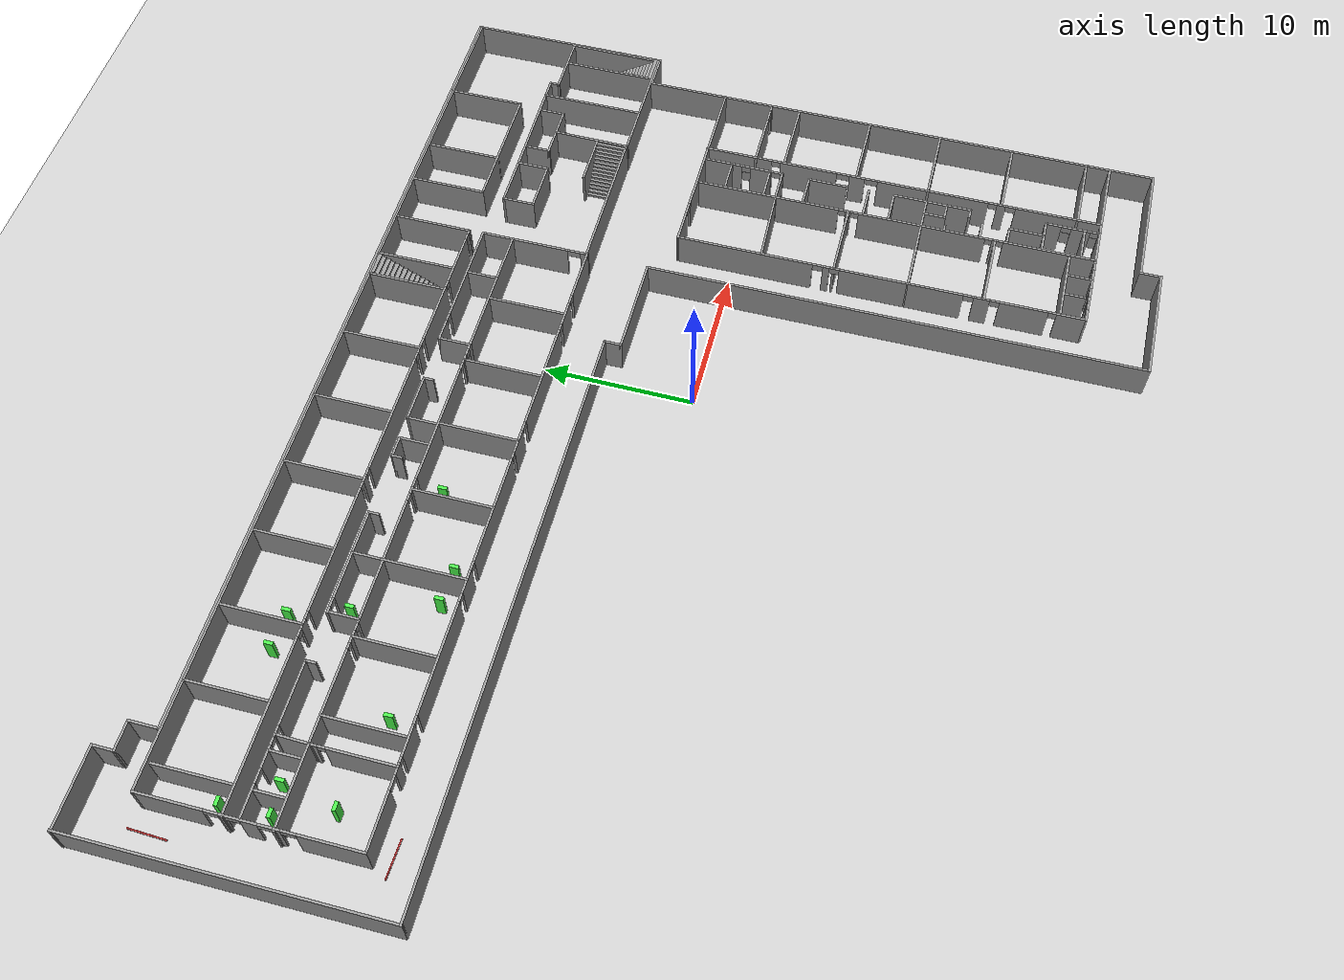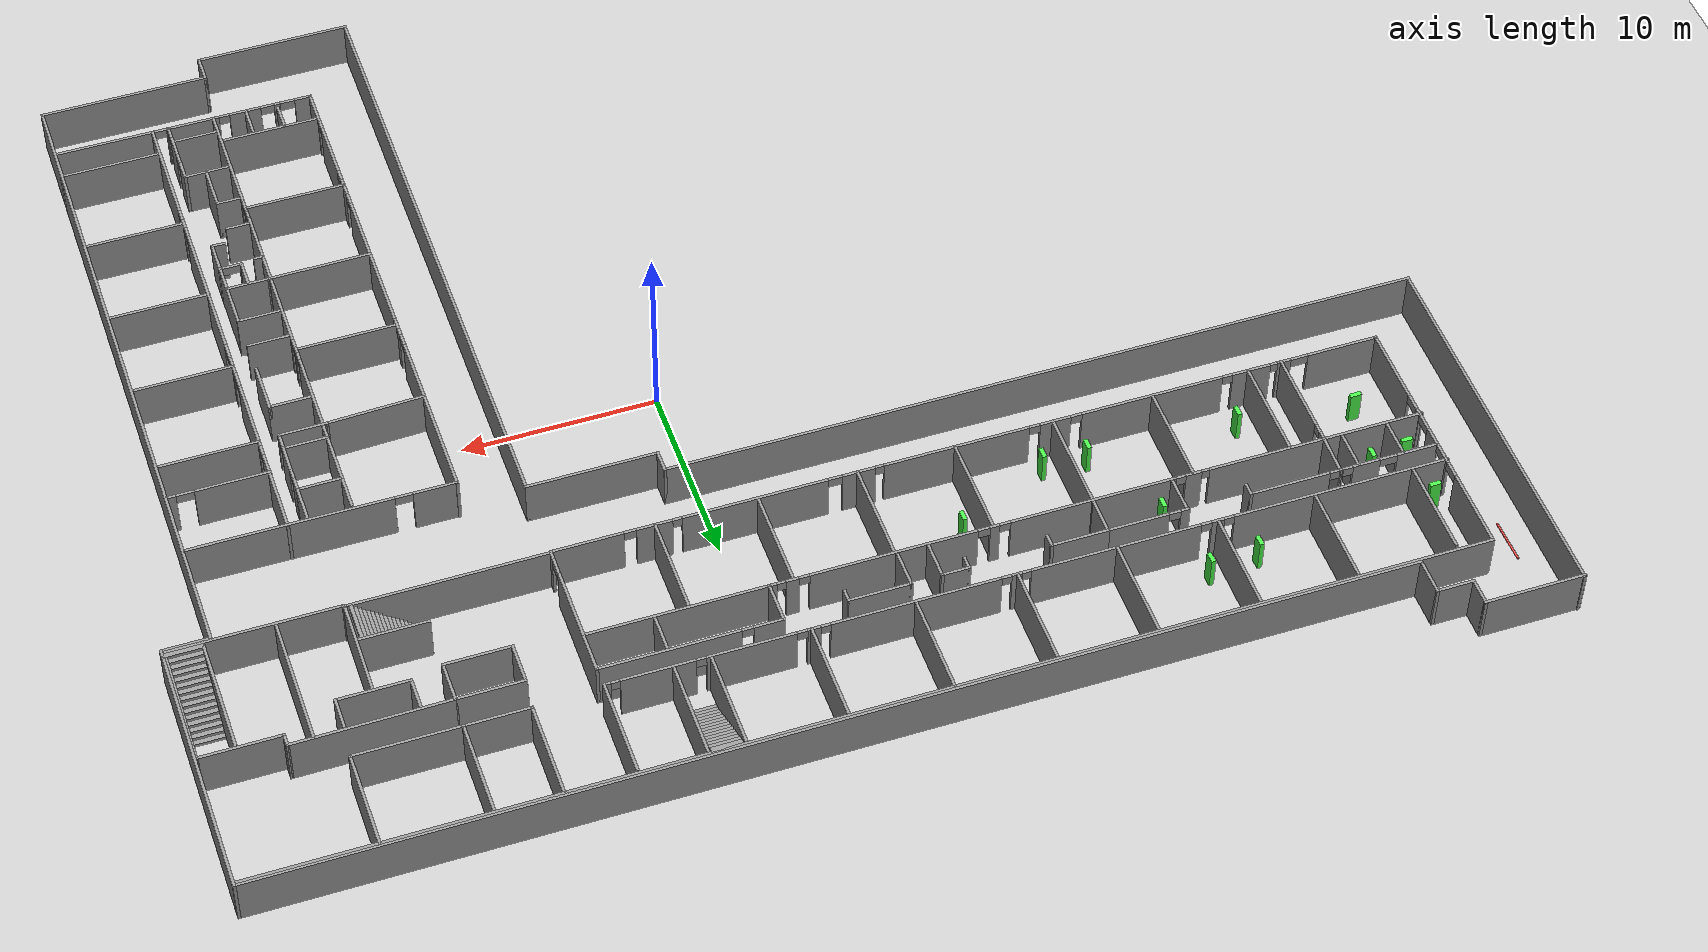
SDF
<sdf version="1.6">
 <world name="default">
  <light name="sun" type="directional">
   <pose>0 0 10 0 -0 0</pose>
   <diffuse>0.8 0.8 0.8 1</diffuse>
   <specular>0.2 0.2 0.2 1</specular>
   <attenuation>
    <range>1000</range>
    <constant>0.9</constant>
    <linear>0.01</linear>
    <quadratic>0.001</quadratic>
   </attenuation>
   <direction>-0.5 0.1 -0.9</direction>
  </light>
  <model name="ground_plane">
   <static>1</static>
   <link name="link">
    <collision name="collision">
     <geometry><plane><normal>0 0 1</normal><size>100 100</size></plane></geometry>
     <surface><friction><ode><mu>100</mu><mu2>50</mu2></ode></friction></surface>
    </collision>
    <visual name="visual">
     <cast_shadows>0</cast_shadows>
     <geometry><plane><normal>0 0 1</normal><size>100 100</size></plane></geometry>
     <material>
      <script><uri>file://media/materials/scripts/gazebo.material</uri><name>Gazebo/Grey</name></script>
     </material>
    </visual>
   </link>
  </model>
  <gravity>0 0 -9.8</gravity>
  <magnetic_field>6e-06 2.3e-05 -4.2e-05</magnetic_field>
  <atmosphere type="adiabatic"/>
  <physics name="default_physics" default="0" type="ode">
   <max_step_size>0.001</max_step_size>
   <real_time_factor>1</real_time_factor>
   <real_time_update_rate>1000</real_time_update_rate>
  </physics>
  <scene><ambient>0.4 0.4 0.4 1</ambient><background>0.7 0.7 0.7 1</background><shadows>1</shadows></scene>
  <spherical_coordinates>
   <surface_model>EARTH_WGS84</surface_model>
   <latitude_deg>0</latitude_deg>
   <longitude_deg>0</longitude_deg>
   <elevation>0</elevation>
   <heading_deg>0</heading_deg>
  </spherical_coordinates>
  <model name="se1floor1">
   <pose>-5.19256 -0.852459 0 0 -0 0</pose>
   <link name="Stairs_0">
    <visual name="Stairs_0_Visual_0">
     <pose>31.172 14.058 0.083333 0 -0 0</pose>
     <geometry><box><size>1.96304 0.254734 0.166667</size></box></geometry>
     <material>
      <script><uri>file://media/materials/scripts/gazebo.material</uri><name>Gazebo/Grey</name></script>
      <ambient>1 1 1 1</ambient>
     </material>
     <meta><layer>0</layer></meta>
    </visual>
    <collision name="Stairs_0_Collision_0">
     <geometry><box><size>1.96304 0.254734 0.166667</size></box></geometry>
     <pose>31.172 14.058 0.083333 0 -0 0</pose>
    </collision>
    <visual name="Stairs_0_Visual_1">
     <pose>31.172 13.8033 0.25 0 -0 0</pose>
     <geometry><box><size>1.96304 0.254734 0.166667</size></box></geometry>
     <material>
      <script><uri>file://media/materials/scripts/gazebo.material</uri><name>Gazebo/Grey</name></script>
      <ambient>1 1 1 1</ambient>
     </material>
     <meta><layer>0</layer></meta>
    </visual>
    <collision name="Stairs_0_Collision_1">
     <geometry><box><size>1.96304 0.254734 0.166667</size></box></geometry>
     <pose>31.172 13.8033 0.25 0 -0 0</pose>
    </collision>
    <visual name="Stairs_0_Visual_2">
     <pose>31.172 13.5485 0.416667 0 -0 0</pose>
     <geometry><box><size>1.96304 0.254734 0.166667</size></box></geometry>
     <material>
      <script><uri>file://media/materials/scripts/gazebo.material</uri><name>Gazebo/Grey</name></script>
      <ambient>1 1 1 1</ambient>
     </material>
     <meta><layer>0</layer></meta>
    </visual>
    <collision name="Stairs_0_Collision_2">
     <geometry><box><size>1.96304 0.254734 0.166667</size></box></geometry>
     <pose>31.172 13.5485 0.416667 0 -0 0</pose>
    </collision>
    <visual name="Stairs_0_Visual_3">
     <pose>31.172 13.2938 0.583333 0 -0 0</pose>
     <geometry><box><size>1.96304 0.254734 0.166667</size></box></geometry>
     <material>
      <script><uri>file://media/materials/scripts/gazebo.material</uri><name>Gazebo/Grey</name></script>
      <ambient>1 1 1 1</ambient>
     </material>
     <meta><layer>0</layer></meta>
    </visual>
    <collision name="Stairs_0_Collision_3">
     <geometry><box><size>1.96304 0.254734 0.166667</size></box></geometry>
     <pose>31.172 13.2938 0.583333 0 -0 0</pose>
    </collision>
    <visual name="Stairs_0_Visual_4">
     <pose>31.172 13.0391 0.75 0 -0 0</pose>
     <geometry><box><size>1.96304 0.254734 0.166667</size></box></geometry>
     <material>
      <script><uri>file://media/materials/scripts/gazebo.material</uri><name>Gazebo/Grey</name></script>
      <ambient>1 1 1 1</ambient>
     </material>
     <meta><layer>0</layer></meta>
    </visual>
    <collision name="Stairs_0_Collision_4">
     <geometry><box><size>1.96304 0.254734 0.166667</size></box></geometry>
     <pose>31.172 13.0391 0.75 0 -0 0</pose>
    </collision>
    <visual name="Stairs_0_Visual_5">
     <pose>31.172 12.7843 0.916667 0 -0 0</pose>
     <geometry><box><size>1.96304 0.254734 0.166667</size></box></geometry>
     <material>
      <script><uri>file://media/materials/scripts/gazebo.material</uri><name>Gazebo/Grey</name></script>
      <ambient>1 1 1 1</ambient>
     </material>
     <meta><layer>0</layer></meta>
    </visual>
    <collision name="Stairs_0_Collision_5">
     <geometry><box><size>1.96304 0.254734 0.166667</size></box></geometry>
     <pose>31.172 12.7843 0.916667 0 -0 0</pose>
    </collision>
    <visual name="Stairs_0_Visual_6">
     <pose>31.172 12.5296 1.08333 0 -0 0</pose>
     <geometry><box><size>1.96304 0.254734 0.166667</size></box></geometry>
     <material>
      <script><uri>file://media/materials/scripts/gazebo.material</uri><name>Gazebo/Grey</name></script>
      <ambient>1 1 1 1</ambient>
     </material>
     <meta><layer>0</layer></meta>
    </visual>
    <collision name="Stairs_0_Collision_6">
     <geometry><box><size>1.96304 0.254734 0.166667</size></box></geometry>
     <pose>31.172 12.5296 1.08333 0 -0 0</pose>
    </collision>
    <visual name="Stairs_0_Visual_7">
     <pose>31.172 12.2749 1.25 0 -0 0</pose>
     <geometry><box><size>1.96304 0.254734 0.166667</size></box></geometry>
     <material>
      <script><uri>file://media/materials/scripts/gazebo.material</uri><name>Gazebo/Grey</name></script>
      <ambient>1 1 1 1</ambient>
     </material>
     <meta><layer>0</layer></meta>
    </visual>
    <collision name="Stairs_0_Collision_7">
     <geometry><box><size>1.96304 0.254734 0.166667</size></box></geometry>
     <pose>31.172 12.2749 1.25 0 -0 0</pose>
    </collision>
    <visual name="Stairs_0_Visual_8">
     <pose>31.172 12.0201 1.41667 0 -0 0</pose>
     <geometry><box><size>1.96304 0.254734 0.166667</size></box></geometry>
     <material>
      <script><uri>file://media/materials/scripts/gazebo.material</uri><name>Gazebo/Grey</name></script>
      <ambient>1 1 1 1</ambient>
     </material>
     <meta><layer>0</layer></meta>
    </visual>
    <collision name="Stairs_0_Collision_8">
     <geometry><box><size>1.96304 0.254734 0.166667</size></box></geometry>
     <pose>31.172 12.0201 1.41667 0 -0 0</pose>
    </collision>
    <visual name="Stairs_0_Visual_9">
     <pose>31.172 11.7654 1.58333 0 -0 0</pose>
     <geometry><box><size>1.96304 0.254734 0.166667</size></box></geometry>
     <material>
      <script><uri>file://media/materials/scripts/gazebo.material</uri><name>Gazebo/Grey</name></script>
      <ambient>1 1 1 1</ambient>
     </material>
     <meta><layer>0</layer></meta>
    </visual>
    <collision name="Stairs_0_Collision_9">
     <geometry><box><size>1.96304 0.254734 0.166667</size></box></geometry>
     <pose>31.172 11.7654 1.58333 0 -0 0</pose>
    </collision>
    <visual name="Stairs_0_Visual_10">
     <pose>31.172 11.5107 1.75 0 -0 0</pose>
     <geometry><box><size>1.96304 0.254734 0.166667</size></box></geometry>
     <material>
      <script><uri>file://media/materials/scripts/gazebo.material</uri><name>Gazebo/Grey</name></script>
      <ambient>1 1 1 1</ambient>
     </material>
     <meta><layer>0</layer></meta>
    </visual>
    <collision name="Stairs_0_Collision_10">
     <geometry><box><size>1.96304 0.254734 0.166667</size></box></geometry>
     <pose>31.172 11.5107 1.75 0 -0 0</pose>
    </collision>
    <visual name="Stairs_0_Visual_11">
     <pose>31.172 11.2559 1.91667 0 -0 0</pose>
     <geometry><box><size>1.96304 0.254734 0.166667</size></box></geometry>
     <material>
      <script><uri>file://media/materials/scripts/gazebo.material</uri><name>Gazebo/Grey</name></script>
      <ambient>1 1 1 1</ambient>
     </material>
     <meta><layer>0</layer></meta>
    </visual>
    <collision name="Stairs_0_Collision_11">
     <geometry><box><size>1.96304 0.254734 0.166667</size></box></geometry>
     <pose>31.172 11.2559 1.91667 0 -0 0</pose>
    </collision>
    <visual name="Stairs_0_Visual_12">
     <pose>31.172 11.0012 2.08333 0 -0 0</pose>
     <geometry><box><size>1.96304 0.254734 0.166667</size></box></geometry>
     <material>
      <script><uri>file://media/materials/scripts/gazebo.material</uri><name>Gazebo/Grey</name></script>
      <ambient>1 1 1 1</ambient>
     </material>
     <meta><layer>0</layer></meta>
    </visual>
    <collision name="Stairs_0_Collision_12">
     <geometry><box><size>1.96304 0.254734 0.166667</size></box></geometry>
     <pose>31.172 11.0012 2.08333 0 -0 0</pose>
    </collision>
    <visual name="Stairs_0_Visual_13">
     <pose>31.172 10.7465 2.25 0 -0 0</pose>
     <geometry><box><size>1.96304 0.254734 0.166667</size></box></geometry>
     <material>
      <script><uri>file://media/materials/scripts/gazebo.material</uri><name>Gazebo/Grey</name></script>
      <ambient>1 1 1 1</ambient>
     </material>
     <meta><layer>0</layer></meta>
    </visual>
    <collision name="Stairs_0_Collision_13">
     <geometry><box><size>1.96304 0.254734 0.166667</size></box></geometry>
     <pose>31.172 10.7465 2.25 0 -0 0</pose>
    </collision>
    <visual name="Stairs_0_Visual_14">
     <pose>31.172 10.4917 2.41667 0 -0 0</pose>
     <geometry><box><size>1.96304 0.254734 0.166667</size></box></geometry>
     <material>
      <script><uri>file://media/materials/scripts/gazebo.material</uri><name>Gazebo/Grey</name></script>
      <ambient>1 1 1 1</ambient>
     </material>
     <meta><layer>0</layer></meta>
    </visual>
    <collision name="Stairs_0_Collision_14">
     <geometry><box><size>1.96304 0.254734 0.166667</size></box></geometry>
     <pose>31.172 10.4917 2.41667 0 -0 0</pose>
    </collision>
   </link>
   <link name="Stairs_1">
    <visual name="Stairs_1_Visual_0">
     <pose>9.09407 19.8083 0.083333 0 -0 -3.14159</pose>
     <geometry><box><size>1.5586 0.281214 0.166667</size></box></geometry>
     <material>
      <script><uri>file://media/materials/scripts/gazebo.material</uri><name>Gazebo/Grey</name></script>
      <ambient>1 1 1 1</ambient>
     </material>
     <meta><layer>0</layer></meta>
    </visual>
    <collision name="Stairs_1_Collision_0">
     <geometry><box><size>1.5586 0.281214 0.166667</size></box></geometry>
     <pose>9.09407 19.8083 0.083333 0 -0 -3.14159</pose>
    </collision>
    <visual name="Stairs_1_Visual_1">
     <pose>9.09407 20.0895 0.25 0 -0 -3.14159</pose>
     <geometry><box><size>1.5586 0.281214 0.166667</size></box></geometry>
     <material>
      <script><uri>file://media/materials/scripts/gazebo.material</uri><name>Gazebo/Grey</name></script>
      <ambient>1 1 1 1</ambient>
     </material>
     <meta><layer>0</layer></meta>
    </visual>
    <collision name="Stairs_1_Collision_1">
     <geometry><box><size>1.5586 0.281214 0.166667</size></box></geometry>
     <pose>9.09407 20.0895 0.25 0 -0 -3.14159</pose>
    </collision>
    <visual name="Stairs_1_Visual_2">
     <pose>9.09407 20.3707 0.416667 0 -0 -3.14159</pose>
     <geometry><box><size>1.5586 0.281214 0.166667</size></box></geometry>
     <material>
      <script><uri>file://media/materials/scripts/gazebo.material</uri><name>Gazebo/Grey</name></script>
      <ambient>1 1 1 1</ambient>
     </material>
     <meta><layer>0</layer></meta>
    </visual>
    <collision name="Stairs_1_Collision_2">
     <geometry><box><size>1.5586 0.281214 0.166667</size></box></geometry>
     <pose>9.09407 20.3707 0.416667 0 -0 -3.14159</pose>
    </collision>
    <visual name="Stairs_1_Visual_3">
     <pose>9.09407 20.6519 0.583333 0 -0 -3.14159</pose>
     <geometry><box><size>1.5586 0.281214 0.166667</size></box></geometry>
     <material>
      <script><uri>file://media/materials/scripts/gazebo.material</uri><name>Gazebo/Grey</name></script>
      <ambient>1 1 1 1</ambient>
     </material>
     <meta><layer>0</layer></meta>
    </visual>
    <collision name="Stairs_1_Collision_3">
     <geometry><box><size>1.5586 0.281214 0.166667</size></box></geometry>
     <pose>9.09407 20.6519 0.583333 0 -0 -3.14159</pose>
    </collision>
    <visual name="Stairs_1_Visual_4">
     <pose>9.09407 20.9331 0.75 0 -0 -3.14159</pose>
     <geometry><box><size>1.5586 0.281214 0.166667</size></box></geometry>
     <material>
      <script><uri>file://media/materials/scripts/gazebo.material</uri><name>Gazebo/Grey</name></script>
      <ambient>1 1 1 1</ambient>
     </material>
     <meta><layer>0</layer></meta>
    </visual>
    <collision name="Stairs_1_Collision_4">
     <geometry><box><size>1.5586 0.281214 0.166667</size></box></geometry>
     <pose>9.09407 20.9331 0.75 0 -0 -3.14159</pose>
    </collision>
    <visual name="Stairs_1_Visual_5">
     <pose>9.09407 21.2144 0.916667 0 -0 -3.14159</pose>
     <geometry><box><size>1.5586 0.281214 0.166667</size></box></geometry>
     <material>
      <script><uri>file://media/materials/scripts/gazebo.material</uri><name>Gazebo/Grey</name></script>
      <ambient>1 1 1 1</ambient>
     </material>
     <meta><layer>0</layer></meta>
    </visual>
    <collision name="Stairs_1_Collision_5">
     <geometry><box><size>1.5586 0.281214 0.166667</size></box></geometry>
     <pose>9.09407 21.2144 0.916667 0 -0 -3.14159</pose>
    </collision>
    <visual name="Stairs_1_Visual_6">
     <pose>9.09407 21.4956 1.08333 0 -0 -3.14159</pose>
     <geometry><box><size>1.5586 0.281214 0.166667</size></box></geometry>
     <material>
      <script><uri>file://media/materials/scripts/gazebo.material</uri><name>Gazebo/Grey</name></script>
      <ambient>1 1 1 1</ambient>
     </material>
     <meta><layer>0</layer></meta>
    </visual>
    <collision name="Stairs_1_Collision_6">
     <geometry><box><size>1.5586 0.281214 0.166667</size></box></geometry>
     <pose>9.09407 21.4956 1.08333 0 -0 -3.14159</pose>
    </collision>
    <visual name="Stairs_1_Visual_7">
     <pose>9.09407 21.7768 1.25 0 -0 -3.14159</pose>
     <geometry><box><size>1.5586 0.281214 0.166667</size></box></geometry>
     <material>
      <script><uri>file://media/materials/scripts/gazebo.material</uri><name>Gazebo/Grey</name></script>
      <ambient>1 1 1 1</ambient>
     </material>
     <meta><layer>0</layer></meta>
    </visual>
    <collision name="Stairs_1_Collision_7">
     <geometry><box><size>1.5586 0.281214 0.166667</size></box></geometry>
     <pose>9.09407 21.7768 1.25 0 -0 -3.14159</pose>
    </collision>
    <visual name="Stairs_1_Visual_8">
     <pose>9.09407 22.058 1.41667 0 -0 -3.14159</pose>
     <geometry><box><size>1.5586 0.281214 0.166667</size></box></geometry>
     <material>
      <script><uri>file://media/materials/scripts/gazebo.material</uri><name>Gazebo/Grey</name></script>
      <ambient>1 1 1 1</ambient>
     </material>
     <meta><layer>0</layer></meta>
    </visual>
    <collision name="Stairs_1_Collision_8">
     <geometry><box><size>1.5586 0.281214 0.166667</size></box></geometry>
     <pose>9.09407 22.058 1.41667 0 -0 -3.14159</pose>
    </collision>
    <visual name="Stairs_1_Visual_9">
     <pose>9.09407 22.3392 1.58333 0 -0 -3.14159</pose>
     <geometry><box><size>1.5586 0.281214 0.166667</size></box></geometry>
     <material>
      <script><uri>file://media/materials/scripts/gazebo.material</uri><name>Gazebo/Grey</name></script>
      <ambient>1 1 1 1</ambient>
     </material>
     <meta><layer>0</layer></meta>
    </visual>
    <collision name="Stairs_1_Collision_9">
     <geometry><box><size>1.5586 0.281214 0.166667</size></box></geometry>
     <pose>9.09407 22.3392 1.58333 0 -0 -3.14159</pose>
    </collision>
    <visual name="Stairs_1_Visual_10">
     <pose>9.09407 22.6204 1.75 0 -0 -3.14159</pose>
     <geometry><box><size>1.5586 0.281214 0.166667</size></box></geometry>
     <material>
      <script><uri>file://media/materials/scripts/gazebo.material</uri><name>Gazebo/Grey</name></script>
      <ambient>1 1 1 1</ambient>
     </material>
     <meta><layer>0</layer></meta>
    </visual>
    <collision name="Stairs_1_Collision_10">
     <geometry><box><size>1.5586 0.281214 0.166667</size></box></geometry>
     <pose>9.09407 22.6204 1.75 0 -0 -3.14159</pose>
    </collision>
    <visual name="Stairs_1_Visual_11">
     <pose>9.09407 22.9016 1.91667 0 -0 -3.14159</pose>
     <geometry><box><size>1.5586 0.281214 0.166667</size></box></geometry>
     <material>
      <script><uri>file://media/materials/scripts/gazebo.material</uri><name>Gazebo/Grey</name></script>
      <ambient>1 1 1 1</ambient>
     </material>
     <meta><layer>0</layer></meta>
    </visual>
    <collision name="Stairs_1_Collision_11">
     <geometry><box><size>1.5586 0.281214 0.166667</size></box></geometry>
     <pose>9.09407 22.9016 1.91667 0 -0 -3.14159</pose>
    </collision>
    <visual name="Stairs_1_Visual_12">
     <pose>9.09407 23.1829 2.08333 0 -0 -3.14159</pose>
     <geometry><box><size>1.5586 0.281214 0.166667</size></box></geometry>
     <material>
      <script><uri>file://media/materials/scripts/gazebo.material</uri><name>Gazebo/Grey</name></script>
      <ambient>1 1 1 1</ambient>
     </material>
     <meta><layer>0</layer></meta>
    </visual>
    <collision name="Stairs_1_Collision_12">
     <geometry><box><size>1.5586 0.281214 0.166667</size></box></geometry>
     <pose>9.09407 23.1829 2.08333 0 -0 -3.14159</pose>
    </collision>
    <visual name="Stairs_1_Visual_13">
     <pose>9.09407 23.4641 2.25 0 -0 -3.14159</pose>
     <geometry><box><size>1.5586 0.281214 0.166667</size></box></geometry>
     <material>
      <script><uri>file://media/materials/scripts/gazebo.material</uri><name>Gazebo/Grey</name></script>
      <ambient>1 1 1 1</ambient>
     </material>
     <meta><layer>0</layer></meta>
    </visual>
    <collision name="Stairs_1_Collision_13">
     <geometry><box><size>1.5586 0.281214 0.166667</size></box></geometry>
     <pose>9.09407 23.4641 2.25 0 -0 -3.14159</pose>
    </collision>
    <visual name="Stairs_1_Visual_14">
     <pose>9.09407 23.7453 2.41667 0 -0 -3.14159</pose>
     <geometry><box><size>1.5586 0.281214 0.166667</size></box></geometry>
     <material>
      <script><uri>file://media/materials/scripts/gazebo.material</uri><name>Gazebo/Grey</name></script>
      <ambient>1 1 1 1</ambient>
     </material>
     <meta><layer>0</layer></meta>
    </visual>
    <collision name="Stairs_1_Collision_14">
     <geometry><box><size>1.5586 0.281214 0.166667</size></box></geometry>
     <pose>9.09407 23.7453 2.41667 0 -0 -3.14159</pose>
    </collision>
   </link>
   <link name="Stairs_2">
    <visual name="Stairs_2_Visual_0">
     <pose>20.4775 11.3856 0.083333 0 -0 1.5708</pose>
     <geometry><box><size>2.01727 0.190773 0.166667</size></box></geometry>
     <material>
      <script><uri>file://media/materials/scripts/gazebo.material</uri><name>Gazebo/Grey</name></script>
      <ambient>1 1 1 1</ambient>
     </material>
     <meta><layer>0</layer></meta>
    </visual>
    <collision name="Stairs_2_Collision_0">
     <geometry><box><size>2.01727 0.190773 0.166667</size></box></geometry>
     <pose>20.4775 11.3856 0.083333 0 -0 1.5708</pose>
    </collision>
    <visual name="Stairs_2_Visual_1">
     <pose>20.6683 11.3856 0.25 0 -0 1.5708</pose>
     <geometry><box><size>2.01727 0.190773 0.166667</size></box></geometry>
     <material>
      <script><uri>file://media/materials/scripts/gazebo.material</uri><name>Gazebo/Grey</name></script>
      <ambient>1 1 1 1</ambient>
     </material>
     <meta><layer>0</layer></meta>
    </visual>
    <collision name="Stairs_2_Collision_1">
     <geometry><box><size>2.01727 0.190773 0.166667</size></box></geometry>
     <pose>20.6683 11.3856 0.25 0 -0 1.5708</pose>
    </collision>
    <visual name="Stairs_2_Visual_2">
     <pose>20.8591 11.3856 0.416667 0 -0 1.5708</pose>
     <geometry><box><size>2.01727 0.190773 0.166667</size></box></geometry>
     <material>
      <script><uri>file://media/materials/scripts/gazebo.material</uri><name>Gazebo/Grey</name></script>
      <ambient>1 1 1 1</ambient>
     </material>
     <meta><layer>0</layer></meta>
    </visual>
    <collision name="Stairs_2_Collision_2">
     <geometry><box><size>2.01727 0.190773 0.166667</size></box></geometry>
     <pose>20.8591 11.3856 0.416667 0 -0 1.5708</pose>
    </collision>
    <visual name="Stairs_2_Visual_3">
     <pose>21.0498 11.3856 0.583333 0 -0 1.5708</pose>
     <geometry><box><size>2.01727 0.190773 0.166667</size></box></geometry>
     <material>
      <script><uri>file://media/materials/scripts/gazebo.material</uri><name>Gazebo/Grey</name></script>
      <ambient>1 1 1 1</ambient>
     </material>
     <meta><layer>0</layer></meta>
    </visual>
    <collision name="Stairs_2_Collision_3">
     <geometry><box><size>2.01727 0.190773 0.166667</size></box></geometry>
     <pose>21.0498 11.3856 0.583333 0 -0 1.5708</pose>
    </collision>
    <visual name="Stairs_2_Visual_4">
     <pose>21.2406 11.3856 0.75 0 -0 1.5708</pose>
     <geometry><box><size>2.01727 0.190773 0.166667</size></box></geometry>
     <material>
      <script><uri>file://media/materials/scripts/gazebo.material</uri><name>Gazebo/Grey</name></script>
      <ambient>1 1 1 1</ambient>
     </material>
     <meta><layer>0</layer></meta>
    </visual>
    <collision name="Stairs_2_Collision_4">
     <geometry><box><size>2.01727 0.190773 0.166667</size></box></geometry>
     <pose>21.2406 11.3856 0.75 0 -0 1.5708</pose>
    </collision>
    <visual name="Stairs_2_Visual_5">
     <pose>21.4314 11.3856 0.916667 0 -0 1.5708</pose>
     <geometry><box><size>2.01727 0.190773 0.166667</size></box></geometry>
     <material>
      <script><uri>file://media/materials/scripts/gazebo.material</uri><name>Gazebo/Grey</name></script>
      <ambient>1 1 1 1</ambient>
     </material>
     <meta><layer>0</layer></meta>
    </visual>
    <collision name="Stairs_2_Collision_5">
     <geometry><box><size>2.01727 0.190773 0.166667</size></box></geometry>
     <pose>21.4314 11.3856 0.916667 0 -0 1.5708</pose>
    </collision>
    <visual name="Stairs_2_Visual_6">
     <pose>21.6222 11.3856 1.08333 0 -0 1.5708</pose>
     <geometry><box><size>2.01727 0.190773 0.166667</size></box></geometry>
     <material>
      <script><uri>file://media/materials/scripts/gazebo.material</uri><name>Gazebo/Grey</name></script>
      <ambient>1 1 1 1</ambient>
     </material>
     <meta><layer>0</layer></meta>
    </visual>
    <collision name="Stairs_2_Collision_6">
     <geometry><box><size>2.01727 0.190773 0.166667</size></box></geometry>
     <pose>21.6222 11.3856 1.08333 0 -0 1.5708</pose>
    </collision>
    <visual name="Stairs_2_Visual_7">
     <pose>21.8129 11.3856 1.25 0 -0 1.5708</pose>
     <geometry><box><size>2.01727 0.190773 0.166667</size></box></geometry>
     <material>
      <script><uri>file://media/materials/scripts/gazebo.material</uri><name>Gazebo/Grey</name></script>
      <ambient>1 1 1 1</ambient>
     </material>
     <meta><layer>0</layer></meta>
    </visual>
    <collision name="Stairs_2_Collision_7">
     <geometry><box><size>2.01727 0.190773 0.166667</size></box></geometry>
     <pose>21.8129 11.3856 1.25 0 -0 1.5708</pose>
    </collision>
    <visual name="Stairs_2_Visual_8">
     <pose>22.0037 11.3856 1.41667 0 -0 1.5708</pose>
     <geometry><box><size>2.01727 0.190773 0.166667</size></box></geometry>
     <material>
      <script><uri>file://media/materials/scripts/gazebo.material</uri><name>Gazebo/Grey</name></script>
      <ambient>1 1 1 1</ambient>
     </material>
     <meta><layer>0</layer></meta>
    </visual>
    <collision name="Stairs_2_Collision_8">
     <geometry><box><size>2.01727 0.190773 0.166667</size></box></geometry>
     <pose>22.0037 11.3856 1.41667 0 -0 1.5708</pose>
    </collision>
    <visual name="Stairs_2_Visual_9">
     <pose>22.1945 11.3856 1.58333 0 -0 1.5708</pose>
     <geometry><box><size>2.01727 0.190773 0.166667</size></box></geometry>
     <material>
      <script><uri>file://media/materials/scripts/gazebo.material</uri><name>Gazebo/Grey</name></script>
      <ambient>1 1 1 1</ambient>
     </material>
     <meta><layer>0</layer></meta>
    </visual>
    <collision name="Stairs_2_Collision_9">
     <geometry><box><size>2.01727 0.190773 0.166667</size></box></geometry>
     <pose>22.1945 11.3856 1.58333 0 -0 1.5708</pose>
    </collision>
    <visual name="Stairs_2_Visual_10">
     <pose>22.3853 11.3856 1.75 0 -0 1.5708</pose>
     <geometry><box><size>2.01727 0.190773 0.166667</size></box></geometry>
     <material>
      <script><uri>file://media/materials/scripts/gazebo.material</uri><name>Gazebo/Grey</name></script>
      <ambient>1 1 1 1</ambient>
     </material>
     <meta><layer>0</layer></meta>
    </visual>
    <collision name="Stairs_2_Collision_10">
     <geometry><box><size>2.01727 0.190773 0.166667</size></box></geometry>
     <pose>22.3853 11.3856 1.75 0 -0 1.5708</pose>
    </collision>
    <visual name="Stairs_2_Visual_11">
     <pose>22.576 11.3856 1.91667 0 -0 1.5708</pose>
     <geometry><box><size>2.01727 0.190773 0.166667</size></box></geometry>
     <material>
      <script><uri>file://media/materials/scripts/gazebo.material</uri><name>Gazebo/Grey</name></script>
      <ambient>1 1 1 1</ambient>
     </material>
     <meta><layer>0</layer></meta>
    </visual>
    <collision name="Stairs_2_Collision_11">
     <geometry><box><size>2.01727 0.190773 0.166667</size></box></geometry>
     <pose>22.576 11.3856 1.91667 0 -0 1.5708</pose>
    </collision>
    <visual name="Stairs_2_Visual_12">
     <pose>22.7668 11.3856 2.08333 0 -0 1.5708</pose>
     <geometry><box><size>2.01727 0.190773 0.166667</size></box></geometry>
     <material>
      <script><uri>file://media/materials/scripts/gazebo.material</uri><name>Gazebo/Grey</name></script>
      <ambient>1 1 1 1</ambient>
     </material>
     <meta><layer>0</layer></meta>
    </visual>
    <collision name="Stairs_2_Collision_12">
     <geometry><box><size>2.01727 0.190773 0.166667</size></box></geometry>
     <pose>22.7668 11.3856 2.08333 0 -0 1.5708</pose>
    </collision>
    <visual name="Stairs_2_Visual_13">
     <pose>22.9576 11.3856 2.25 0 -0 1.5708</pose>
     <geometry><box><size>2.01727 0.190773 0.166667</size></box></geometry>
     <material>
      <script><uri>file://media/materials/scripts/gazebo.material</uri><name>Gazebo/Grey</name></script>
      <ambient>1 1 1 1</ambient>
     </material>
     <meta><layer>0</layer></meta>
    </visual>
    <collision name="Stairs_2_Collision_13">
     <geometry><box><size>2.01727 0.190773 0.166667</size></box></geometry>
     <pose>22.9576 11.3856 2.25 0 -0 1.5708</pose>
    </collision>
    <visual name="Stairs_2_Visual_14">
     <pose>23.1484 11.3856 2.41667 0 -0 1.5708</pose>
     <geometry><box><size>2.01727 0.190773 0.166667</size></box></geometry>
     <material>
      <script><uri>file://media/materials/scripts/gazebo.material</uri><name>Gazebo/Grey</name></script>
      <ambient>1 1 1 1</ambient>
     </material>
     <meta><layer>0</layer></meta>
    </visual>
    <collision name="Stairs_2_Collision_14">
     <geometry><box><size>2.01727 0.190773 0.166667</size></box></geometry>
     <pose>23.1484 11.3856 2.41667 0 -0 1.5708</pose>
    </collision>
   </link>
   <link name="Wall_0">
    <collision name="Wall_0_Collision">
     <geometry><box><size>20.25 0.15 2.5</size></box></geometry>
     <pose>0 0 1.25 0 -0 0</pose>
    </collision>
    <visual name="Wall_0_Visual">
     <pose>0 0 1.25 0 -0 0</pose>
     <geometry><box><size>20.25 0.15 2.5</size></box></geometry>
     <material>
      <script><uri>file://media/materials/scripts/gazebo.material</uri><name>Gazebo/Grey</name></script>
      <ambient>1 1 1 1</ambient>
     </material>
     <meta><layer>0</layer></meta>
    </visual>
    <pose>-32.1 17.225 0 0 0 -1.5708</pose>
   </link>
   <link name="Wall_1">
    <collision name="Wall_1_Collision">
     <geometry><box><size>39 0.15 2.5</size></box></geometry>
     <pose>0 0 1.25 0 -0 0</pose>
    </collision>
    <visual name="Wall_1_Visual">
     <pose>0 0 1.25 0 -0 0</pose>
     <geometry><box><size>39 0.15 2.5</size></box></geometry>
     <material>
      <script><uri>file://media/materials/scripts/gazebo.material</uri><name>Gazebo/Grey</name></script>
      <ambient>1 1 1 1</ambient>
     </material>
     <meta><layer>0</layer></meta>
    </visual>
    <pose>-12.675 7.175 0 0 -0 0</pose>
   </link>
   <link name="Wall_10">
    <collision name="Wall_10_Collision">
     <geometry><box><size>2.5 0.15 2.5</size></box></geometry>
     <pose>0 0 1.25 0 -0 0</pose>
    </collision>
    <visual name="Wall_10_Visual">
     <pose>0 0 1.25 0 -0 0</pose>
     <geometry><box><size>2.5 0.15 2.5</size></box></geometry>
     <material>
      <script><uri>file://media/materials/scripts/gazebo.material</uri><name>Gazebo/Grey</name></script>
      <ambient>1 1 1 1</ambient>
     </material>
     <meta><layer>0</layer></meta>
    </visual>
    <pose>30.975 10.175 0 0 -0 0</pose>
   </link>
   <link name="Wall_100">
    <collision name="Wall_100_Collision">
     <geometry><box><size>5.25 0.15 2.5</size></box></geometry>
     <pose>0 0 1.25 0 -0 0</pose>
    </collision>
    <visual name="Wall_100_Visual">
     <pose>0 0 1.25 0 -0 0</pose>
     <geometry><box><size>5.25 0.15 2.5</size></box></geometry>
     <material>
      <script><uri>file://media/materials/scripts/gazebo.material</uri><name>Gazebo/Grey</name></script>
      <ambient>1 1 1 1</ambient>
     </material>
     <meta><layer>0</layer></meta>
    </visual>
    <pose>25.4403 21.3628 0 0 -0 1.5708</pose>
   </link>
   <link name="Wall_103">
    <collision name="Wall_103_Collision">
     <geometry><box><size>2.25 0.15 2.5</size></box></geometry>
     <pose>0 0 1.25 0 -0 0</pose>
    </collision>
    <visual name="Wall_103_Visual">
     <pose>0 0 1.25 0 -0 0</pose>
     <geometry><box><size>2.25 0.15 2.5</size></box></geometry>
     <material>
      <script><uri>file://media/materials/scripts/gazebo.material</uri><name>Gazebo/Grey</name></script>
      <ambient>1 1 1 1</ambient>
     </material>
     <meta><layer>0</layer></meta>
    </visual>
    <pose>16.6798 16.175 0 0 0 -1.5708</pose>
   </link>
   <link name="Wall_104">
    <collision name="Wall_104_Collision">
     <geometry><box><size>3.5 0.15 2.5</size></box></geometry>
     <pose>0 0 1.25 0 -0 0</pose>
    </collision>
    <visual name="Wall_104_Visual">
     <pose>0 0 1.25 0 -0 0</pose>
     <geometry><box><size>3.5 0.15 2.5</size></box></geometry>
     <material>
      <script><uri>file://media/materials/scripts/gazebo.material</uri><name>Gazebo/Grey</name></script>
      <ambient>1 1 1 1</ambient>
     </material>
     <meta><layer>0</layer></meta>
    </visual>
    <pose>18.3548 15.125 0 0 -0 0</pose>
   </link>
   <link name="Wall_105">
    <collision name="Wall_105_Collision">
     <geometry><box><size>2.25 0.15 2.5</size></box></geometry>
     <pose>0 0 1.25 0 -0 0</pose>
    </collision>
    <visual name="Wall_105_Visual">
     <pose>0 0 1.25 0 -0 0</pose>
     <geometry><box><size>2.25 0.15 2.5</size></box></geometry>
     <material>
      <script><uri>file://media/materials/scripts/gazebo.material</uri><name>Gazebo/Grey</name></script>
      <ambient>1 1 1 1</ambient>
     </material>
     <meta><layer>0</layer></meta>
    </visual>
    <pose>20.0298 16.175 0 0 -0 1.5708</pose>
   </link>
   <link name="Wall_106">
    <collision name="Wall_106_Collision">
     <geometry><box><size>3.5 0.15 2.5</size></box></geometry>
     <pose>0 0 1.25 0 -0 0</pose>
    </collision>
    <visual name="Wall_106_Visual">
     <pose>0 0 1.25 0 -0 0</pose>
     <geometry><box><size>3.5 0.15 2.5</size></box></geometry>
     <material>
      <script><uri>file://media/materials/scripts/gazebo.material</uri><name>Gazebo/Grey</name></script>
      <ambient>1 1 1 1</ambient>
     </material>
     <meta><layer>0</layer></meta>
    </visual>
    <pose>18.3548 17.225 0 0 -0 3.14159</pose>
   </link>
   <link name="Wall_108">
    <collision name="Wall_108_Collision">
     <geometry><box><size>5.29673 0.15 2.5</size></box></geometry>
     <pose>0 0 1.25 0 -0 0</pose>
    </collision>
    <visual name="Wall_108_Visual">
     <pose>0 0 1.25 0 -0 0</pose>
     <geometry><box><size>5.29673 0.15 2.5</size></box></geometry>
     <material>
      <script><uri>file://media/materials/scripts/gazebo.material</uri><name>Gazebo/Grey</name></script>
      <ambient>1 1 1 1</ambient>
     </material>
     <meta><layer>0</layer></meta>
    </visual>
    <pose>23.4514 12.8687 0 0 0 -1.57984</pose>
   </link>
   <link name="Wall_109">
    <collision name="Wall_109_Collision">
     <geometry><box><size>8.75 0.15 2.5</size></box></geometry>
     <pose>0 0 1.25 0 -0 0</pose>
    </collision>
    <visual name="Wall_109_Visual">
     <pose>0 0 1.25 0 -0 0</pose>
     <geometry><box><size>8.75 0.15 2.5</size></box></geometry>
     <material>
      <script><uri>file://media/materials/scripts/gazebo.material</uri><name>Gazebo/Grey</name></script>
      <ambient>1 1 1 1</ambient>
     </material>
     <meta><layer>0</layer></meta>
    </visual>
    <pose>27.7281 10.2954 0 0 -0 0</pose>
   </link>
   <link name="Wall_11">
    <collision name="Wall_11_Collision">
     <geometry><box><size>14 0.15 2.5</size></box></geometry>
     <pose>0 0 1.25 0 -0 0</pose>
    </collision>
    <visual name="Wall_11_Visual">
     <pose>0 0 1.25 0 -0 0</pose>
     <geometry><box><size>14 0.15 2.5</size></box></geometry>
     <material>
      <script><uri>file://media/materials/scripts/gazebo.material</uri><name>Gazebo/Grey</name></script>
      <ambient>1 1 1 1</ambient>
     </material>
     <meta><layer>0</layer></meta>
    </visual>
    <pose>32.15 17.1 0 0 -0 1.5708</pose>
   </link>
   <link name="Wall_110">
    <collision name="Wall_110_Collision">
     <geometry><box><size>6.54669 0.15 2.5</size></box></geometry>
     <pose>0 0 1.25 0 -0 0</pose>
    </collision>
    <visual name="Wall_110_Visual">
     <pose>0 0 1.25 0 -0 0</pose>
     <geometry><box><size>6.54669 0.15 2.5</size></box></geometry>
     <material>
      <script><uri>file://media/materials/scripts/gazebo.material</uri><name>Gazebo/Grey</name></script>
      <ambient>1 1 1 1</ambient>
     </material>
     <meta><layer>0</layer></meta>
    </visual>
    <pose>32.0514 13.4937 0 0 -0 1.56352</pose>
   </link>
   <link name="Wall_111">
    <collision name="Wall_111_Collision">
     <geometry><box><size>4.25 0.15 2.5</size></box></geometry>
     <pose>0 0 1.25 0 -0 0</pose>
    </collision>
    <visual name="Wall_111_Visual">
     <pose>0 0 1.25 0 -0 0</pose>
     <geometry><box><size>4.25 0.15 2.5</size></box></geometry>
     <material>
      <script><uri>file://media/materials/scripts/gazebo.material</uri><name>Gazebo/Grey</name></script>
      <ambient>1 1 1 1</ambient>
     </material>
     <meta><layer>0</layer></meta>
    </visual>
    <pose>30.0246 16.6919 0 0 -0 3.14159</pose>
   </link>
   <link name="Wall_112">
    <collision name="Wall_112_Collision">
     <geometry><box><size>0.75 0.15 2.5</size></box></geometry>
     <pose>0 0 1.25 0 -0 0</pose>
    </collision>
    <visual name="Wall_112_Visual">
     <pose>0 0 1.25 0 -0 0</pose>
     <geometry><box><size>0.75 0.15 2.5</size></box></geometry>
     <material>
      <script><uri>file://media/materials/scripts/gazebo.material</uri><name>Gazebo/Grey</name></script>
      <ambient>1 1 1 1</ambient>
     </material>
     <meta><layer>0</layer></meta>
    </visual>
    <pose>27.9746 16.9919 0 0 -0 1.5708</pose>
   </link>
   <link name="Wall_114">
    <collision name="Wall_114_Collision">
     <geometry><box><size>8.0951 0.15 2.5</size></box></geometry>
     <pose>0 0 1.25 0 -0 0</pose>
    </collision>
    <visual name="Wall_114_Visual">
     <pose>0 0 1.25 0 -0 0</pose>
     <geometry><box><size>8.0951 0.15 2.5</size></box></geometry>
     <material>
      <script><uri>file://media/materials/scripts/gazebo.material</uri><name>Gazebo/Grey</name></script>
      <ambient>1 1 1 1</ambient>
     </material>
     <meta><layer>0</layer></meta>
    </visual>
    <pose>24.0022 17.2585 0 0 0 -3.13317</pose>
   </link>
   <link name="Wall_116">
    <collision name="Wall_116_Collision">
     <geometry><box><size>1.75 0.15 2.5</size></box></geometry>
     <pose>0 0 1.25 0 -0 0</pose>
    </collision>
    <visual name="Wall_116_Visual">
     <pose>0 0 1.25 0 -0 0</pose>
     <geometry><box><size>1.75 0.15 2.5</size></box></geometry>
     <material>
      <script><uri>file://media/materials/scripts/gazebo.material</uri><name>Gazebo/Grey</name></script>
      <ambient>1 1 1 1</ambient>
     </material>
     <meta><layer>0</layer></meta>
    </visual>
    <pose>21.6555 16.318 0 0 0 -1.5708</pose>
   </link>
   <link name="Wall_117">
    <collision name="Wall_117_Collision">
     <geometry><box><size>3.75 0.15 2.5</size></box></geometry>
     <pose>0 0 1.25 0 -0 0</pose>
    </collision>
    <visual name="Wall_117_Visual">
     <pose>0 0 1.25 0 -0 0</pose>
     <geometry><box><size>3.75 0.15 2.5</size></box></geometry>
     <material>
      <script><uri>file://media/materials/scripts/gazebo.material</uri><name>Gazebo/Grey</name></script>
      <ambient>1 1 1 1</ambient>
     </material>
     <meta><layer>0</layer></meta>
    </visual>
    <pose>23.4555 15.518 0 0 -0 0</pose>
   </link>
   <link name="Wall_118">
    <collision name="Wall_118_Collision">
     <geometry><box><size>1.75 0.15 2.5</size></box></geometry>
     <pose>0 0 1.25 0 -0 0</pose>
    </collision>
    <visual name="Wall_118_Visual">
     <pose>0 0 1.25 0 -0 0</pose>
     <geometry><box><size>1.75 0.15 2.5</size></box></geometry>
     <material>
      <script><uri>file://media/materials/scripts/gazebo.material</uri><name>Gazebo/Grey</name></script>
      <ambient>1 1 1 1</ambient>
     </material>
     <meta><layer>0</layer></meta>
    </visual>
    <pose>25.2555 16.318 0 0 -0 1.5708</pose>
   </link>
   <link name="Wall_12">
    <collision name="Wall_12_Collision">
     <geometry><box><size>57.5 0.15 2.5</size></box></geometry>
     <pose>0 0 1.25 0 -0 0</pose>
    </collision>
    <visual name="Wall_12_Visual">
     <pose>0 0 1.25 0 -0 0</pose>
     <geometry><box><size>57.5 0.15 2.5</size></box></geometry>
     <material>
      <script><uri>file://media/materials/scripts/gazebo.material</uri><name>Gazebo/Grey</name></script>
      <ambient>1 1 1 1</ambient>
     </material>
     <meta><layer>0</layer></meta>
    </visual>
    <pose>3.475 24.025 0 0 -0 3.14159</pose>
   </link>
   <link name="Wall_120">
    <collision name="Wall_120_Collision">
     <geometry><box><size>7 0.15 2.5</size></box></geometry>
     <pose>0 0 1.25 0 -0 0</pose>
    </collision>
    <visual name="Wall_120_Visual">
     <pose>0 0 1.25 0 -0 0</pose>
     <geometry><box><size>7 0.15 2.5</size></box></geometry>
     <material>
      <script><uri>file://media/materials/scripts/gazebo.material</uri><name>Gazebo/Grey</name></script>
      <ambient>1 1 1 1</ambient>
     </material>
     <meta><layer>0</layer></meta>
    </visual>
    <pose>26.7383 13.8017 0 0 -0 1.5708</pose>
   </link>
   <link name="Wall_122">
    <collision name="Wall_122_Collision">
     <geometry><box><size>6.25 0.15 2.5</size></box></geometry>
     <pose>0 0 1.25 0 -0 0</pose>
    </collision>
    <visual name="Wall_122_Visual">
     <pose>0 0 1.25 0 -0 0</pose>
     <geometry><box><size>6.25 0.15 2.5</size></box></geometry>
     <material>
      <script><uri>file://media/materials/scripts/gazebo.material</uri><name>Gazebo/Grey</name></script>
      <ambient>1 1 1 1</ambient>
     </material>
     <meta><layer>0</layer></meta>
    </visual>
    <pose>30.2159 13.4795 0 0 0 -1.5708</pose>
   </link>
   <link name="Wall_124">
    <collision name="Wall_124_Collision">
     <geometry><box><size>5.25 0.15 2.5</size></box></geometry>
     <pose>0 0 1.25 0 -0 0</pose>
    </collision>
    <visual name="Wall_124_Visual">
     <pose>0 0 1.25 0 -0 0</pose>
     <geometry><box><size>5.25 0.15 2.5</size></box></geometry>
     <material>
      <script><uri>file://media/materials/scripts/gazebo.material</uri><name>Gazebo/Grey</name></script>
      <ambient>1 1 1 1</ambient>
     </material>
     <meta><layer>0</layer></meta>
    </visual>
    <pose>20.104 21.3628 0 0 0 -1.5708</pose>
   </link>
   <link name="Wall_126">
    <pose>23.0675 -22.888 0 0 0 -0.005198</pose>
    <visual name="Wall_126_Visual_0">
     <pose>-6.2926 0 1.25 0 -0 0</pose>
     <geometry><box><size>0.915298 0.15 2.5</size></box></geometry>
     <material>
      <script><uri>file://media/materials/scripts/gazebo.material</uri><name>Gazebo/Grey</name></script>
      <ambient>1 1 1 1</ambient>
     </material>
     <meta><layer>0</layer></meta>
    </visual>
    <collision name="Wall_126_Collision_0">
     <geometry><box><size>0.915298 0.15 2.5</size></box></geometry>
     <pose>-6.2926 0 1.25 0 -0 0</pose>
    </collision>
    <visual name="Wall_126_Visual_1">
     <pose>-4.89972 0 1.25 0 -0 0</pose>
     <geometry><box><size>0.301764 0.15 2.5</size></box></geometry>
     <material>
      <script><uri>file://media/materials/scripts/gazebo.material</uri><name>Gazebo/Grey</name></script>
      <ambient>1 1 1 1</ambient>
     </material>
     <meta><layer>0</layer></meta>
    </visual>
    <collision name="Wall_126_Collision_1">
     <geometry><box><size>0.301764 0.15 2.5</size></box></geometry>
     <pose>-4.89972 0 1.25 0 -0 0</pose>
    </collision>
    <visual name="Wall_126_Visual_2">
     <pose>-3.21169 0 1.25 0 -0 0</pose>
     <geometry><box><size>1.6444 0.15 2.5</size></box></geometry>
     <material>
      <script><uri>file://media/materials/scripts/gazebo.material</uri><name>Gazebo/Grey</name></script>
      <ambient>1 1 1 1</ambient>
     </material>
     <meta><layer>0</layer></meta>
    </visual>
    <collision name="Wall_126_Collision_2">
     <geometry><box><size>1.6444 0.15 2.5</size></box></geometry>
     <pose>-3.21169 0 1.25 0 -0 0</pose>
    </collision>
    <visual name="Wall_126_Visual_3">
     <pose>-0.447541 0 1.25 0 -0 0</pose>
     <geometry><box><size>2.77781 0.15 2.5</size></box></geometry>
     <material>
      <script><uri>file://media/materials/scripts/gazebo.material</uri><name>Gazebo/Grey</name></script>
      <ambient>1 1 1 1</ambient>
     </material>
     <meta><layer>0</layer></meta>
    </visual>
    <collision name="Wall_126_Collision_3">
     <geometry><box><size>2.77781 0.15 2.5</size></box></geometry>
     <pose>-0.447541 0 1.25 0 -0 0</pose>
    </collision>
    <visual name="Wall_126_Visual_4">
     <pose>4.16859 0 1.25 0 -0 0</pose>
     <geometry><box><size>5.16332 0.15 2.5</size></box></geometry>
     <material>
      <script><uri>file://media/materials/scripts/gazebo.material</uri><name>Gazebo/Grey</name></script>
      <ambient>1 1 1 1</ambient>
     </material>
     <meta><layer>0</layer></meta>
    </visual>
    <collision name="Wall_126_Collision_4">
     <geometry><box><size>5.16332 0.15 2.5</size></box></geometry>
     <pose>4.16859 0 1.25 0 -0 0</pose>
    </collision>
    <visual name="Wall_126_Visual_5">
     <pose>-5.44278 0 2.25 0 -0 0</pose>
     <geometry><box><size>0.784347 0.15 0.5</size></box></geometry>
     <material>
      <script><uri>file://media/materials/scripts/gazebo.material</uri><name>Gazebo/Grey</name></script>
      <ambient>1 1 1 1</ambient>
     </material>
     <meta><layer>0</layer></meta>
    </visual>
    <collision name="Wall_126_Collision_5">
     <geometry><box><size>0.784347 0.15 0.5</size></box></geometry>
     <pose>-5.44278 0 2.25 0 -0 0</pose>
    </collision>
    <visual name="Wall_126_Visual_6">
     <pose>-4.39136 0 2.25 0 -0 0</pose>
     <geometry><box><size>0.714955 0.15 0.5</size></box></geometry>
     <material>
      <script><uri>file://media/materials/scripts/gazebo.material</uri><name>Gazebo/Grey</name></script>
      <ambient>1 1 1 1</ambient>
     </material>
     <meta><layer>0</layer></meta>
    </visual>
    <collision name="Wall_126_Collision_6">
     <geometry><box><size>0.714955 0.15 0.5</size></box></geometry>
     <pose>-4.39136 0 2.25 0 -0 0</pose>
    </collision>
    <visual name="Wall_126_Visual_7">
     <pose>-2.11297 0 2.25 0 -0 0</pose>
     <geometry><box><size>0.553041 0.15 0.5</size></box></geometry>
     <material>
      <script><uri>file://media/materials/scripts/gazebo.material</uri><name>Gazebo/Grey</name></script>
      <ambient>1 1 1 1</ambient>
     </material>
     <meta><layer>0</layer></meta>
    </visual>
    <collision name="Wall_126_Collision_7">
     <geometry><box><size>0.553041 0.15 0.5</size></box></geometry>
     <pose>-2.11297 0 2.25 0 -0 0</pose>
    </collision>
    <visual name="Wall_126_Visual_8">
     <pose>1.26415 0 2.25 0 -0 0</pose>
     <geometry><box><size>0.645563 0.15 0.5</size></box></geometry>
     <material>
      <script><uri>file://media/materials/scripts/gazebo.material</uri><name>Gazebo/Grey</name></script>
      <ambient>1 1 1 1</ambient>
     </material>
     <meta><layer>0</layer></meta>
    </visual>
    <collision name="Wall_126_Collision_8">
     <geometry><box><size>0.645563 0.15 0.5</size></box></geometry>
     <pose>1.26415 0 2.25 0 -0 0</pose>
    </collision>
   </link>
   <link name="Wall_129">
    <pose>16.3925 -9.03021 0 0 -0 1.5708</pose>
    <visual name="Wall_129_Visual_0">
     <pose>-12.8861 0 1.25 0 -0 0</pose>
     <geometry><box><size>1.97778 0.15 2.5</size></box></geometry>
     <material>
      <script><uri>file://media/materials/scripts/gazebo.material</uri><name>Gazebo/Grey</name></script>
      <ambient>1 1 1 1</ambient>
     </material>
     <meta><layer>0</layer></meta>
    </visual>
    <collision name="Wall_129_Collision_0">
     <geometry><box><size>1.97778 0.15 2.5</size></box></geometry>
     <pose>-12.8861 0 1.25 0 -0 0</pose>
    </collision>
    <visual name="Wall_129_Visual_1">
     <pose>-9.74712 0 1.25 0 -0 0</pose>
     <geometry><box><size>3.24038 0.15 2.5</size></box></geometry>
     <material>
      <script><uri>file://media/materials/scripts/gazebo.material</uri><name>Gazebo/Grey</name></script>
      <ambient>1 1 1 1</ambient>
     </material>
     <meta><layer>0</layer></meta>
    </visual>
    <collision name="Wall_129_Collision_1">
     <geometry><box><size>3.24038 0.15 2.5</size></box></geometry>
     <pose>-9.74712 0 1.25 0 -0 0</pose>
    </collision>
    <visual name="Wall_129_Visual_2">
     <pose>-6.94831 0 1.25 0 -0 0</pose>
     <geometry><box><size>1.0661 0.15 2.5</size></box></geometry>
     <material>
      <script><uri>file://media/materials/scripts/gazebo.material</uri><name>Gazebo/Grey</name></script>
      <ambient>1 1 1 1</ambient>
     </material>
     <meta><layer>0</layer></meta>
    </visual>
    <collision name="Wall_129_Collision_2">
     <geometry><box><size>1.0661 0.15 2.5</size></box></geometry>
     <pose>-6.94831 0 1.25 0 -0 0</pose>
    </collision>
    <visual name="Wall_129_Visual_3">
     <pose>-1.54153 0 1.25 0 -0 0</pose>
     <geometry><box><size>8.36381 0.15 2.5</size></box></geometry>
     <material>
      <script><uri>file://media/materials/scripts/gazebo.material</uri><name>Gazebo/Grey</name></script>
      <ambient>1 1 1 1</ambient>
     </material>
     <meta><layer>0</layer></meta>
    </visual>
    <collision name="Wall_129_Collision_3">
     <geometry><box><size>8.36381 0.15 2.5</size></box></geometry>
     <pose>-1.54153 0 1.25 0 -0 0</pose>
    </collision>
    <visual name="Wall_129_Visual_4">
     <pose>3.52985 0 1.25 0 -0 0</pose>
     <geometry><box><size>0.441575 0.15 2.5</size></box></geometry>
     <material>
      <script><uri>file://media/materials/scripts/gazebo.material</uri><name>Gazebo/Grey</name></script>
      <ambient>1 1 1 1</ambient>
     </material>
     <meta><layer>0</layer></meta>
    </visual>
    <collision name="Wall_129_Collision_4">
     <geometry><box><size>0.441575 0.15 2.5</size></box></geometry>
     <pose>3.52985 0 1.25 0 -0 0</pose>
    </collision>
    <visual name="Wall_129_Visual_5">
     <pose>9.1703 0 1.25 0 -0 0</pose>
     <geometry><box><size>9.4094 0.15 2.5</size></box></geometry>
     <material>
      <script><uri>file://media/materials/scripts/gazebo.material</uri><name>Gazebo/Grey</name></script>
      <ambient>1 1 1 1</ambient>
     </material>
     <meta><layer>0</layer></meta>
    </visual>
    <collision name="Wall_129_Collision_5">
     <geometry><box><size>9.4094 0.15 2.5</size></box></geometry>
     <pose>9.1703 0 1.25 0 -0 0</pose>
    </collision>
    <visual name="Wall_129_Visual_6">
     <pose>-11.6323 0 2.25 0 -0 0</pose>
     <geometry><box><size>0.52991 0.15 0.5</size></box></geometry>
     <material>
      <script><uri>file://media/materials/scripts/gazebo.material</uri><name>Gazebo/Grey</name></script>
      <ambient>1 1 1 1</ambient>
     </material>
     <meta><layer>0</layer></meta>
    </visual>
    <collision name="Wall_129_Collision_6">
     <geometry><box><size>0.52991 0.15 0.5</size></box></geometry>
     <pose>-11.6323 0 2.25 0 -0 0</pose>
    </collision>
    <visual name="Wall_129_Visual_7">
     <pose>-7.80415 0 2.25 0 -0 0</pose>
     <geometry><box><size>0.645563 0.15 0.5</size></box></geometry>
     <material>
      <script><uri>file://media/materials/scripts/gazebo.material</uri><name>Gazebo/Grey</name></script>
      <ambient>1 1 1 1</ambient>
     </material>
     <meta><layer>0</layer></meta>
    </visual>
    <collision name="Wall_129_Collision_7">
     <geometry><box><size>0.645563 0.15 0.5</size></box></geometry>
     <pose>-7.80415 0 2.25 0 -0 0</pose>
    </collision>
    <visual name="Wall_129_Visual_8">
     <pose>-6.06935 0 2.25 0 -0 0</pose>
     <geometry><box><size>0.691825 0.15 0.5</size></box></geometry>
     <material>
      <script><uri>file://media/materials/scripts/gazebo.material</uri><name>Gazebo/Grey</name></script>
      <ambient>1 1 1 1</ambient>
     </material>
     <meta><layer>0</layer></meta>
    </visual>
    <collision name="Wall_129_Collision_8">
     <geometry><box><size>0.691825 0.15 0.5</size></box></geometry>
     <pose>-6.06935 0 2.25 0 -0 0</pose>
    </collision>
    <visual name="Wall_129_Visual_9">
     <pose>2.97472 0 2.25 0 -0 0</pose>
     <geometry><box><size>0.668694 0.15 0.5</size></box></geometry>
     <material>
      <script><uri>file://media/materials/scripts/gazebo.material</uri><name>Gazebo/Grey</name></script>
      <ambient>1 1 1 1</ambient>
     </material>
     <meta><layer>0</layer></meta>
    </visual>
    <collision name="Wall_129_Collision_9">
     <geometry><box><size>0.668694 0.15 0.5</size></box></geometry>
     <pose>2.97472 0 2.25 0 -0 0</pose>
    </collision>
    <visual name="Wall_129_Visual_10">
     <pose>4.10812 0 2.25 0 -0 0</pose>
     <geometry><box><size>0.714955 0.15 0.5</size></box></geometry>
     <material>
      <script><uri>file://media/materials/scripts/gazebo.material</uri><name>Gazebo/Grey</name></script>
      <ambient>1 1 1 1</ambient>
     </material>
     <meta><layer>0</layer></meta>
    </visual>
    <collision name="Wall_129_Collision_10">
     <geometry><box><size>0.714955 0.15 0.5</size></box></geometry>
     <pose>4.10812 0 2.25 0 -0 0</pose>
    </collision>
   </link>
   <link name="Wall_13">
    <collision name="Wall_13_Collision">
     <geometry><box><size>2 0.15 2.5</size></box></geometry>
     <pose>0 0 1.25 0 -0 0</pose>
    </collision>
    <visual name="Wall_13_Visual">
     <pose>0 0 1.25 0 -0 0</pose>
     <geometry><box><size>2 0.15 2.5</size></box></geometry>
     <material>
      <script><uri>file://media/materials/scripts/gazebo.material</uri><name>Gazebo/Grey</name></script>
      <ambient>1 1 1 1</ambient>
     </material>
     <meta><layer>0</layer></meta>
    </visual>
    <pose>-25.2 24.95 0 0 -0 1.5708</pose>
   </link>
   <link name="Wall_130">
    <pose>23.0675 4.71196 0 0 0 -0.005198</pose>
    <visual name="Wall_130_Visual_0">
     <pose>-5.6204 0 1.25 0 -0 0</pose>
     <geometry><box><size>2.2597 0.15 2.5</size></box></geometry>
     <material>
      <script><uri>file://media/materials/scripts/gazebo.material</uri><name>Gazebo/Grey</name></script>
      <ambient>1 1 1 1</ambient>
     </material>
     <meta><layer>0</layer></meta>
    </visual>
    <collision name="Wall_130_Collision_0">
     <geometry><box><size>2.2597 0.15 2.5</size></box></geometry>
     <pose>-5.6204 0 1.25 0 -0 0</pose>
    </collision>
    <visual name="Wall_130_Visual_1">
     <pose>1.57985 0 1.25 0 -0 0</pose>
     <geometry><box><size>10.3408 0.15 2.5</size></box></geometry>
     <material>
      <script><uri>file://media/materials/scripts/gazebo.material</uri><name>Gazebo/Grey</name></script>
      <ambient>1 1 1 1</ambient>
     </material>
     <meta><layer>0</layer></meta>
    </visual>
    <collision name="Wall_130_Collision_1">
     <geometry><box><size>10.3408 0.15 2.5</size></box></geometry>
     <pose>1.57985 0 1.25 0 -0 0</pose>
    </collision>
    <visual name="Wall_130_Visual_2">
     <pose>-4.04055 0 2.25 0 -0 0</pose>
     <geometry><box><size>0.9 0.15 0.5</size></box></geometry>
     <material>
      <script><uri>file://media/materials/scripts/gazebo.material</uri><name>Gazebo/Grey</name></script>
      <ambient>1 1 1 1</ambient>
     </material>
     <meta><layer>0</layer></meta>
    </visual>
    <collision name="Wall_130_Collision_2">
     <geometry><box><size>0.9 0.15 0.5</size></box></geometry>
     <pose>-4.04055 0 2.25 0 -0 0</pose>
    </collision>
   </link>
   <link name="Wall_132">
    <pose>21.5188 -9.17584 0 0 0 -1.5708</pose>
    <visual name="Wall_132_Visual_0">
     <pose>-8.8163 0 1.25 0 -0 0</pose>
     <geometry><box><size>9.86739 0.15 2.5</size></box></geometry>
     <material>
      <script><uri>file://media/materials/scripts/gazebo.material</uri><name>Gazebo/Grey</name></script>
      <ambient>1 1 1 1</ambient>
     </material>
     <meta><layer>0</layer></meta>
    </visual>
    <collision name="Wall_132_Collision_0">
     <geometry><box><size>9.86739 0.15 2.5</size></box></geometry>
     <pose>-8.8163 0 1.25 0 -0 0</pose>
    </collision>
    <visual name="Wall_132_Visual_1">
     <pose>-3.19552 0 1.25 0 -0 0</pose>
     <geometry><box><size>0.360618 0.15 2.5</size></box></geometry>
     <material>
      <script><uri>file://media/materials/scripts/gazebo.material</uri><name>Gazebo/Grey</name></script>
      <ambient>1 1 1 1</ambient>
     </material>
     <meta><layer>0</layer></meta>
    </visual>
    <collision name="Wall_132_Collision_1">
     <geometry><box><size>0.360618 0.15 2.5</size></box></geometry>
     <pose>-3.19552 0 1.25 0 -0 0</pose>
    </collision>
    <visual name="Wall_132_Visual_2">
     <pose>1.88165 0 1.25 0 -0 0</pose>
     <geometry><box><size>8.7339 0.15 2.5</size></box></geometry>
     <material>
      <script><uri>file://media/materials/scripts/gazebo.material</uri><name>Gazebo/Grey</name></script>
      <ambient>1 1 1 1</ambient>
     </material>
     <meta><layer>0</layer></meta>
    </visual>
    <collision name="Wall_132_Collision_2">
     <geometry><box><size>8.7339 0.15 2.5</size></box></geometry>
     <pose>1.88165 0 1.25 0 -0 0</pose>
    </collision>
    <visual name="Wall_132_Visual_3">
     <pose>6.83738 0 1.25 0 -0 0</pose>
     <geometry><box><size>0.256532 0.15 2.5</size></box></geometry>
     <material>
      <script><uri>file://media/materials/scripts/gazebo.material</uri><name>Gazebo/Grey</name></script>
      <ambient>1 1 1 1</ambient>
     </material>
     <meta><layer>0</layer></meta>
    </visual>
    <collision name="Wall_132_Collision_3">
     <geometry><box><size>0.256532 0.15 2.5</size></box></geometry>
     <pose>6.83738 0 1.25 0 -0 0</pose>
    </collision>
    <visual name="Wall_132_Visual_4">
     <pose>10.6112 0 1.25 0 -0 0</pose>
     <geometry><box><size>6.27757 0.15 2.5</size></box></geometry>
     <material>
      <script><uri>file://media/materials/scripts/gazebo.material</uri><name>Gazebo/Grey</name></script>
      <ambient>1 1 1 1</ambient>
     </material>
     <meta><layer>0</layer></meta>
    </visual>
    <collision name="Wall_132_Collision_4">
     <geometry><box><size>6.27757 0.15 2.5</size></box></geometry>
     <pose>10.6112 0 1.25 0 -0 0</pose>
    </collision>
    <visual name="Wall_132_Visual_5">
     <pose>-3.62922 0 2.25 0 -0 0</pose>
     <geometry><box><size>0.50678 0.15 0.5</size></box></geometry>
     <material>
      <script><uri>file://media/materials/scripts/gazebo.material</uri><name>Gazebo/Grey</name></script>
      <ambient>1 1 1 1</ambient>
     </material>
     <meta><layer>0</layer></meta>
    </visual>
    <collision name="Wall_132_Collision_5">
     <geometry><box><size>0.50678 0.15 0.5</size></box></geometry>
     <pose>-3.62922 0 2.25 0 -0 0</pose>
    </collision>
    <visual name="Wall_132_Visual_6">
     <pose>-2.75025 0 2.25 0 -0 0</pose>
     <geometry><box><size>0.52991 0.15 0.5</size></box></geometry>
     <material>
      <script><uri>file://media/materials/scripts/gazebo.material</uri><name>Gazebo/Grey</name></script>
      <ambient>1 1 1 1</ambient>
     </material>
     <meta><layer>0</layer></meta>
    </visual>
    <collision name="Wall_132_Collision_6">
     <geometry><box><size>0.52991 0.15 0.5</size></box></geometry>
     <pose>-2.75025 0 2.25 0 -0 0</pose>
    </collision>
    <visual name="Wall_132_Visual_7">
     <pose>6.47886 0 2.25 0 -0 0</pose>
     <geometry><box><size>0.460518 0.15 0.5</size></box></geometry>
     <material>
      <script><uri>file://media/materials/scripts/gazebo.material</uri><name>Gazebo/Grey</name></script>
      <ambient>1 1 1 1</ambient>
     </material>
     <meta><layer>0</layer></meta>
    </visual>
    <collision name="Wall_132_Collision_7">
     <geometry><box><size>0.460518 0.15 0.5</size></box></geometry>
     <pose>6.47886 0 2.25 0 -0 0</pose>
    </collision>
    <visual name="Wall_132_Visual_8">
     <pose>7.21904 0 2.25 0 -0 0</pose>
     <geometry><box><size>0.50678 0.15 0.5</size></box></geometry>
     <material>
      <script><uri>file://media/materials/scripts/gazebo.material</uri><name>Gazebo/Grey</name></script>
      <ambient>1 1 1 1</ambient>
     </material>
     <meta><layer>0</layer></meta>
    </visual>
    <collision name="Wall_132_Collision_8">
     <geometry><box><size>0.50678 0.15 0.5</size></box></geometry>
     <pose>7.21904 0 2.25 0 -0 0</pose>
    </collision>
   </link>
   <link name="Wall_134">
    <pose>24.7154 -9.06281 0 0 0 -1.5708</pose>
    <visual name="Wall_134_Visual_0">
     <pose>-11.5152 0 1.25 0 -0 0</pose>
     <geometry><box><size>4.71959 0.15 2.5</size></box></geometry>
     <material>
      <script><uri>file://media/materials/scripts/gazebo.material</uri><name>Gazebo/Grey</name></script>
      <ambient>1 1 1 1</ambient>
     </material>
     <meta><layer>0</layer></meta>
    </visual>
    <collision name="Wall_134_Collision_0">
     <geometry><box><size>4.71959 0.15 2.5</size></box></geometry>
     <pose>-11.5152 0 1.25 0 -0 0</pose>
    </collision>
    <visual name="Wall_134_Visual_1">
     <pose>-6.52963 0 1.25 0 -0 0</pose>
     <geometry><box><size>4.01762 0.15 2.5</size></box></geometry>
     <material>
      <script><uri>file://media/materials/scripts/gazebo.material</uri><name>Gazebo/Grey</name></script>
      <ambient>1 1 1 1</ambient>
     </material>
     <meta><layer>0</layer></meta>
    </visual>
    <collision name="Wall_134_Collision_1">
     <geometry><box><size>4.01762 0.15 2.5</size></box></geometry>
     <pose>-6.52963 0 1.25 0 -0 0</pose>
    </collision>
    <visual name="Wall_134_Visual_2">
     <pose>-3.08023 0 1.25 0 -0 0</pose>
     <geometry><box><size>1.0812 0.15 2.5</size></box></geometry>
     <material>
      <script><uri>file://media/materials/scripts/gazebo.material</uri><name>Gazebo/Grey</name></script>
      <ambient>1 1 1 1</ambient>
     </material>
     <meta><layer>0</layer></meta>
    </visual>
    <collision name="Wall_134_Collision_2">
     <geometry><box><size>1.0812 0.15 2.5</size></box></geometry>
     <pose>-3.08023 0 1.25 0 -0 0</pose>
    </collision>
    <visual name="Wall_134_Visual_3">
     <pose>2.23378 0 1.25 0 -0 0</pose>
     <geometry><box><size>7.74681 0.15 2.5</size></box></geometry>
     <material>
      <script><uri>file://media/materials/scripts/gazebo.material</uri><name>Gazebo/Grey</name></script>
      <ambient>1 1 1 1</ambient>
     </material>
     <meta><layer>0</layer></meta>
    </visual>
    <collision name="Wall_134_Collision_3">
     <geometry><box><size>7.74681 0.15 2.5</size></box></geometry>
     <pose>2.23378 0 1.25 0 -0 0</pose>
    </collision>
    <visual name="Wall_134_Visual_4">
     <pose>6.99667 0 1.25 0 -0 0</pose>
     <geometry><box><size>0.580358 0.15 2.5</size></box></geometry>
     <material>
      <script><uri>file://media/materials/scripts/gazebo.material</uri><name>Gazebo/Grey</name></script>
      <ambient>1 1 1 1</ambient>
     </material>
     <meta><layer>0</layer></meta>
    </visual>
    <collision name="Wall_134_Collision_4">
     <geometry><box><size>0.580358 0.15 2.5</size></box></geometry>
     <pose>6.99667 0 1.25 0 -0 0</pose>
    </collision>
    <visual name="Wall_134_Visual_5">
     <pose>10.9268 0 1.25 0 -0 0</pose>
     <geometry><box><size>5.89633 0.15 2.5</size></box></geometry>
     <material>
      <script><uri>file://media/materials/scripts/gazebo.material</uri><name>Gazebo/Grey</name></script>
      <ambient>1 1 1 1</ambient>
     </material>
     <meta><layer>0</layer></meta>
    </visual>
    <collision name="Wall_134_Collision_5">
     <geometry><box><size>5.89633 0.15 2.5</size></box></geometry>
     <pose>10.9268 0 1.25 0 -0 0</pose>
    </collision>
    <visual name="Wall_134_Visual_6">
     <pose>-8.84693 0 2.25 0 -0 0</pose>
     <geometry><box><size>0.616972 0.15 0.5</size></box></geometry>
     <material>
      <script><uri>file://media/materials/scripts/gazebo.material</uri><name>Gazebo/Grey</name></script>
      <ambient>1 1 1 1</ambient>
     </material>
     <meta><layer>0</layer></meta>
    </visual>
    <collision name="Wall_134_Collision_6">
     <geometry><box><size>0.616972 0.15 0.5</size></box></geometry>
     <pose>-8.84693 0 2.25 0 -0 0</pose>
    </collision>
    <visual name="Wall_134_Visual_7">
     <pose>-4.07083 0 2.25 0 -0 0</pose>
     <geometry><box><size>0.9 0.15 0.5</size></box></geometry>
     <material>
      <script><uri>file://media/materials/scripts/gazebo.material</uri><name>Gazebo/Grey</name></script>
      <ambient>1 1 1 1</ambient>
     </material>
     <meta><layer>0</layer></meta>
    </visual>
    <collision name="Wall_134_Collision_7">
     <geometry><box><size>0.9 0.15 0.5</size></box></geometry>
     <pose>-4.07083 0 2.25 0 -0 0</pose>
    </collision>
    <visual name="Wall_134_Visual_8">
     <pose>-2.08963 0 2.25 0 -0 0</pose>
     <geometry><box><size>0.9 0.15 0.5</size></box></geometry>
     <material>
      <script><uri>file://media/materials/scripts/gazebo.material</uri><name>Gazebo/Grey</name></script>
      <ambient>1 1 1 1</ambient>
     </material>
     <meta><layer>0</layer></meta>
    </visual>
    <collision name="Wall_134_Collision_8">
     <geometry><box><size>0.9 0.15 0.5</size></box></geometry>
     <pose>-2.08963 0 2.25 0 -0 0</pose>
    </collision>
    <visual name="Wall_134_Visual_9">
     <pose>6.40684 0 2.25 0 -0 0</pose>
     <geometry><box><size>0.599302 0.15 0.5</size></box></geometry>
     <material>
      <script><uri>file://media/materials/scripts/gazebo.material</uri><name>Gazebo/Grey</name></script>
      <ambient>1 1 1 1</ambient>
     </material>
     <meta><layer>0</layer></meta>
    </visual>
    <collision name="Wall_134_Collision_9">
     <geometry><box><size>0.599302 0.15 0.5</size></box></geometry>
     <pose>6.40684 0 2.25 0 -0 0</pose>
    </collision>
    <visual name="Wall_134_Visual_10">
     <pose>7.63276 0 2.25 0 -0 0</pose>
     <geometry><box><size>0.691825 0.15 0.5</size></box></geometry>
     <material>
      <script><uri>file://media/materials/scripts/gazebo.material</uri><name>Gazebo/Grey</name></script>
      <ambient>1 1 1 1</ambient>
     </material>
     <meta><layer>0</layer></meta>
    </visual>
    <collision name="Wall_134_Collision_10">
     <geometry><box><size>0.691825 0.15 0.5</size></box></geometry>
     <pose>7.63276 0 2.25 0 -0 0</pose>
    </collision>
   </link>
   <link name="Wall_137">
    <collision name="Wall_137_Collision">
     <geometry><box><size>5.02582 0.15 2.5</size></box></geometry>
     <pose>0 0 1.25 0 -0 0</pose>
    </collision>
    <visual name="Wall_137_Visual">
     <pose>0 0 1.25 0 -0 0</pose>
     <geometry><box><size>5.02582 0.15 2.5</size></box></geometry>
     <material>
      <script><uri>file://media/materials/scripts/gazebo.material</uri><name>Gazebo/Grey</name></script>
      <ambient>1 1 1 1</ambient>
     </material>
     <meta><layer>0</layer></meta>
    </visual>
    <pose>18.9104 -0.95308 0 0 -0 0.033214</pose>
   </link>
   <link name="Wall_139">
    <collision name="Wall_139_Collision">
     <geometry><box><size>5.25 0.15 2.5</size></box></geometry>
     <pose>0 0 1.25 0 -0 0</pose>
    </collision>
    <visual name="Wall_139_Visual">
     <pose>0 0 1.25 0 -0 0</pose>
     <geometry><box><size>5.25 0.15 2.5</size></box></geometry>
     <material>
      <script><uri>file://media/materials/scripts/gazebo.material</uri><name>Gazebo/Grey</name></script>
      <ambient>1 1 1 1</ambient>
     </material>
     <meta><layer>0</layer></meta>
    </visual>
    <pose>18.9425 -5.99765 0 0 -0 0</pose>
   </link>
   <link name="Wall_141">
    <collision name="Wall_141_Collision">
     <geometry><box><size>5.3657 0.15 2.5</size></box></geometry>
     <pose>0 0 1.25 0 -0 0</pose>
    </collision>
    <visual name="Wall_141_Visual">
     <pose>0 0 1.25 0 -0 0</pose>
     <geometry><box><size>5.3657 0.15 2.5</size></box></geometry>
     <material>
      <script><uri>file://media/materials/scripts/gazebo.material</uri><name>Gazebo/Grey</name></script>
      <ambient>1 1 1 1</ambient>
     </material>
     <meta><layer>0</layer></meta>
    </visual>
    <pose>19.0003 -11.0311 0 0 -0 0.004435</pose>
   </link>
   <link name="Wall_143">
    <collision name="Wall_143_Collision">
     <geometry><box><size>5.25 0.15 2.5</size></box></geometry>
     <pose>0 0 1.25 0 -0 0</pose>
    </collision>
    <visual name="Wall_143_Visual">
     <pose>0 0 1.25 0 -0 0</pose>
     <geometry><box><size>5.25 0.15 2.5</size></box></geometry>
     <material>
      <script><uri>file://media/materials/scripts/gazebo.material</uri><name>Gazebo/Grey</name></script>
      <ambient>1 1 1 1</ambient>
     </material>
     <meta><layer>0</layer></meta>
    </visual>
    <pose>18.9537 -16.1141 0 0 -0 0</pose>
   </link>
   <link name="Wall_146">
    <collision name="Wall_146_Collision">
     <geometry><box><size>5 0.15 2.5</size></box></geometry>
     <pose>0 0 1.25 0 -0 0</pose>
    </collision>
    <visual name="Wall_146_Visual">
     <pose>0 0 1.25 0 -0 0</pose>
     <geometry><box><size>5 0.15 2.5</size></box></geometry>
     <material>
      <script><uri>file://media/materials/scripts/gazebo.material</uri><name>Gazebo/Grey</name></script>
      <ambient>1 1 1 1</ambient>
     </material>
     <meta><layer>0</layer></meta>
    </visual>
    <pose>18.9294 -21.1528 0 0 -0 0</pose>
   </link>
   <link name="Wall_148">
    <pose>27.2423 1.24434 0 0 -0 0</pose>
    <visual name="Wall_148_Visual_0">
     <pose>-0.727533 0 1.25 0 -0 0</pose>
     <geometry><box><size>3.79493 0.15 2.5</size></box></geometry>
     <material>
      <script><uri>file://media/materials/scripts/gazebo.material</uri><name>Gazebo/Grey</name></script>
      <ambient>1 1 1 1</ambient>
     </material>
     <meta><layer>0</layer></meta>
    </visual>
    <collision name="Wall_148_Collision_0">
     <geometry><box><size>3.79493 0.15 2.5</size></box></geometry>
     <pose>-0.727533 0 1.25 0 -0 0</pose>
    </collision>
    <visual name="Wall_148_Visual_1">
     <pose>2.34747 0 1.25 0 -0 0</pose>
     <geometry><box><size>0.555066 0.15 2.5</size></box></geometry>
     <material>
      <script><uri>file://media/materials/scripts/gazebo.material</uri><name>Gazebo/Grey</name></script>
      <ambient>1 1 1 1</ambient>
     </material>
     <meta><layer>0</layer></meta>
    </visual>
    <collision name="Wall_148_Collision_1">
     <geometry><box><size>0.555066 0.15 2.5</size></box></geometry>
     <pose>2.34747 0 1.25 0 -0 0</pose>
    </collision>
    <visual name="Wall_148_Visual_2">
     <pose>1.61993 0 2.25 0 -0 0</pose>
     <geometry><box><size>0.9 0.15 0.5</size></box></geometry>
     <material>
      <script><uri>file://media/materials/scripts/gazebo.material</uri><name>Gazebo/Grey</name></script>
      <ambient>1 1 1 1</ambient>
     </material>
     <meta><layer>0</layer></meta>
    </visual>
    <collision name="Wall_148_Collision_2">
     <geometry><box><size>0.9 0.15 0.5</size></box></geometry>
     <pose>1.61993 0 2.25 0 -0 0</pose>
    </collision>
   </link>
   <link name="Wall_15">
    <collision name="Wall_15_Collision">
     <geometry><box><size>2 0.15 2.5</size></box></geometry>
     <pose>0 0 1.25 0 -0 0</pose>
    </collision>
    <visual name="Wall_15_Visual">
     <pose>0 0 1.25 0 -0 0</pose>
     <geometry><box><size>2 0.15 2.5</size></box></geometry>
     <material>
      <script><uri>file://media/materials/scripts/gazebo.material</uri><name>Gazebo/Grey</name></script>
      <ambient>1 1 1 1</ambient>
     </material>
     <meta><layer>0</layer></meta>
    </visual>
    <pose>-26.125 25.875 0 0 -0 3.14159</pose>
   </link>
   <link name="Wall_150">
    <collision name="Wall_150_Collision">
     <geometry><box><size>5 0.15 2.5</size></box></geometry>
     <pose>0 0 1.25 0 -0 0</pose>
    </collision>
    <visual name="Wall_150_Visual">
     <pose>0 0 1.25 0 -0 0</pose>
     <geometry><box><size>5 0.15 2.5</size></box></geometry>
     <material>
      <script><uri>file://media/materials/scripts/gazebo.material</uri><name>Gazebo/Grey</name></script>
      <ambient>1 1 1 1</ambient>
     </material>
     <meta><layer>0</layer></meta>
    </visual>
    <pose>27.1987 -0.789925 0 0 -0 0</pose>
   </link>
   <link name="Wall_152">
    <collision name="Wall_152_Collision">
     <geometry><box><size>5 0.15 2.5</size></box></geometry>
     <pose>0 0 1.25 0 -0 0</pose>
    </collision>
    <visual name="Wall_152_Visual">
     <pose>0 0 1.25 0 -0 0</pose>
     <geometry><box><size>5 0.15 2.5</size></box></geometry>
     <material>
      <script><uri>file://media/materials/scripts/gazebo.material</uri><name>Gazebo/Grey</name></script>
      <ambient>1 1 1 1</ambient>
     </material>
     <meta><layer>0</layer></meta>
    </visual>
    <pose>27.1987 -5.91627 0 0 -0 0</pose>
   </link>
   <link name="Wall_154">
    <collision name="Wall_154_Collision">
     <geometry><box><size>5 0.15 2.5</size></box></geometry>
     <pose>0 0 1.25 0 -0 0</pose>
    </collision>
    <visual name="Wall_154_Visual">
     <pose>0 0 1.25 0 -0 0</pose>
     <geometry><box><size>5 0.15 2.5</size></box></geometry>
     <material>
      <script><uri>file://media/materials/scripts/gazebo.material</uri><name>Gazebo/Grey</name></script>
      <ambient>1 1 1 1</ambient>
     </material>
     <meta><layer>0</layer></meta>
    </visual>
    <pose>27.28 -16.0876 0 0 -0 0</pose>
   </link>
   <link name="Wall_156">
    <collision name="Wall_156_Collision">
     <geometry><box><size>5.25 0.15 2.5</size></box></geometry>
     <pose>0 0 1.25 0 -0 0</pose>
    </collision>
    <visual name="Wall_156_Visual">
     <pose>0 0 1.25 0 -0 0</pose>
     <geometry><box><size>5.25 0.15 2.5</size></box></geometry>
     <material>
      <script><uri>file://media/materials/scripts/gazebo.material</uri><name>Gazebo/Grey</name></script>
      <ambient>1 1 1 1</ambient>
     </material>
     <meta><layer>0</layer></meta>
    </visual>
    <pose>27.2423 -10.9613 0 0 -0 0</pose>
   </link>
   <link name="Wall_158">
    <collision name="Wall_158_Collision">
     <geometry><box><size>5.25 0.15 2.5</size></box></geometry>
     <pose>0 0 1.25 0 -0 0</pose>
    </collision>
    <visual name="Wall_158_Visual">
     <pose>0 0 1.25 0 -0 0</pose>
     <geometry><box><size>5.25 0.15 2.5</size></box></geometry>
     <material>
      <script><uri>file://media/materials/scripts/gazebo.material</uri><name>Gazebo/Grey</name></script>
      <ambient>1 1 1 1</ambient>
     </material>
     <meta><layer>0</layer></meta>
    </visual>
    <pose>27.2625 -21.2953 0 0 -0 0</pose>
   </link>
   <link name="Wall_16">
    <collision name="Wall_16_Collision">
     <geometry><box><size>1.5 0.15 2.5</size></box></geometry>
     <pose>0 0 1.25 0 -0 0</pose>
    </collision>
    <visual name="Wall_16_Visual">
     <pose>0 0 1.25 0 -0 0</pose>
     <geometry><box><size>1.5 0.15 2.5</size></box></geometry>
     <material>
      <script><uri>file://media/materials/scripts/gazebo.material</uri><name>Gazebo/Grey</name></script>
      <ambient>1 1 1 1</ambient>
     </material>
     <meta><layer>0</layer></meta>
    </visual>
    <pose>-27.05 26.55 0 0 -0 1.5708</pose>
   </link>
   <link name="Wall_160">
    <collision name="Wall_160_Collision">
     <geometry><box><size>1.25 0.15 2.5</size></box></geometry>
     <pose>0 0 1.25 0 -0 0</pose>
    </collision>
    <visual name="Wall_160_Visual">
     <pose>0 0 1.25 0 -0 0</pose>
     <geometry><box><size>1.25 0.15 2.5</size></box></geometry>
     <material>
      <script><uri>file://media/materials/scripts/gazebo.material</uri><name>Gazebo/Grey</name></script>
      <ambient>1 1 1 1</ambient>
     </material>
     <meta><layer>0</layer></meta>
    </visual>
    <pose>22.2316 -16.9013 0 0 -0 0</pose>
   </link>
   <link name="Wall_161">
    <collision name="Wall_161_Collision">
     <geometry><box><size>2.5 0.15 2.5</size></box></geometry>
     <pose>0 0 1.25 0 -0 0</pose>
    </collision>
    <visual name="Wall_161_Visual">
     <pose>0 0 1.25 0 -0 0</pose>
     <geometry><box><size>2.5 0.15 2.5</size></box></geometry>
     <material>
      <script><uri>file://media/materials/scripts/gazebo.material</uri><name>Gazebo/Grey</name></script>
      <ambient>1 1 1 1</ambient>
     </material>
     <meta><layer>0</layer></meta>
    </visual>
    <pose>22.7816 -18.0763 0 0 0 -1.5708</pose>
   </link>
   <link name="Wall_162">
    <collision name="Wall_162_Collision">
     <geometry><box><size>1.25 0.15 2.5</size></box></geometry>
     <pose>0 0 1.25 0 -0 0</pose>
    </collision>
    <visual name="Wall_162_Visual">
     <pose>0 0 1.25 0 -0 0</pose>
     <geometry><box><size>1.25 0.15 2.5</size></box></geometry>
     <material>
      <script><uri>file://media/materials/scripts/gazebo.material</uri><name>Gazebo/Grey</name></script>
      <ambient>1 1 1 1</ambient>
     </material>
     <meta><layer>0</layer></meta>
    </visual>
    <pose>23.3316 -19.2513 0 0 -0 0</pose>
   </link>
   <link name="Wall_163">
    <pose>23.8816 -21.0513 0 0 0 -1.5708</pose>
    <visual name="Wall_163_Visual_0">
     <pose>-1.31066 0 1.25 0 -0 0</pose>
     <geometry><box><size>1.12869 0.15 2.5</size></box></geometry>
     <material>
      <script><uri>file://media/materials/scripts/gazebo.material</uri><name>Gazebo/Grey</name></script>
      <ambient>1 1 1 1</ambient>
     </material>
     <meta><layer>0</layer></meta>
    </visual>
    <collision name="Wall_163_Collision_0">
     <geometry><box><size>1.12869 0.15 2.5</size></box></geometry>
     <pose>-1.31066 0 1.25 0 -0 0</pose>
    </collision>
    <visual name="Wall_163_Visual_1">
     <pose>0.559519 0 1.25 0 -0 0</pose>
     <geometry><box><size>1.27428 0.15 2.5</size></box></geometry>
     <material>
      <script><uri>file://media/materials/scripts/gazebo.material</uri><name>Gazebo/Grey</name></script>
      <ambient>1 1 1 1</ambient>
     </material>
     <meta><layer>0</layer></meta>
    </visual>
    <collision name="Wall_163_Collision_1">
     <geometry><box><size>1.27428 0.15 2.5</size></box></geometry>
     <pose>0.559519 0 1.25 0 -0 0</pose>
    </collision>
    <visual name="Wall_163_Visual_2">
     <pose>1.81235 0 1.25 0 -0 0</pose>
     <geometry><box><size>0.125303 0.15 2.5</size></box></geometry>
     <material>
      <script><uri>file://media/materials/scripts/gazebo.material</uri><name>Gazebo/Grey</name></script>
      <ambient>1 1 1 1</ambient>
     </material>
     <meta><layer>0</layer></meta>
    </visual>
    <collision name="Wall_163_Collision_2">
     <geometry><box><size>0.125303 0.15 2.5</size></box></geometry>
     <pose>1.81235 0 1.25 0 -0 0</pose>
    </collision>
    <visual name="Wall_163_Visual_3">
     <pose>-0.411966 0 2.25 0 -0 0</pose>
     <geometry><box><size>0.668694 0.15 0.5</size></box></geometry>
     <material>
      <script><uri>file://media/materials/scripts/gazebo.material</uri><name>Gazebo/Grey</name></script>
      <ambient>1 1 1 1</ambient>
     </material>
     <meta><layer>0</layer></meta>
    </visual>
    <collision name="Wall_163_Collision_3">
     <geometry><box><size>0.668694 0.15 0.5</size></box></geometry>
     <pose>-0.411966 0 2.25 0 -0 0</pose>
    </collision>
    <visual name="Wall_163_Visual_4">
     <pose>1.47318 0 2.25 0 -0 0</pose>
     <geometry><box><size>0.553041 0.15 0.5</size></box></geometry>
     <material>
      <script><uri>file://media/materials/scripts/gazebo.material</uri><name>Gazebo/Grey</name></script>
      <ambient>1 1 1 1</ambient>
     </material>
     <meta><layer>0</layer></meta>
    </visual>
    <collision name="Wall_163_Collision_4">
     <geometry><box><size>0.553041 0.15 0.5</size></box></geometry>
     <pose>1.47318 0 2.25 0 -0 0</pose>
    </collision>
   </link>
   <link name="Wall_165">
    <collision name="Wall_165_Collision">
     <geometry><box><size>1.25 0.15 2.5</size></box></geometry>
     <pose>0 0 1.25 0 -0 0</pose>
    </collision>
    <visual name="Wall_165_Visual">
     <pose>0 0 1.25 0 -0 0</pose>
     <geometry><box><size>1.25 0.15 2.5</size></box></geometry>
     <material>
      <script><uri>file://media/materials/scripts/gazebo.material</uri><name>Gazebo/Grey</name></script>
      <ambient>1 1 1 1</ambient>
     </material>
     <meta><layer>0</layer></meta>
    </visual>
    <pose>22.2051 -19.2539 0 0 -0 0</pose>
   </link>
   <link name="Wall_167">
    <collision name="Wall_167_Collision">
     <geometry><box><size>2.25 0.15 2.5</size></box></geometry>
     <pose>0 0 1.25 0 -0 0</pose>
    </collision>
    <visual name="Wall_167_Visual">
     <pose>0 0 1.25 0 -0 0</pose>
     <geometry><box><size>2.25 0.15 2.5</size></box></geometry>
     <material>
      <script><uri>file://media/materials/scripts/gazebo.material</uri><name>Gazebo/Grey</name></script>
      <ambient>1 1 1 1</ambient>
     </material>
     <meta><layer>0</layer></meta>
    </visual>
    <pose>22.6937 -21.8923 0 0 -0 0</pose>
   </link>
   <link name="Wall_169">
    <collision name="Wall_169_Collision">
     <geometry><box><size>1.25 0.15 2.5</size></box></geometry>
     <pose>0 0 1.25 0 -0 0</pose>
    </collision>
    <visual name="Wall_169_Visual">
     <pose>0 0 1.25 0 -0 0</pose>
     <geometry><box><size>1.25 0.15 2.5</size></box></geometry>
     <material>
      <script><uri>file://media/materials/scripts/gazebo.material</uri><name>Gazebo/Grey</name></script>
      <ambient>1 1 1 1</ambient>
     </material>
     <meta><layer>0</layer></meta>
    </visual>
    <pose>22.195 -15.0401 0 0 -0 3.14159</pose>
   </link>
   <link name="Wall_17">
    <collision name="Wall_17_Collision">
     <geometry><box><size>5.25 0.15 2.5</size></box></geometry>
     <pose>0 0 1.25 0 -0 0</pose>
    </collision>
    <visual name="Wall_17_Visual">
     <pose>0 0 1.25 0 -0 0</pose>
     <geometry><box><size>5.25 0.15 2.5</size></box></geometry>
     <material>
      <script><uri>file://media/materials/scripts/gazebo.material</uri><name>Gazebo/Grey</name></script>
      <ambient>1 1 1 1</ambient>
     </material>
     <meta><layer>0</layer></meta>
    </visual>
    <pose>-29.6 27.225 0 0 -0 3.14159</pose>
   </link>
   <link name="Wall_172">
    <collision name="Wall_172_Collision">
     <geometry><box><size>0.75 0.15 2.5</size></box></geometry>
     <pose>0 0 1.25 0 -0 0</pose>
    </collision>
    <visual name="Wall_172_Visual">
     <pose>0 0 1.25 0 -0 0</pose>
     <geometry><box><size>0.75 0.15 2.5</size></box></geometry>
     <material>
      <script><uri>file://media/materials/scripts/gazebo.material</uri><name>Gazebo/Grey</name></script>
      <ambient>1 1 1 1</ambient>
     </material>
     <meta><layer>0</layer></meta>
    </visual>
    <pose>23.4426 -14.0918 0 0 -0 0</pose>
   </link>
   <link name="Wall_173">
    <collision name="Wall_173_Collision">
     <geometry><box><size>5.5 0.15 2.5</size></box></geometry>
     <pose>0 0 1.25 0 -0 0</pose>
    </collision>
    <visual name="Wall_173_Visual">
     <pose>0 0 1.25 0 -0 0</pose>
     <geometry><box><size>5.5 0.15 2.5</size></box></geometry>
     <material>
      <script><uri>file://media/materials/scripts/gazebo.material</uri><name>Gazebo/Grey</name></script>
      <ambient>1 1 1 1</ambient>
     </material>
     <meta><layer>0</layer></meta>
    </visual>
    <pose>23.7426 -11.4168 0 0 -0 1.5708</pose>
   </link>
   <link name="Wall_174">
    <collision name="Wall_174_Collision">
     <geometry><box><size>2.25 0.15 2.5</size></box></geometry>
     <pose>0 0 1.25 0 -0 0</pose>
    </collision>
    <visual name="Wall_174_Visual">
     <pose>0 0 1.25 0 -0 0</pose>
     <geometry><box><size>2.25 0.15 2.5</size></box></geometry>
     <material>
      <script><uri>file://media/materials/scripts/gazebo.material</uri><name>Gazebo/Grey</name></script>
      <ambient>1 1 1 1</ambient>
     </material>
     <meta><layer>0</layer></meta>
    </visual>
    <pose>22.6926 -8.74176 0 0 -0 3.14159</pose>
   </link>
   <link name="Wall_176">
    <collision name="Wall_176_Collision">
     <geometry><box><size>0.5 0.15 2.5</size></box></geometry>
     <pose>0 0 1.25 0 -0 0</pose>
    </collision>
    <visual name="Wall_176_Visual">
     <pose>0 0 1.25 0 -0 0</pose>
     <geometry><box><size>0.5 0.15 2.5</size></box></geometry>
     <material>
      <script><uri>file://media/materials/scripts/gazebo.material</uri><name>Gazebo/Grey</name></script>
      <ambient>1 1 1 1</ambient>
     </material>
     <meta><layer>0</layer></meta>
    </visual>
    <pose>21.7575 -12.5928 0 0 -0 0</pose>
   </link>
   <link name="Wall_178">
    <collision name="Wall_178_Collision">
     <geometry><box><size>1.5 0.15 2.5</size></box></geometry>
     <pose>0 0 1.25 0 -0 0</pose>
    </collision>
    <visual name="Wall_178_Visual">
     <pose>0 0 1.25 0 -0 0</pose>
     <geometry><box><size>1.5 0.15 2.5</size></box></geometry>
     <material>
      <script><uri>file://media/materials/scripts/gazebo.material</uri><name>Gazebo/Grey</name></script>
      <ambient>1 1 1 1</ambient>
     </material>
     <meta><layer>0</layer></meta>
    </visual>
    <pose>22.6532 -11.7689 0 0 0 -1.5708</pose>
   </link>
   <link name="Wall_179">
    <pose>23.2032 -12.4439 0 0 -0 0</pose>
    <visual name="Wall_179_Visual_0">
     <pose>-0.538272 0 1.25 0 -0 0</pose>
     <geometry><box><size>0.173455 0.15 2.5</size></box></geometry>
     <material>
      <script><uri>file://media/materials/scripts/gazebo.material</uri><name>Gazebo/Grey</name></script>
      <ambient>1 1 1 1</ambient>
     </material>
     <meta><layer>0</layer></meta>
    </visual>
    <collision name="Wall_179_Collision_0">
     <geometry><box><size>0.173455 0.15 2.5</size></box></geometry>
     <pose>-0.538272 0 1.25 0 -0 0</pose>
    </collision>
    <visual name="Wall_179_Visual_1">
     <pose>0.536728 0 1.25 0 -0 0</pose>
     <geometry><box><size>0.176545 0.15 2.5</size></box></geometry>
     <material>
      <script><uri>file://media/materials/scripts/gazebo.material</uri><name>Gazebo/Grey</name></script>
      <ambient>1 1 1 1</ambient>
     </material>
     <meta><layer>0</layer></meta>
    </visual>
    <collision name="Wall_179_Collision_1">
     <geometry><box><size>0.176545 0.15 2.5</size></box></geometry>
     <pose>0.536728 0 1.25 0 -0 0</pose>
    </collision>
    <visual name="Wall_179_Visual_2">
     <pose>-0.001545 0 2.25 0 -0 0</pose>
     <geometry><box><size>0.9 0.15 0.5</size></box></geometry>
     <material>
      <script><uri>file://media/materials/scripts/gazebo.material</uri><name>Gazebo/Grey</name></script>
      <ambient>1 1 1 1</ambient>
     </material>
     <meta><layer>0</layer></meta>
    </visual>
    <collision name="Wall_179_Collision_2">
     <geometry><box><size>0.9 0.15 0.5</size></box></geometry>
     <pose>-0.001545 0 2.25 0 -0 0</pose>
    </collision>
   </link>
   <link name="Wall_181">
    <collision name="Wall_181_Collision">
     <geometry><box><size>2.25 0.15 2.5</size></box></geometry>
     <pose>0 0 1.25 0 -0 0</pose>
    </collision>
    <visual name="Wall_181_Visual">
     <pose>0 0 1.25 0 -0 0</pose>
     <geometry><box><size>2.25 0.15 2.5</size></box></geometry>
     <material>
      <script><uri>file://media/materials/scripts/gazebo.material</uri><name>Gazebo/Grey</name></script>
      <ambient>1 1 1 1</ambient>
     </material>
     <meta><layer>0</layer></meta>
    </visual>
    <pose>22.635 -11.0195 0 0 -0 0</pose>
   </link>
   <link name="Wall_184">
    <collision name="Wall_184_Collision">
     <geometry><box><size>2 0.15 2.5</size></box></geometry>
     <pose>0 0 1.25 0 -0 0</pose>
    </collision>
    <visual name="Wall_184_Visual">
     <pose>0 0 1.25 0 -0 0</pose>
     <geometry><box><size>2 0.15 2.5</size></box></geometry>
     <material>
      <script><uri>file://media/materials/scripts/gazebo.material</uri><name>Gazebo/Grey</name></script>
      <ambient>1 1 1 1</ambient>
     </material>
     <meta><layer>0</layer></meta>
    </visual>
    <pose>23.7131 3.65787 0 0 -0 1.5708</pose>
   </link>
   <link name="Wall_186">
    <collision name="Wall_186_Collision">
     <geometry><box><size>2.25 0.15 2.5</size></box></geometry>
     <pose>0 0 1.25 0 -0 0</pose>
    </collision>
    <visual name="Wall_186_Visual">
     <pose>0 0 1.25 0 -0 0</pose>
     <geometry><box><size>2.25 0.15 2.5</size></box></geometry>
     <material>
      <script><uri>file://media/materials/scripts/gazebo.material</uri><name>Gazebo/Grey</name></script>
      <ambient>1 1 1 1</ambient>
     </material>
     <meta><layer>0</layer></meta>
    </visual>
    <pose>22.6631 2.73287 0 0 -0 3.14159</pose>
   </link>
   <link name="Wall_188">
    <pose>23.7051 0.930372 0 0 0 -1.57528</pose>
    <visual name="Wall_188_Visual_0">
     <pose>-1.47038 0 1.25 0 -0 0</pose>
     <geometry><box><size>0.815253 0.15 2.5</size></box></geometry>
     <material>
      <script><uri>file://media/materials/scripts/gazebo.material</uri><name>Gazebo/Grey</name></script>
      <ambient>1 1 1 1</ambient>
     </material>
     <meta><layer>0</layer></meta>
    </visual>
    <collision name="Wall_188_Collision_0">
     <geometry><box><size>0.815253 0.15 2.5</size></box></geometry>
     <pose>-1.47038 0 1.25 0 -0 0</pose>
    </collision>
    <visual name="Wall_188_Visual_1">
     <pose>0.29535 0 1.25 0 -0 0</pose>
     <geometry><box><size>1.51759 0.15 2.5</size></box></geometry>
     <material>
      <script><uri>file://media/materials/scripts/gazebo.material</uri><name>Gazebo/Grey</name></script>
      <ambient>1 1 1 1</ambient>
     </material>
     <meta><layer>0</layer></meta>
    </visual>
    <collision name="Wall_188_Collision_1">
     <geometry><box><size>1.51759 0.15 2.5</size></box></geometry>
     <pose>0.29535 0 1.25 0 -0 0</pose>
    </collision>
    <visual name="Wall_188_Visual_2">
     <pose>1.77724 0 1.25 0 -0 0</pose>
     <geometry><box><size>0.201525 0.15 2.5</size></box></geometry>
     <material>
      <script><uri>file://media/materials/scripts/gazebo.material</uri><name>Gazebo/Grey</name></script>
      <ambient>1 1 1 1</ambient>
     </material>
     <meta><layer>0</layer></meta>
    </visual>
    <collision name="Wall_188_Collision_2">
     <geometry><box><size>0.201525 0.15 2.5</size></box></geometry>
     <pose>1.77724 0 1.25 0 -0 0</pose>
    </collision>
    <visual name="Wall_188_Visual_3">
     <pose>-0.763098 0 2.25 0 -0 0</pose>
     <geometry><box><size>0.599305 0.15 0.5</size></box></geometry>
     <material>
      <script><uri>file://media/materials/scripts/gazebo.material</uri><name>Gazebo/Grey</name></script>
      <ambient>1 1 1 1</ambient>
     </material>
     <meta><layer>0</layer></meta>
    </visual>
    <collision name="Wall_188_Collision_3">
     <geometry><box><size>0.599305 0.15 0.5</size></box></geometry>
     <pose>-0.763098 0 2.25 0 -0 0</pose>
    </collision>
    <visual name="Wall_188_Visual_4">
     <pose>1.36531 0 2.25 0 -0 0</pose>
     <geometry><box><size>0.622332 0.15 0.5</size></box></geometry>
     <material>
      <script><uri>file://media/materials/scripts/gazebo.material</uri><name>Gazebo/Grey</name></script>
      <ambient>1 1 1 1</ambient>
     </material>
     <meta><layer>0</layer></meta>
    </visual>
    <collision name="Wall_188_Collision_4">
     <geometry><box><size>0.622332 0.15 0.5</size></box></geometry>
     <pose>1.36531 0 2.25 0 -0 0</pose>
    </collision>
   </link>
   <link name="Wall_19">
    <pose>-28.9578 17.0953 0 0 0 -1.5708</pose>
    <visual name="Wall_19_Visual_0">
     <pose>-4.75272 0 1.25 0 -0 0</pose>
     <geometry><box><size>4.24456 0.15 2.5</size></box></geometry>
     <material>
      <script><uri>file://media/materials/scripts/gazebo.material</uri><name>Gazebo/Grey</name></script>
      <ambient>1 1 1 1</ambient>
     </material>
     <meta><layer>0</layer></meta>
    </visual>
    <collision name="Wall_19_Collision_0">
     <geometry><box><size>4.24456 0.15 2.5</size></box></geometry>
     <pose>-4.75272 0 1.25 0 -0 0</pose>
    </collision>
    <visual name="Wall_19_Visual_1">
     <pose>-1.55236 0 1.25 0 -0 0</pose>
     <geometry><box><size>0.356145 0.15 2.5</size></box></geometry>
     <material>
      <script><uri>file://media/materials/scripts/gazebo.material</uri><name>Gazebo/Grey</name></script>
      <ambient>1 1 1 1</ambient>
     </material>
     <meta><layer>0</layer></meta>
    </visual>
    <collision name="Wall_19_Collision_1">
     <geometry><box><size>0.356145 0.15 2.5</size></box></geometry>
     <pose>-1.55236 0 1.25 0 -0 0</pose>
    </collision>
    <visual name="Wall_19_Visual_2">
     <pose>0.02945 0 1.25 0 -0 0</pose>
     <geometry><box><size>1.00748 0.15 2.5</size></box></geometry>
     <material>
      <script><uri>file://media/materials/scripts/gazebo.material</uri><name>Gazebo/Grey</name></script>
      <ambient>1 1 1 1</ambient>
     </material>
     <meta><layer>0</layer></meta>
    </visual>
    <collision name="Wall_19_Collision_2">
     <geometry><box><size>1.00748 0.15 2.5</size></box></geometry>
     <pose>0.02945 0 1.25 0 -0 0</pose>
    </collision>
    <visual name="Wall_19_Visual_3">
     <pose>1.65779 0 1.25 0 -0 0</pose>
     <geometry><box><size>0.449194 0.15 2.5</size></box></geometry>
     <material>
      <script><uri>file://media/materials/scripts/gazebo.material</uri><name>Gazebo/Grey</name></script>
      <ambient>1 1 1 1</ambient>
     </material>
     <meta><layer>0</layer></meta>
    </visual>
    <collision name="Wall_19_Collision_3">
     <geometry><box><size>0.449194 0.15 2.5</size></box></geometry>
     <pose>1.65779 0 1.25 0 -0 0</pose>
    </collision>
    <visual name="Wall_19_Visual_4">
     <pose>4.82869 0 1.25 0 -0 0</pose>
     <geometry><box><size>4.09262 0.15 2.5</size></box></geometry>
     <material>
      <script><uri>file://media/materials/scripts/gazebo.material</uri><name>Gazebo/Grey</name></script>
      <ambient>1 1 1 1</ambient>
     </material>
     <meta><layer>0</layer></meta>
    </visual>
    <collision name="Wall_19_Collision_4">
     <geometry><box><size>4.09262 0.15 2.5</size></box></geometry>
     <pose>4.82869 0 1.25 0 -0 0</pose>
    </collision>
    <visual name="Wall_19_Visual_5">
     <pose>-2.18044 0 2.25 0 -0 0</pose>
     <geometry><box><size>0.9 0.15 0.5</size></box></geometry>
     <material>
      <script><uri>file://media/materials/scripts/gazebo.material</uri><name>Gazebo/Grey</name></script>
      <ambient>1 1 1 1</ambient>
     </material>
     <meta><layer>0</layer></meta>
    </visual>
    <collision name="Wall_19_Collision_5">
     <geometry><box><size>0.9 0.15 0.5</size></box></geometry>
     <pose>-2.18044 0 2.25 0 -0 0</pose>
    </collision>
    <visual name="Wall_19_Visual_6">
     <pose>-0.92429 0 2.25 0 -0 0</pose>
     <geometry><box><size>0.9 0.15 0.5</size></box></geometry>
     <material>
      <script><uri>file://media/materials/scripts/gazebo.material</uri><name>Gazebo/Grey</name></script>
      <ambient>1 1 1 1</ambient>
     </material>
     <meta><layer>0</layer></meta>
    </visual>
    <collision name="Wall_19_Collision_6">
     <geometry><box><size>0.9 0.15 0.5</size></box></geometry>
     <pose>-0.92429 0 2.25 0 -0 0</pose>
    </collision>
    <visual name="Wall_19_Visual_7">
     <pose>0.983191 0 2.25 0 -0 0</pose>
     <geometry><box><size>0.9 0.15 0.5</size></box></geometry>
     <material>
      <script><uri>file://media/materials/scripts/gazebo.material</uri><name>Gazebo/Grey</name></script>
      <ambient>1 1 1 1</ambient>
     </material>
     <meta><layer>0</layer></meta>
    </visual>
    <collision name="Wall_19_Collision_7">
     <geometry><box><size>0.9 0.15 0.5</size></box></geometry>
     <pose>0.983191 0 2.25 0 -0 0</pose>
    </collision>
    <visual name="Wall_19_Visual_8">
     <pose>2.33238 0 2.25 0 -0 0</pose>
     <geometry><box><size>0.9 0.15 0.5</size></box></geometry>
     <material>
      <script><uri>file://media/materials/scripts/gazebo.material</uri><name>Gazebo/Grey</name></script>
      <ambient>1 1 1 1</ambient>
     </material>
     <meta><layer>0</layer></meta>
    </visual>
    <collision name="Wall_19_Collision_8">
     <geometry><box><size>0.9 0.15 0.5</size></box></geometry>
     <pose>2.33238 0 2.25 0 -0 0</pose>
    </collision>
   </link>
   <link name="Wall_190">
    <collision name="Wall_190_Collision">
     <geometry><box><size>2.5 0.15 2.5</size></box></geometry>
     <pose>0 0 1.25 0 -0 0</pose>
    </collision>
    <visual name="Wall_190_Visual">
     <pose>0 0 1.25 0 -0 0</pose>
     <geometry><box><size>2.5 0.15 2.5</size></box></geometry>
     <material>
      <script><uri>file://media/materials/scripts/gazebo.material</uri><name>Gazebo/Grey</name></script>
      <ambient>1 1 1 1</ambient>
     </material>
     <meta><layer>0</layer></meta>
    </visual>
    <pose>22.4989 -0.872123 0 0 -0 0</pose>
   </link>
   <link name="Wall_192">
    <collision name="Wall_192_Collision">
     <geometry><box><size>2.25 0.15 2.5</size></box></geometry>
     <pose>0 0 1.25 0 -0 0</pose>
    </collision>
    <visual name="Wall_192_Visual">
     <pose>0 0 1.25 0 -0 0</pose>
     <geometry><box><size>2.25 0.15 2.5</size></box></geometry>
     <material>
      <script><uri>file://media/materials/scripts/gazebo.material</uri><name>Gazebo/Grey</name></script>
      <ambient>1 1 1 1</ambient>
     </material>
     <meta><layer>0</layer></meta>
    </visual>
    <pose>22.6325 -2.77337 0 0 -0 0</pose>
   </link>
   <link name="Wall_193">
    <collision name="Wall_193_Collision">
     <geometry><box><size>2.75 0.15 2.5</size></box></geometry>
     <pose>0 0 1.25 0 -0 0</pose>
    </collision>
    <visual name="Wall_193_Visual">
     <pose>0 0 1.25 0 -0 0</pose>
     <geometry><box><size>2.75 0.15 2.5</size></box></geometry>
     <material>
      <script><uri>file://media/materials/scripts/gazebo.material</uri><name>Gazebo/Grey</name></script>
      <ambient>1 1 1 1</ambient>
     </material>
     <meta><layer>0</layer></meta>
    </visual>
    <pose>23.6825 -4.07337 0 0 0 -1.5708</pose>
   </link>
   <link name="Wall_195">
    <collision name="Wall_195_Collision">
     <geometry><box><size>2.25 0.15 2.5</size></box></geometry>
     <pose>0 0 1.25 0 -0 0</pose>
    </collision>
    <visual name="Wall_195_Visual">
     <pose>0 0 1.25 0 -0 0</pose>
     <geometry><box><size>2.25 0.15 2.5</size></box></geometry>
     <material>
      <script><uri>file://media/materials/scripts/gazebo.material</uri><name>Gazebo/Grey</name></script>
      <ambient>1 1 1 1</ambient>
     </material>
     <meta><layer>0</layer></meta>
    </visual>
    <pose>22.6325 -6.99482 0 0 -0 0</pose>
   </link>
   <link name="Wall_197">
    <collision name="Wall_197_Collision">
     <geometry><box><size>3.5 0.15 2.5</size></box></geometry>
     <pose>0 0 1.25 0 -0 0</pose>
    </collision>
    <visual name="Wall_197_Visual">
     <pose>0 0 1.25 0 -0 0</pose>
     <geometry><box><size>3.5 0.15 2.5</size></box></geometry>
     <material>
      <script><uri>file://media/materials/scripts/gazebo.material</uri><name>Gazebo/Grey</name></script>
      <ambient>1 1 1 1</ambient>
     </material>
     <meta><layer>0</layer></meta>
    </visual>
    <pose>21.6259 12.4529 0 0 -0 0</pose>
   </link>
   <link name="Wall_199">
    <collision name="Wall_199_Collision">
     <geometry><box><size>10.25 0.15 2.5</size></box></geometry>
     <pose>0 0 1.25 0 -0 0</pose>
    </collision>
    <visual name="Wall_199_Visual">
     <pose>0 0 1.25 0 -0 0</pose>
     <geometry><box><size>10.25 0.15 2.5</size></box></geometry>
     <material>
      <script><uri>file://media/materials/scripts/gazebo.material</uri><name>Gazebo/Grey</name></script>
      <ambient>1 1 1 1</ambient>
     </material>
     <meta><layer>0</layer></meta>
    </visual>
    <pose>18.4246 10.3419 0 0 -0 3.14159</pose>
   </link>
   <link name="Wall_2">
    <collision name="Wall_2_Collision">
     <geometry><box><size>1.25 0.15 2.5</size></box></geometry>
     <pose>0 0 1.25 0 -0 0</pose>
    </collision>
    <visual name="Wall_2_Visual">
     <pose>0 0 1.25 0 -0 0</pose>
     <geometry><box><size>1.25 0.15 2.5</size></box></geometry>
     <material>
      <script><uri>file://media/materials/scripts/gazebo.material</uri><name>Gazebo/Grey</name></script>
      <ambient>1 1 1 1</ambient>
     </material>
     <meta><layer>0</layer></meta>
    </visual>
    <pose>6.75 6.625 0 0 0 -1.5708</pose>
   </link>
   <link name="Wall_20">
    <pose>-7.78282 10.2953 0 0 -0 0</pose>
    <visual name="Wall_20_Visual_0">
     <pose>-19.3949 0 1.25 0 -0 0</pose>
     <geometry><box><size>3.71017 0.15 2.5</size></box></geometry>
     <material>
      <script><uri>file://media/materials/scripts/gazebo.material</uri><name>Gazebo/Grey</name></script>
      <ambient>1 1 1 1</ambient>
     </material>
     <meta><layer>0</layer></meta>
    </visual>
    <collision name="Wall_20_Collision_0">
     <geometry><box><size>3.71017 0.15 2.5</size></box></geometry>
     <pose>-19.3949 0 1.25 0 -0 0</pose>
    </collision>
    <visual name="Wall_20_Visual_1">
     <pose>-16.2807 0 1.25 0 -0 0</pose>
     <geometry><box><size>0.718224 0.15 2.5</size></box></geometry>
     <material>
      <script><uri>file://media/materials/scripts/gazebo.material</uri><name>Gazebo/Grey</name></script>
      <ambient>1 1 1 1</ambient>
     </material>
     <meta><layer>0</layer></meta>
    </visual>
    <collision name="Wall_20_Collision_1">
     <geometry><box><size>0.718224 0.15 2.5</size></box></geometry>
     <pose>-16.2807 0 1.25 0 -0 0</pose>
    </collision>
    <visual name="Wall_20_Visual_2">
     <pose>-14.5512 0 1.25 0 -0 0</pose>
     <geometry><box><size>1.99257 0.15 2.5</size></box></geometry>
     <material>
      <script><uri>file://media/materials/scripts/gazebo.material</uri><name>Gazebo/Grey</name></script>
      <ambient>1 1 1 1</ambient>
     </material>
     <meta><layer>0</layer></meta>
    </visual>
    <collision name="Wall_20_Collision_2">
     <geometry><box><size>1.99257 0.15 2.5</size></box></geometry>
     <pose>-14.5512 0 1.25 0 -0 0</pose>
    </collision>
    <visual name="Wall_20_Visual_3">
     <pose>-9.34259 0 1.25 0 -0 0</pose>
     <geometry><box><size>7.35294 0.15 2.5</size></box></geometry>
     <material>
      <script><uri>file://media/materials/scripts/gazebo.material</uri><name>Gazebo/Grey</name></script>
      <ambient>1 1 1 1</ambient>
     </material>
     <meta><layer>0</layer></meta>
    </visual>
    <collision name="Wall_20_Collision_3">
     <geometry><box><size>7.35294 0.15 2.5</size></box></geometry>
     <pose>-9.34259 0 1.25 0 -0 0</pose>
    </collision>
    <visual name="Wall_20_Visual_4">
     <pose>-4.29765 0 1.25 0 -0 0</pose>
     <geometry><box><size>1.58424 0.15 2.5</size></box></geometry>
     <material>
      <script><uri>file://media/materials/scripts/gazebo.material</uri><name>Gazebo/Grey</name></script>
      <ambient>1 1 1 1</ambient>
     </material>
     <meta><layer>0</layer></meta>
    </visual>
    <collision name="Wall_20_Collision_4">
     <geometry><box><size>1.58424 0.15 2.5</size></box></geometry>
     <pose>-4.29765 0 1.25 0 -0 0</pose>
    </collision>
    <visual name="Wall_20_Visual_5">
     <pose>0.780372 0 1.25 0 -0 0</pose>
     <geometry><box><size>7.45233 0.15 2.5</size></box></geometry>
     <material>
      <script><uri>file://media/materials/scripts/gazebo.material</uri><name>Gazebo/Grey</name></script>
      <ambient>1 1 1 1</ambient>
     </material>
     <meta><layer>0</layer></meta>
    </visual>
    <collision name="Wall_20_Collision_5">
     <geometry><box><size>7.45233 0.15 2.5</size></box></geometry>
     <pose>0.780372 0 1.25 0 -0 0</pose>
    </collision>
    <visual name="Wall_20_Visual_6">
     <pose>5.78234 0 1.25 0 -0 0</pose>
     <geometry><box><size>1.68208 0.15 2.5</size></box></geometry>
     <material>
      <script><uri>file://media/materials/scripts/gazebo.material</uri><name>Gazebo/Grey</name></script>
      <ambient>1 1 1 1</ambient>
     </material>
     <meta><layer>0</layer></meta>
    </visual>
    <collision name="Wall_20_Collision_6">
     <geometry><box><size>1.68208 0.15 2.5</size></box></geometry>
     <pose>5.78234 0 1.25 0 -0 0</pose>
    </collision>
    <visual name="Wall_20_Visual_7">
     <pose>11.0046 0 1.25 0 -0 0</pose>
     <geometry><box><size>7.33473 0.15 2.5</size></box></geometry>
     <material>
      <script><uri>file://media/materials/scripts/gazebo.material</uri><name>Gazebo/Grey</name></script>
      <ambient>1 1 1 1</ambient>
     </material>
     <meta><layer>0</layer></meta>
    </visual>
    <collision name="Wall_20_Collision_7">
     <geometry><box><size>7.33473 0.15 2.5</size></box></geometry>
     <pose>11.0046 0 1.25 0 -0 0</pose>
    </collision>
    <visual name="Wall_20_Visual_8">
     <pose>16.0525 0 1.25 0 -0 0</pose>
     <geometry><box><size>1.79839 0.15 2.5</size></box></geometry>
     <material>
      <script><uri>file://media/materials/scripts/gazebo.material</uri><name>Gazebo/Grey</name></script>
      <ambient>1 1 1 1</ambient>
     </material>
     <meta><layer>0</layer></meta>
    </visual>
    <collision name="Wall_20_Collision_8">
     <geometry><box><size>1.79839 0.15 2.5</size></box></geometry>
     <pose>16.0525 0 1.25 0 -0 0</pose>
    </collision>
    <visual name="Wall_20_Visual_9">
     <pose>19.4113 0 1.25 0 -0 0</pose>
     <geometry><box><size>3.67746 0.15 2.5</size></box></geometry>
     <material>
      <script><uri>file://media/materials/scripts/gazebo.material</uri><name>Gazebo/Grey</name></script>
      <ambient>1 1 1 1</ambient>
     </material>
     <meta><layer>0</layer></meta>
    </visual>
    <collision name="Wall_20_Collision_9">
     <geometry><box><size>3.67746 0.15 2.5</size></box></geometry>
     <pose>19.4113 0 1.25 0 -0 0</pose>
    </collision>
    <visual name="Wall_20_Visual_10">
     <pose>-17.0898 0 2.25 0 -0 0</pose>
     <geometry><box><size>0.9 0.15 0.5</size></box></geometry>
     <material>
      <script><uri>file://media/materials/scripts/gazebo.material</uri><name>Gazebo/Grey</name></script>
      <ambient>1 1 1 1</ambient>
     </material>
     <meta><layer>0</layer></meta>
    </visual>
    <collision name="Wall_20_Collision_10">
     <geometry><box><size>0.9 0.15 0.5</size></box></geometry>
     <pose>-17.0898 0 2.25 0 -0 0</pose>
    </collision>
    <visual name="Wall_20_Visual_11">
     <pose>-15.7346 0 2.25 0 -0 0</pose>
     <geometry><box><size>0.374077 0.15 0.5</size></box></geometry>
     <material>
      <script><uri>file://media/materials/scripts/gazebo.material</uri><name>Gazebo/Grey</name></script>
      <ambient>1 1 1 1</ambient>
     </material>
     <meta><layer>0</layer></meta>
    </visual>
    <collision name="Wall_20_Collision_11">
     <geometry><box><size>0.374077 0.15 0.5</size></box></geometry>
     <pose>-15.7346 0 2.25 0 -0 0</pose>
    </collision>
    <visual name="Wall_20_Visual_12">
     <pose>-13.287 0 2.25 0 -0 0</pose>
     <geometry><box><size>0.5359 0.15 0.5</size></box></geometry>
     <material>
      <script><uri>file://media/materials/scripts/gazebo.material</uri><name>Gazebo/Grey</name></script>
      <ambient>1 1 1 1</ambient>
     </material>
     <meta><layer>0</layer></meta>
    </visual>
    <collision name="Wall_20_Collision_12">
     <geometry><box><size>0.5359 0.15 0.5</size></box></geometry>
     <pose>-13.287 0 2.25 0 -0 0</pose>
    </collision>
    <visual name="Wall_20_Visual_13">
     <pose>-5.37794 0 2.25 0 -0 0</pose>
     <geometry><box><size>0.576355 0.15 0.5</size></box></geometry>
     <material>
      <script><uri>file://media/materials/scripts/gazebo.material</uri><name>Gazebo/Grey</name></script>
      <ambient>1 1 1 1</ambient>
     </material>
     <meta><layer>0</layer></meta>
    </visual>
    <collision name="Wall_20_Collision_13">
     <geometry><box><size>0.576355 0.15 0.5</size></box></geometry>
     <pose>-5.37794 0 2.25 0 -0 0</pose>
    </collision>
    <visual name="Wall_20_Visual_14">
     <pose>-3.22566 0 2.25 0 -0 0</pose>
     <geometry><box><size>0.559735 0.15 0.5</size></box></geometry>
     <material>
      <script><uri>file://media/materials/scripts/gazebo.material</uri><name>Gazebo/Grey</name></script>
      <ambient>1 1 1 1</ambient>
     </material>
     <meta><layer>0</layer></meta>
    </visual>
    <collision name="Wall_20_Collision_14">
     <geometry><box><size>0.559735 0.15 0.5</size></box></geometry>
     <pose>-3.22566 0 2.25 0 -0 0</pose>
    </collision>
    <visual name="Wall_20_Visual_15">
     <pose>4.72392 0 2.25 0 -0 0</pose>
     <geometry><box><size>0.434761 0.15 0.5</size></box></geometry>
     <material>
      <script><uri>file://media/materials/scripts/gazebo.material</uri><name>Gazebo/Grey</name></script>
      <ambient>1 1 1 1</ambient>
     </material>
     <meta><layer>0</layer></meta>
    </visual>
    <collision name="Wall_20_Collision_15">
     <geometry><box><size>0.434761 0.15 0.5</size></box></geometry>
     <pose>4.72392 0 2.25 0 -0 0</pose>
    </collision>
    <visual name="Wall_20_Visual_16">
     <pose>6.98033 0 2.25 0 -0 0</pose>
     <geometry><box><size>0.713904 0.15 0.5</size></box></geometry>
     <material>
      <script><uri>file://media/materials/scripts/gazebo.material</uri><name>Gazebo/Grey</name></script>
      <ambient>1 1 1 1</ambient>
     </material>
     <meta><layer>0</layer></meta>
    </visual>
    <collision name="Wall_20_Collision_16">
     <geometry><box><size>0.713904 0.15 0.5</size></box></geometry>
     <pose>6.98033 0 2.25 0 -0 0</pose>
    </collision>
    <visual name="Wall_20_Visual_17">
     <pose>14.9127 0 2.25 0 -0 0</pose>
     <geometry><box><size>0.481285 0.15 0.5</size></box></geometry>
     <material>
      <script><uri>file://media/materials/scripts/gazebo.material</uri><name>Gazebo/Grey</name></script>
      <ambient>1 1 1 1</ambient>
     </material>
     <meta><layer>0</layer></meta>
    </visual>
    <collision name="Wall_20_Collision_17">
     <geometry><box><size>0.481285 0.15 0.5</size></box></geometry>
     <pose>14.9127 0 2.25 0 -0 0</pose>
    </collision>
    <visual name="Wall_20_Visual_18">
     <pose>17.2621 0 2.25 0 -0 0</pose>
     <geometry><box><size>0.620857 0.15 0.5</size></box></geometry>
     <material>
      <script><uri>file://media/materials/scripts/gazebo.material</uri><name>Gazebo/Grey</name></script>
      <ambient>1 1 1 1</ambient>
     </material>
     <meta><layer>0</layer></meta>
    </visual>
    <collision name="Wall_20_Collision_18">
     <geometry><box><size>0.620857 0.15 0.5</size></box></geometry>
     <pose>17.2621 0 2.25 0 -0 0</pose>
    </collision>
   </link>
   <link name="Wall_201">
    <collision name="Wall_201_Collision">
     <geometry><box><size>1.5 0.15 2.5</size></box></geometry>
     <pose>0 0 1.25 0 -0 0</pose>
    </collision>
    <visual name="Wall_201_Visual">
     <pose>0 0 1.25 0 -0 0</pose>
     <geometry><box><size>1.5 0.15 2.5</size></box></geometry>
     <material>
      <script><uri>file://media/materials/scripts/gazebo.material</uri><name>Gazebo/Grey</name></script>
      <ambient>1 1 1 1</ambient>
     </material>
     <meta><layer>0</layer></meta>
    </visual>
    <pose>18.1779 -21.8964 0 0 -0 1.5708</pose>
   </link>
   <link name="Wall_203">
    <collision name="Wall_203_Collision">
     <geometry><box><size>1.75 0.15 2.5</size></box></geometry>
     <pose>0 0 1.25 0 -0 0</pose>
    </collision>
    <visual name="Wall_203_Visual">
     <pose>0 0 1.25 0 -0 0</pose>
     <geometry><box><size>1.75 0.15 2.5</size></box></geometry>
     <material>
      <script><uri>file://media/materials/scripts/gazebo.material</uri><name>Gazebo/Grey</name></script>
      <ambient>1 1 1 1</ambient>
     </material>
     <meta><layer>0</layer></meta>
    </visual>
    <pose>19.8053 -22.0214 0 0 -0 1.5708</pose>
   </link>
   <link name="Wall_205">
    <collision name="Wall_205_Collision">
     <geometry><box><size>2.25 0.15 2.5</size></box></geometry>
     <pose>0 0 1.25 0 -0 0</pose>
    </collision>
    <visual name="Wall_205_Visual">
     <pose>0 0 1.25 0 -0 0</pose>
     <geometry><box><size>2.25 0.15 2.5</size></box></geometry>
     <material>
      <script><uri>file://media/materials/scripts/gazebo.material</uri><name>Gazebo/Grey</name></script>
      <ambient>1 1 1 1</ambient>
     </material>
     <meta><layer>0</layer></meta>
    </visual>
    <pose>22.6059 0.004727 0 0 -0 0</pose>
   </link>
   <link name="Wall_21">
    <pose>13.3922 13.9703 0 0 -0 1.5708</pose>
    <visual name="Wall_21_Visual_0">
     <pose>-3.48174 0 1.25 0 -0 0</pose>
     <geometry><box><size>0.536526 0.15 2.5</size></box></geometry>
     <material>
      <script><uri>file://media/materials/scripts/gazebo.material</uri><name>Gazebo/Grey</name></script>
      <ambient>1 1 1 1</ambient>
     </material>
     <meta><layer>0</layer></meta>
    </visual>
    <collision name="Wall_21_Collision_0">
     <geometry><box><size>0.536526 0.15 2.5</size></box></geometry>
     <pose>-3.48174 0 1.25 0 -0 0</pose>
    </collision>
    <visual name="Wall_21_Visual_1">
     <pose>0.718263 0 1.25 0 -0 0</pose>
     <geometry><box><size>6.06347 0.15 2.5</size></box></geometry>
     <material>
      <script><uri>file://media/materials/scripts/gazebo.material</uri><name>Gazebo/Grey</name></script>
      <ambient>1 1 1 1</ambient>
     </material>
     <meta><layer>0</layer></meta>
    </visual>
    <collision name="Wall_21_Collision_1">
     <geometry><box><size>6.06347 0.15 2.5</size></box></geometry>
     <pose>0.718263 0 1.25 0 -0 0</pose>
    </collision>
    <visual name="Wall_21_Visual_2">
     <pose>-2.76347 0 2.25 0 -0 0</pose>
     <geometry><box><size>0.9 0.15 0.5</size></box></geometry>
     <material>
      <script><uri>file://media/materials/scripts/gazebo.material</uri><name>Gazebo/Grey</name></script>
      <ambient>1 1 1 1</ambient>
     </material>
     <meta><layer>0</layer></meta>
    </visual>
    <collision name="Wall_21_Collision_2">
     <geometry><box><size>0.9 0.15 0.5</size></box></geometry>
     <pose>-2.76347 0 2.25 0 -0 0</pose>
    </collision>
   </link>
   <link name="Wall_22">
    <pose>8.84217 17.6453 0 0 -0 3.14159</pose>
    <visual name="Wall_22_Visual_0">
     <pose>-1.06517 0 1.25 0 -0 0</pose>
     <geometry><box><size>7.11966 0.15 2.5</size></box></geometry>
     <material>
      <script><uri>file://media/materials/scripts/gazebo.material</uri><name>Gazebo/Grey</name></script>
      <ambient>1 1 1 1</ambient>
     </material>
     <meta><layer>0</layer></meta>
    </visual>
    <collision name="Wall_22_Collision_0">
     <geometry><box><size>7.11966 0.15 2.5</size></box></geometry>
     <pose>-1.06517 0 1.25 0 -0 0</pose>
    </collision>
    <visual name="Wall_22_Visual_1">
     <pose>3.84451 0 1.25 0 -0 0</pose>
     <geometry><box><size>1.56097 0.15 2.5</size></box></geometry>
     <material>
      <script><uri>file://media/materials/scripts/gazebo.material</uri><name>Gazebo/Grey</name></script>
      <ambient>1 1 1 1</ambient>
     </material>
     <meta><layer>0</layer></meta>
    </visual>
    <collision name="Wall_22_Collision_1">
     <geometry><box><size>1.56097 0.15 2.5</size></box></geometry>
     <pose>3.84451 0 1.25 0 -0 0</pose>
    </collision>
    <visual name="Wall_22_Visual_2">
     <pose>2.77934 0 2.25 0 -0 0</pose>
     <geometry><box><size>0.569375 0.15 0.5</size></box></geometry>
     <material>
      <script><uri>file://media/materials/scripts/gazebo.material</uri><name>Gazebo/Grey</name></script>
      <ambient>1 1 1 1</ambient>
     </material>
     <meta><layer>0</layer></meta>
    </visual>
    <collision name="Wall_22_Collision_2">
     <geometry><box><size>0.569375 0.15 0.5</size></box></geometry>
     <pose>2.77934 0 2.25 0 -0 0</pose>
    </collision>
   </link>
   <link name="Wall_23">
    <collision name="Wall_23_Collision">
     <geometry><box><size>2.25 0.15 2.5</size></box></geometry>
     <pose>0 0 1.25 0 -0 0</pose>
    </collision>
    <visual name="Wall_23_Visual">
     <pose>0 0 1.25 0 -0 0</pose>
     <geometry><box><size>2.25 0.15 2.5</size></box></geometry>
     <material>
      <script><uri>file://media/materials/scripts/gazebo.material</uri><name>Gazebo/Grey</name></script>
      <ambient>1 1 1 1</ambient>
     </material>
     <meta><layer>0</layer></meta>
    </visual>
    <pose>4.29217 16.5953 0 0 0 -1.5708</pose>
   </link>
   <link name="Wall_24">
    <collision name="Wall_24_Collision">
     <geometry><box><size>9.25 0.15 2.5</size></box></geometry>
     <pose>0 0 1.25 0 -0 0</pose>
    </collision>
    <visual name="Wall_24_Visual">
     <pose>0 0 1.25 0 -0 0</pose>
     <geometry><box><size>9.25 0.15 2.5</size></box></geometry>
     <material>
      <script><uri>file://media/materials/scripts/gazebo.material</uri><name>Gazebo/Grey</name></script>
      <ambient>1 1 1 1</ambient>
     </material>
     <meta><layer>0</layer></meta>
    </visual>
    <pose>8.84217 15.5453 0 0 -0 0</pose>
   </link>
   <link name="Wall_26">
    <collision name="Wall_26_Collision">
     <geometry><box><size>2 0.15 2.5</size></box></geometry>
     <pose>0 0 1.25 0 -0 0</pose>
    </collision>
    <visual name="Wall_26_Visual">
     <pose>0 0 1.25 0 -0 0</pose>
     <geometry><box><size>2 0.15 2.5</size></box></geometry>
     <material>
      <script><uri>file://media/materials/scripts/gazebo.material</uri><name>Gazebo/Grey</name></script>
      <ambient>1 1 1 1</ambient>
     </material>
     <meta><layer>0</layer></meta>
    </visual>
    <pose>9.93849 16.5675 0 0 0 -1.5708</pose>
   </link>
   <link name="Wall_29">
    <pose>-12.3828 15.5453 0 0 -0 3.14159</pose>
    <visual name="Wall_29_Visual_0">
     <pose>-16.5318 0 1.25 0 -0 0</pose>
     <geometry><box><size>0.436443 0.15 2.5</size></box></geometry>
     <material>
      <script><uri>file://media/materials/scripts/gazebo.material</uri><name>Gazebo/Grey</name></script>
      <ambient>1 1 1 1</ambient>
     </material>
     <meta><layer>0</layer></meta>
    </visual>
    <collision name="Wall_29_Collision_0">
     <geometry><box><size>0.436443 0.15 2.5</size></box></geometry>
     <pose>-16.5318 0 1.25 0 -0 0</pose>
    </collision>
    <visual name="Wall_29_Visual_1">
     <pose>-15.5417 0 1.25 0 -0 0</pose>
     <geometry><box><size>0.628631 0.15 2.5</size></box></geometry>
     <material>
      <script><uri>file://media/materials/scripts/gazebo.material</uri><name>Gazebo/Grey</name></script>
      <ambient>1 1 1 1</ambient>
     </material>
     <meta><layer>0</layer></meta>
    </visual>
    <collision name="Wall_29_Collision_1">
     <geometry><box><size>0.628631 0.15 2.5</size></box></geometry>
     <pose>-15.5417 0 1.25 0 -0 0</pose>
    </collision>
    <visual name="Wall_29_Visual_2">
     <pose>-10.4781 0 1.25 0 -0 0</pose>
     <geometry><box><size>8.42264 0.15 2.5</size></box></geometry>
     <material>
      <script><uri>file://media/materials/scripts/gazebo.material</uri><name>Gazebo/Grey</name></script>
      <ambient>1 1 1 1</ambient>
     </material>
     <meta><layer>0</layer></meta>
    </visual>
    <collision name="Wall_29_Collision_2">
     <geometry><box><size>8.42264 0.15 2.5</size></box></geometry>
     <pose>-10.4781 0 1.25 0 -0 0</pose>
    </collision>
    <visual name="Wall_29_Visual_3">
     <pose>-5.40953 0 1.25 0 -0 0</pose>
     <geometry><box><size>0.477779 0.15 2.5</size></box></geometry>
     <material>
      <script><uri>file://media/materials/scripts/gazebo.material</uri><name>Gazebo/Grey</name></script>
      <ambient>1 1 1 1</ambient>
     </material>
     <meta><layer>0</layer></meta>
    </visual>
    <collision name="Wall_29_Collision_3">
     <geometry><box><size>0.477779 0.15 2.5</size></box></geometry>
     <pose>-5.40953 0 1.25 0 -0 0</pose>
    </collision>
    <visual name="Wall_29_Visual_4">
     <pose>-0.381135 0 1.25 0 -0 0</pose>
     <geometry><box><size>8.46287 0.15 2.5</size></box></geometry>
     <material>
      <script><uri>file://media/materials/scripts/gazebo.material</uri><name>Gazebo/Grey</name></script>
      <ambient>1 1 1 1</ambient>
     </material>
     <meta><layer>0</layer></meta>
    </visual>
    <collision name="Wall_29_Collision_4">
     <geometry><box><size>8.46287 0.15 2.5</size></box></geometry>
     <pose>-0.381135 0 1.25 0 -0 0</pose>
    </collision>
    <visual name="Wall_29_Visual_5">
     <pose>4.75788 0 1.25 0 -0 0</pose>
     <geometry><box><size>0.81971 0.15 2.5</size></box></geometry>
     <material>
      <script><uri>file://media/materials/scripts/gazebo.material</uri><name>Gazebo/Grey</name></script>
      <ambient>1 1 1 1</ambient>
     </material>
     <meta><layer>0</layer></meta>
    </visual>
    <collision name="Wall_29_Collision_5">
     <geometry><box><size>0.81971 0.15 2.5</size></box></geometry>
     <pose>4.75788 0 1.25 0 -0 0</pose>
    </collision>
    <visual name="Wall_29_Visual_6">
     <pose>11.1574 0 1.25 0 -0 0</pose>
     <geometry><box><size>11.1851 0.15 2.5</size></box></geometry>
     <material>
      <script><uri>file://media/materials/scripts/gazebo.material</uri><name>Gazebo/Grey</name></script>
      <ambient>1 1 1 1</ambient>
     </material>
     <meta><layer>0</layer></meta>
    </visual>
    <collision name="Wall_29_Collision_6">
     <geometry><box><size>11.1851 0.15 2.5</size></box></geometry>
     <pose>11.1574 0 1.25 0 -0 0</pose>
    </collision>
    <visual name="Wall_29_Visual_7">
     <pose>-16.0848 0 2.25 0 -0 0</pose>
     <geometry><box><size>0.457501 0.15 0.5</size></box></geometry>
     <material>
      <script><uri>file://media/materials/scripts/gazebo.material</uri><name>Gazebo/Grey</name></script>
      <ambient>1 1 1 1</ambient>
     </material>
     <meta><layer>0</layer></meta>
    </visual>
    <collision name="Wall_29_Collision_7">
     <geometry><box><size>0.457501 0.15 0.5</size></box></geometry>
     <pose>-16.0848 0 2.25 0 -0 0</pose>
    </collision>
    <visual name="Wall_29_Visual_8">
     <pose>-14.9584 0 2.25 0 -0 0</pose>
     <geometry><box><size>0.537956 0.15 0.5</size></box></geometry>
     <material>
      <script><uri>file://media/materials/scripts/gazebo.material</uri><name>Gazebo/Grey</name></script>
      <ambient>1 1 1 1</ambient>
     </material>
     <meta><layer>0</layer></meta>
    </visual>
    <collision name="Wall_29_Collision_8">
     <geometry><box><size>0.537956 0.15 0.5</size></box></geometry>
     <pose>-14.9584 0 2.25 0 -0 0</pose>
    </collision>
    <visual name="Wall_29_Visual_9">
     <pose>-5.95762 0 2.25 0 -0 0</pose>
     <geometry><box><size>0.61841 0.15 0.5</size></box></geometry>
     <material>
      <script><uri>file://media/materials/scripts/gazebo.material</uri><name>Gazebo/Grey</name></script>
      <ambient>1 1 1 1</ambient>
     </material>
     <meta><layer>0</layer></meta>
    </visual>
    <collision name="Wall_29_Collision_9">
     <geometry><box><size>0.61841 0.15 0.5</size></box></geometry>
     <pose>-5.95762 0 2.25 0 -0 0</pose>
    </collision>
    <visual name="Wall_29_Visual_10">
     <pose>-4.8916 0 2.25 0 -0 0</pose>
     <geometry><box><size>0.558069 0.15 0.5</size></box></geometry>
     <material>
      <script><uri>file://media/materials/scripts/gazebo.material</uri><name>Gazebo/Grey</name></script>
      <ambient>1 1 1 1</ambient>
     </material>
     <meta><layer>0</layer></meta>
    </visual>
    <collision name="Wall_29_Collision_10">
     <geometry><box><size>0.558069 0.15 0.5</size></box></geometry>
     <pose>-4.8916 0 2.25 0 -0 0</pose>
    </collision>
    <visual name="Wall_29_Visual_11">
     <pose>4.09916 0 2.25 0 -0 0</pose>
     <geometry><box><size>0.497729 0.15 0.5</size></box></geometry>
     <material>
      <script><uri>file://media/materials/scripts/gazebo.material</uri><name>Gazebo/Grey</name></script>
      <ambient>1 1 1 1</ambient>
     </material>
     <meta><layer>0</layer></meta>
    </visual>
    <collision name="Wall_29_Collision_11">
     <geometry><box><size>0.497729 0.15 0.5</size></box></geometry>
     <pose>4.09916 0 2.25 0 -0 0</pose>
    </collision>
    <visual name="Wall_29_Visual_12">
     <pose>5.36632 0 2.25 0 -0 0</pose>
     <geometry><box><size>0.397161 0.15 0.5</size></box></geometry>
     <material>
      <script><uri>file://media/materials/scripts/gazebo.material</uri><name>Gazebo/Grey</name></script>
      <ambient>1 1 1 1</ambient>
     </material>
     <meta><layer>0</layer></meta>
    </visual>
    <collision name="Wall_29_Collision_12">
     <geometry><box><size>0.397161 0.15 0.5</size></box></geometry>
     <pose>5.36632 0 2.25 0 -0 0</pose>
    </collision>
   </link>
   <link name="Wall_3">
    <collision name="Wall_3_Collision">
     <geometry><box><size>6.75 0.15 2.5</size></box></geometry>
     <pose>0 0 1.25 0 -0 0</pose>
    </collision>
    <visual name="Wall_3_Visual">
     <pose>0 0 1.25 0 -0 0</pose>
     <geometry><box><size>6.75 0.15 2.5</size></box></geometry>
     <material>
      <script><uri>file://media/materials/scripts/gazebo.material</uri><name>Gazebo/Grey</name></script>
      <ambient>1 1 1 1</ambient>
     </material>
     <meta><layer>0</layer></meta>
    </visual>
    <pose>10.05 6.075 0 0 -0 0</pose>
   </link>
   <link name="Wall_31">
    <collision name="Wall_31_Collision">
     <geometry><box><size>0.75 0.15 2.5</size></box></geometry>
     <pose>0 0 1.25 0 -0 0</pose>
    </collision>
    <visual name="Wall_31_Visual">
     <pose>0 0 1.25 0 -0 0</pose>
     <geometry><box><size>0.75 0.15 2.5</size></box></geometry>
     <material>
      <script><uri>file://media/materials/scripts/gazebo.material</uri><name>Gazebo/Grey</name></script>
      <ambient>1 1 1 1</ambient>
     </material>
     <meta><layer>0</layer></meta>
    </visual>
    <pose>1.05708 17.2575 0 0 -0 1.5708</pose>
   </link>
   <link name="Wall_32">
    <collision name="Wall_32_Collision">
     <geometry><box><size>3.25 0.15 2.5</size></box></geometry>
     <pose>0 0 1.25 0 -0 0</pose>
    </collision>
    <visual name="Wall_32_Visual">
     <pose>0 0 1.25 0 -0 0</pose>
     <geometry><box><size>3.25 0.15 2.5</size></box></geometry>
     <material>
      <script><uri>file://media/materials/scripts/gazebo.material</uri><name>Gazebo/Grey</name></script>
      <ambient>1 1 1 1</ambient>
     </material>
     <meta><layer>0</layer></meta>
    </visual>
    <pose>-0.492923 17.5575 0 0 -0 3.14159</pose>
   </link>
   <link name="Wall_33">
    <collision name="Wall_33_Collision">
     <geometry><box><size>2 0.15 2.5</size></box></geometry>
     <pose>0 0 1.25 0 -0 0</pose>
    </collision>
    <visual name="Wall_33_Visual">
     <pose>0 0 1.25 0 -0 0</pose>
     <geometry><box><size>2 0.15 2.5</size></box></geometry>
     <material>
      <script><uri>file://media/materials/scripts/gazebo.material</uri><name>Gazebo/Grey</name></script>
      <ambient>1 1 1 1</ambient>
     </material>
     <meta><layer>0</layer></meta>
    </visual>
    <pose>-2.04292 16.6325 0 0 0 -1.5708</pose>
   </link>
   <link name="Wall_35">
    <collision name="Wall_35_Collision">
     <geometry><box><size>2 0.15 2.5</size></box></geometry>
     <pose>0 0 1.25 0 -0 0</pose>
    </collision>
    <visual name="Wall_35_Visual">
     <pose>0 0 1.25 0 -0 0</pose>
     <geometry><box><size>2 0.15 2.5</size></box></geometry>
     <material>
      <script><uri>file://media/materials/scripts/gazebo.material</uri><name>Gazebo/Grey</name></script>
      <ambient>1 1 1 1</ambient>
     </material>
     <meta><layer>0</layer></meta>
    </visual>
    <pose>-3.59764 16.5984 0 0 -0 1.5708</pose>
   </link>
   <link name="Wall_36">
    <collision name="Wall_36_Collision">
     <geometry><box><size>1.5 0.15 2.5</size></box></geometry>
     <pose>0 0 1.25 0 -0 0</pose>
    </collision>
    <visual name="Wall_36_Visual">
     <pose>0 0 1.25 0 -0 0</pose>
     <geometry><box><size>1.5 0.15 2.5</size></box></geometry>
     <material>
      <script><uri>file://media/materials/scripts/gazebo.material</uri><name>Gazebo/Grey</name></script>
      <ambient>1 1 1 1</ambient>
     </material>
     <meta><layer>0</layer></meta>
    </visual>
    <pose>-4.27264 17.5234 0 0 -0 3.14159</pose>
   </link>
   <link name="Wall_37">
    <collision name="Wall_37_Collision">
     <geometry><box><size>0.75 0.15 2.5</size></box></geometry>
     <pose>0 0 1.25 0 -0 0</pose>
    </collision>
    <visual name="Wall_37_Visual">
     <pose>0 0 1.25 0 -0 0</pose>
     <geometry><box><size>0.75 0.15 2.5</size></box></geometry>
     <material>
      <script><uri>file://media/materials/scripts/gazebo.material</uri><name>Gazebo/Grey</name></script>
      <ambient>1 1 1 1</ambient>
     </material>
     <meta><layer>0</layer></meta>
    </visual>
    <pose>-4.94764 17.2234 0 0 0 -1.5708</pose>
   </link>
   <link name="Wall_39">
    <collision name="Wall_39_Collision">
     <geometry><box><size>0.75 0.15 2.5</size></box></geometry>
     <pose>0 0 1.25 0 -0 0</pose>
    </collision>
    <visual name="Wall_39_Visual">
     <pose>0 0 1.25 0 -0 0</pose>
     <geometry><box><size>0.75 0.15 2.5</size></box></geometry>
     <material>
      <script><uri>file://media/materials/scripts/gazebo.material</uri><name>Gazebo/Grey</name></script>
      <ambient>1 1 1 1</ambient>
     </material>
     <meta><layer>0</layer></meta>
    </visual>
    <pose>-9.1084 17.204 0 0 -0 1.5708</pose>
   </link>
   <link name="Wall_40">
    <collision name="Wall_40_Collision">
     <geometry><box><size>3 0.15 2.5</size></box></geometry>
     <pose>0 0 1.25 0 -0 0</pose>
    </collision>
    <visual name="Wall_40_Visual">
     <pose>0 0 1.25 0 -0 0</pose>
     <geometry><box><size>3 0.15 2.5</size></box></geometry>
     <material>
      <script><uri>file://media/materials/scripts/gazebo.material</uri><name>Gazebo/Grey</name></script>
      <ambient>1 1 1 1</ambient>
     </material>
     <meta><layer>0</layer></meta>
    </visual>
    <pose>-10.5334 17.504 0 0 -0 3.14159</pose>
   </link>
   <link name="Wall_41">
    <collision name="Wall_41_Collision">
     <geometry><box><size>2 0.15 2.5</size></box></geometry>
     <pose>0 0 1.25 0 -0 0</pose>
    </collision>
    <visual name="Wall_41_Visual">
     <pose>0 0 1.25 0 -0 0</pose>
     <geometry><box><size>2 0.15 2.5</size></box></geometry>
     <material>
      <script><uri>file://media/materials/scripts/gazebo.material</uri><name>Gazebo/Grey</name></script>
      <ambient>1 1 1 1</ambient>
     </material>
     <meta><layer>0</layer></meta>
    </visual>
    <pose>-11.9584 16.579 0 0 0 -1.5708</pose>
   </link>
   <link name="Wall_43">
    <collision name="Wall_43_Collision">
     <geometry><box><size>5.25 0.15 2.5</size></box></geometry>
     <pose>0 0 1.25 0 -0 0</pose>
    </collision>
    <visual name="Wall_43_Visual">
     <pose>0 0 1.25 0 -0 0</pose>
     <geometry><box><size>5.25 0.15 2.5</size></box></geometry>
     <material>
      <script><uri>file://media/materials/scripts/gazebo.material</uri><name>Gazebo/Grey</name></script>
      <ambient>1 1 1 1</ambient>
     </material>
     <meta><layer>0</layer></meta>
    </visual>
    <pose>8.22641 12.9094 0 0 0 -1.5708</pose>
   </link>
   <link name="Wall_45">
    <collision name="Wall_45_Collision">
     <geometry><box><size>5.25 0.15 2.5</size></box></geometry>
     <pose>0 0 1.25 0 -0 0</pose>
    </collision>
    <visual name="Wall_45_Visual">
     <pose>0 0 1.25 0 -0 0</pose>
     <geometry><box><size>5.25 0.15 2.5</size></box></geometry>
     <material>
      <script><uri>file://media/materials/scripts/gazebo.material</uri><name>Gazebo/Grey</name></script>
      <ambient>1 1 1 1</ambient>
     </material>
     <meta><layer>0</layer></meta>
    </visual>
    <pose>3.09017 12.9629 0 0 0 -1.5708</pose>
   </link>
   <link name="Wall_47">
    <collision name="Wall_47_Collision">
     <geometry><box><size>5.25 0.15 2.5</size></box></geometry>
     <pose>0 0 1.25 0 -0 0</pose>
    </collision>
    <visual name="Wall_47_Visual">
     <pose>0 0 1.25 0 -0 0</pose>
     <geometry><box><size>5.25 0.15 2.5</size></box></geometry>
     <material>
      <script><uri>file://media/materials/scripts/gazebo.material</uri><name>Gazebo/Grey</name></script>
      <ambient>1 1 1 1</ambient>
     </material>
     <meta><layer>0</layer></meta>
    </visual>
    <pose>-1.93906 12.8559 0 0 0 -1.5708</pose>
   </link>
   <link name="Wall_49">
    <collision name="Wall_49_Collision">
     <geometry><box><size>5.25 0.15 2.5</size></box></geometry>
     <pose>0 0 1.25 0 -0 0</pose>
    </collision>
    <visual name="Wall_49_Visual">
     <pose>0 0 1.25 0 -0 0</pose>
     <geometry><box><size>5.25 0.15 2.5</size></box></geometry>
     <material>
      <script><uri>file://media/materials/scripts/gazebo.material</uri><name>Gazebo/Grey</name></script>
      <ambient>1 1 1 1</ambient>
     </material>
     <meta><layer>0</layer></meta>
    </visual>
    <pose>-6.91479 12.9094 0 0 0 -1.5708</pose>
   </link>
   <link name="Wall_5">
    <collision name="Wall_5_Collision">
     <geometry><box><size>33.5 0.15 2.5</size></box></geometry>
     <pose>0 0 1.25 0 -0 0</pose>
    </collision>
    <visual name="Wall_5_Visual">
     <pose>0 0 1.25 0 -0 0</pose>
     <geometry><box><size>33.5 0.15 2.5</size></box></geometry>
     <material>
      <script><uri>file://media/materials/scripts/gazebo.material</uri><name>Gazebo/Grey</name></script>
      <ambient>1 1 1 1</ambient>
     </material>
     <meta><layer>0</layer></meta>
    </visual>
    <pose>13.35 -10.6 0 0 0 -1.5708</pose>
   </link>
   <link name="Wall_52">
    <collision name="Wall_52_Collision">
     <geometry><box><size>5.5 0.15 2.5</size></box></geometry>
     <pose>0 0 1.25 0 -0 0</pose>
    </collision>
    <visual name="Wall_52_Visual">
     <pose>0 0 1.25 0 -0 0</pose>
     <geometry><box><size>5.5 0.15 2.5</size></box></geometry>
     <material>
      <script><uri>file://media/materials/scripts/gazebo.material</uri><name>Gazebo/Grey</name></script>
      <ambient>1 1 1 1</ambient>
     </material>
     <meta><layer>0</layer></meta>
    </visual>
    <pose>-11.9584 12.979 0 0 0 -1.5708</pose>
   </link>
   <link name="Wall_54">
    <collision name="Wall_54_Collision">
     <geometry><box><size>5.25 0.15 2.5</size></box></geometry>
     <pose>0 0 1.25 0 -0 0</pose>
    </collision>
    <visual name="Wall_54_Visual">
     <pose>0 0 1.25 0 -0 0</pose>
     <geometry><box><size>5.25 0.15 2.5</size></box></geometry>
     <material>
      <script><uri>file://media/materials/scripts/gazebo.material</uri><name>Gazebo/Grey</name></script>
      <ambient>1 1 1 1</ambient>
     </material>
     <meta><layer>0</layer></meta>
    </visual>
    <pose>-17.1338 12.9629 0 0 0 -1.5708</pose>
   </link>
   <link name="Wall_56">
    <collision name="Wall_56_Collision">
     <geometry><box><size>5.25 0.15 2.5</size></box></geometry>
     <pose>0 0 1.25 0 -0 0</pose>
    </collision>
    <visual name="Wall_56_Visual">
     <pose>0 0 1.25 0 -0 0</pose>
     <geometry><box><size>5.25 0.15 2.5</size></box></geometry>
     <material>
      <script><uri>file://media/materials/scripts/gazebo.material</uri><name>Gazebo/Grey</name></script>
      <ambient>1 1 1 1</ambient>
     </material>
     <meta><layer>0</layer></meta>
    </visual>
    <pose>-22.163 12.9094 0 0 0 -1.5708</pose>
   </link>
   <link name="Wall_58">
    <pose>-23.9286 12.8559 0 0 0 -1.5708</pose>
    <visual name="Wall_58_Visual_0">
     <pose>-2.4292 0 1.25 0 -0 0</pose>
     <geometry><box><size>0.391598 0.15 2.5</size></box></geometry>
     <material>
      <script><uri>file://media/materials/scripts/gazebo.material</uri><name>Gazebo/Grey</name></script>
      <ambient>1 1 1 1</ambient>
     </material>
     <meta><layer>0</layer></meta>
    </visual>
    <collision name="Wall_58_Collision_0">
     <geometry><box><size>0.391598 0.15 2.5</size></box></geometry>
     <pose>-2.4292 0 1.25 0 -0 0</pose>
    </collision>
    <visual name="Wall_58_Visual_1">
     <pose>0.45472 0 1.25 0 -0 0</pose>
     <geometry><box><size>4.34056 0.15 2.5</size></box></geometry>
     <material>
      <script><uri>file://media/materials/scripts/gazebo.material</uri><name>Gazebo/Grey</name></script>
      <ambient>1 1 1 1</ambient>
     </material>
     <meta><layer>0</layer></meta>
    </visual>
    <collision name="Wall_58_Collision_1">
     <geometry><box><size>4.34056 0.15 2.5</size></box></geometry>
     <pose>0.45472 0 1.25 0 -0 0</pose>
    </collision>
    <visual name="Wall_58_Visual_2">
     <pose>-1.97448 0 2.25 0 -0 0</pose>
     <geometry><box><size>0.517842 0.15 0.5</size></box></geometry>
     <material>
      <script><uri>file://media/materials/scripts/gazebo.material</uri><name>Gazebo/Grey</name></script>
      <ambient>1 1 1 1</ambient>
     </material>
     <meta><layer>0</layer></meta>
    </visual>
    <collision name="Wall_58_Collision_2">
     <geometry><box><size>0.517842 0.15 0.5</size></box></geometry>
     <pose>-1.97448 0 2.25 0 -0 0</pose>
    </collision>
   </link>
   <link name="Wall_6">
    <collision name="Wall_6_Collision">
     <geometry><box><size>8 0.15 2.5</size></box></geometry>
     <pose>0 0 1.25 0 -0 0</pose>
    </collision>
    <visual name="Wall_6_Visual">
     <pose>0 0 1.25 0 -0 0</pose>
     <geometry><box><size>8 0.15 2.5</size></box></geometry>
     <material>
      <script><uri>file://media/materials/scripts/gazebo.material</uri><name>Gazebo/Grey</name></script>
      <ambient>1 1 1 1</ambient>
     </material>
     <meta><layer>0</layer></meta>
    </visual>
    <pose>17.275 -27.275 0 0 -0 0</pose>
   </link>
   <link name="Wall_60">
    <pose>-24.0508 17.5995 0 0 -0 0</pose>
    <visual name="Wall_60_Visual_0">
     <pose>-3.833 0 1.25 0 -0 0</pose>
     <geometry><box><size>2.084 0.15 2.5</size></box></geometry>
     <material>
      <script><uri>file://media/materials/scripts/gazebo.material</uri><name>Gazebo/Grey</name></script>
      <ambient>1 1 1 1</ambient>
     </material>
     <meta><layer>0</layer></meta>
    </visual>
    <collision name="Wall_60_Collision_0">
     <geometry><box><size>2.084 0.15 2.5</size></box></geometry>
     <pose>-3.833 0 1.25 0 -0 0</pose>
    </collision>
    <visual name="Wall_60_Visual_1">
     <pose>-1.18501 0 1.25 0 -0 0</pose>
     <geometry><box><size>1.41198 0.15 2.5</size></box></geometry>
     <material>
      <script><uri>file://media/materials/scripts/gazebo.material</uri><name>Gazebo/Grey</name></script>
      <ambient>1 1 1 1</ambient>
     </material>
     <meta><layer>0</layer></meta>
    </visual>
    <collision name="Wall_60_Collision_1">
     <geometry><box><size>1.41198 0.15 2.5</size></box></geometry>
     <pose>-1.18501 0 1.25 0 -0 0</pose>
    </collision>
    <visual name="Wall_60_Visual_2">
     <pose>0.144387 0 1.25 0 -0 0</pose>
     <geometry><box><size>0.191206 0.15 2.5</size></box></geometry>
     <material>
      <script><uri>file://media/materials/scripts/gazebo.material</uri><name>Gazebo/Grey</name></script>
      <ambient>1 1 1 1</ambient>
     </material>
     <meta><layer>0</layer></meta>
    </visual>
    <collision name="Wall_60_Collision_2">
     <geometry><box><size>0.191206 0.15 2.5</size></box></geometry>
     <pose>0.144387 0 1.25 0 -0 0</pose>
    </collision>
    <visual name="Wall_60_Visual_3">
     <pose>2.7963 0 1.25 0 -0 0</pose>
     <geometry><box><size>4.1574 0.15 2.5</size></box></geometry>
     <material>
      <script><uri>file://media/materials/scripts/gazebo.material</uri><name>Gazebo/Grey</name></script>
      <ambient>1 1 1 1</ambient>
     </material>
     <meta><layer>0</layer></meta>
    </visual>
    <collision name="Wall_60_Collision_3">
     <geometry><box><size>4.1574 0.15 2.5</size></box></geometry>
     <pose>2.7963 0 1.25 0 -0 0</pose>
    </collision>
    <visual name="Wall_60_Visual_4">
     <pose>-2.341 0 2.25 0 -0 0</pose>
     <geometry><box><size>0.9 0.15 0.5</size></box></geometry>
     <material>
      <script><uri>file://media/materials/scripts/gazebo.material</uri><name>Gazebo/Grey</name></script>
      <ambient>1 1 1 1</ambient>
     </material>
     <meta><layer>0</layer></meta>
    </visual>
    <collision name="Wall_60_Collision_4">
     <geometry><box><size>0.9 0.15 0.5</size></box></geometry>
     <pose>-2.341 0 2.25 0 -0 0</pose>
    </collision>
    <visual name="Wall_60_Visual_5">
     <pose>-0.21512 0 2.25 0 -0 0</pose>
     <geometry><box><size>0.527809 0.15 0.5</size></box></geometry>
     <material>
      <script><uri>file://media/materials/scripts/gazebo.material</uri><name>Gazebo/Grey</name></script>
      <ambient>1 1 1 1</ambient>
     </material>
     <meta><layer>0</layer></meta>
    </visual>
    <collision name="Wall_60_Collision_5">
     <geometry><box><size>0.527809 0.15 0.5</size></box></geometry>
     <pose>-0.21512 0 2.25 0 -0 0</pose>
    </collision>
    <visual name="Wall_60_Visual_6">
     <pose>0.478798 0 2.25 0 -0 0</pose>
     <geometry><box><size>0.477615 0.15 0.5</size></box></geometry>
     <material>
      <script><uri>file://media/materials/scripts/gazebo.material</uri><name>Gazebo/Grey</name></script>
      <ambient>1 1 1 1</ambient>
     </material>
     <meta><layer>0</layer></meta>
    </visual>
    <collision name="Wall_60_Collision_6">
     <geometry><box><size>0.477615 0.15 0.5</size></box></geometry>
     <pose>0.478798 0 2.25 0 -0 0</pose>
    </collision>
   </link>
   <link name="Wall_61">
    <collision name="Wall_61_Collision">
     <geometry><box><size>0.75 0.15 2.5</size></box></geometry>
     <pose>0 0 1.25 0 -0 0</pose>
    </collision>
    <visual name="Wall_61_Visual">
     <pose>0 0 1.25 0 -0 0</pose>
     <geometry><box><size>0.75 0.15 2.5</size></box></geometry>
     <material>
      <script><uri>file://media/materials/scripts/gazebo.material</uri><name>Gazebo/Grey</name></script>
      <ambient>1 1 1 1</ambient>
     </material>
     <meta><layer>0</layer></meta>
    </visual>
    <pose>-19.2508 17.2995 0 0 0 -1.5708</pose>
   </link>
   <link name="Wall_63">
    <collision name="Wall_63_Collision">
     <geometry><box><size>2 0.15 2.5</size></box></geometry>
     <pose>0 0 1.25 0 -0 0</pose>
    </collision>
    <visual name="Wall_63_Visual">
     <pose>0 0 1.25 0 -0 0</pose>
     <geometry><box><size>2 0.15 2.5</size></box></geometry>
     <material>
      <script><uri>file://media/materials/scripts/gazebo.material</uri><name>Gazebo/Grey</name></script>
      <ambient>1 1 1 1</ambient>
     </material>
     <meta><layer>0</layer></meta>
    </visual>
    <pose>-27.1922 16.621 0 0 0 -1.5708</pose>
   </link>
   <link name="Wall_65">
    <collision name="Wall_65_Collision">
     <geometry><box><size>2 0.15 2.5</size></box></geometry>
     <pose>0 0 1.25 0 -0 0</pose>
    </collision>
    <visual name="Wall_65_Visual">
     <pose>0 0 1.25 0 -0 0</pose>
     <geometry><box><size>2 0.15 2.5</size></box></geometry>
     <material>
      <script><uri>file://media/materials/scripts/gazebo.material</uri><name>Gazebo/Grey</name></script>
      <ambient>1 1 1 1</ambient>
     </material>
     <meta><layer>0</layer></meta>
    </visual>
    <pose>-24.8381 16.621 0 0 0 -1.5708</pose>
   </link>
   <link name="Wall_67">
    <collision name="Wall_67_Collision">
     <geometry><box><size>2.34425 0.15 2.5</size></box></geometry>
     <pose>0 0 1.25 0 -0 0</pose>
    </collision>
    <visual name="Wall_67_Visual">
     <pose>0 0 1.25 0 -0 0</pose>
     <geometry><box><size>2.34425 0.15 2.5</size></box></geometry>
     <material>
      <script><uri>file://media/materials/scripts/gazebo.material</uri><name>Gazebo/Grey</name></script>
      <ambient>1 1 1 1</ambient>
     </material>
     <meta><layer>0</layer></meta>
    </visual>
    <pose>-23.9018 16.5027 0 0 0 -1.59518</pose>
   </link>
   <link name="Wall_69">
    <collision name="Wall_69_Collision">
     <geometry><box><size>2 0.15 2.5</size></box></geometry>
     <pose>0 0 1.25 0 -0 0</pose>
    </collision>
    <visual name="Wall_69_Visual">
     <pose>0 0 1.25 0 -0 0</pose>
     <geometry><box><size>2 0.15 2.5</size></box></geometry>
     <material>
      <script><uri>file://media/materials/scripts/gazebo.material</uri><name>Gazebo/Grey</name></script>
      <ambient>1 1 1 1</ambient>
     </material>
     <meta><layer>0</layer></meta>
    </visual>
    <pose>-16.0102 16.5449 0 0 -0 1.5708</pose>
   </link>
   <link name="Wall_7">
    <collision name="Wall_7_Collision">
     <geometry><box><size>1.5 0.15 2.5</size></box></geometry>
     <pose>0 0 1.25 0 -0 0</pose>
    </collision>
    <visual name="Wall_7_Visual">
     <pose>0 0 1.25 0 -0 0</pose>
     <geometry><box><size>1.5 0.15 2.5</size></box></geometry>
     <material>
      <script><uri>file://media/materials/scripts/gazebo.material</uri><name>Gazebo/Grey</name></script>
      <ambient>1 1 1 1</ambient>
     </material>
     <meta><layer>0</layer></meta>
    </visual>
    <pose>21.2 -26.6 0 0 -0 1.5708</pose>
   </link>
   <link name="Wall_71">
    <pose>-14.0084 17.504 0 0 -0 3.14159</pose>
    <visual name="Wall_71_Visual_0">
     <pose>-0.528402 0 1.25 0 -0 0</pose>
     <geometry><box><size>3.1932 0.15 2.5</size></box></geometry>
     <material>
      <script><uri>file://media/materials/scripts/gazebo.material</uri><name>Gazebo/Grey</name></script>
      <ambient>1 1 1 1</ambient>
     </material>
     <meta><layer>0</layer></meta>
    </visual>
    <collision name="Wall_71_Collision_0">
     <geometry><box><size>3.1932 0.15 2.5</size></box></geometry>
     <pose>-0.528402 0 1.25 0 -0 0</pose>
    </collision>
    <visual name="Wall_71_Visual_1">
     <pose>1.89575 0 1.25 0 -0 0</pose>
     <geometry><box><size>0.458508 0.15 2.5</size></box></geometry>
     <material>
      <script><uri>file://media/materials/scripts/gazebo.material</uri><name>Gazebo/Grey</name></script>
      <ambient>1 1 1 1</ambient>
     </material>
     <meta><layer>0</layer></meta>
    </visual>
    <collision name="Wall_71_Collision_1">
     <geometry><box><size>0.458508 0.15 2.5</size></box></geometry>
     <pose>1.89575 0 1.25 0 -0 0</pose>
    </collision>
    <visual name="Wall_71_Visual_2">
     <pose>1.36734 0 2.25 0 -0 0</pose>
     <geometry><box><size>0.598296 0.15 0.5</size></box></geometry>
     <material>
      <script><uri>file://media/materials/scripts/gazebo.material</uri><name>Gazebo/Grey</name></script>
      <ambient>1 1 1 1</ambient>
     </material>
     <meta><layer>0</layer></meta>
    </visual>
    <collision name="Wall_71_Collision_2">
     <geometry><box><size>0.598296 0.15 0.5</size></box></geometry>
     <pose>1.36734 0 2.25 0 -0 0</pose>
    </collision>
   </link>
   <link name="Wall_74">
    <collision name="Wall_74_Collision">
     <geometry><box><size>61.25 0.15 2.5</size></box></geometry>
     <pose>0 0 1.25 0 -0 0</pose>
    </collision>
    <visual name="Wall_74_Visual">
     <pose>0 0 1.25 0 -0 0</pose>
     <geometry><box><size>61.25 0.15 2.5</size></box></geometry>
     <material>
      <script><uri>file://media/materials/scripts/gazebo.material</uri><name>Gazebo/Grey</name></script>
      <ambient>1 1 1 1</ambient>
     </material>
     <meta><layer>0</layer></meta>
    </visual>
    <pose>1.59217 23.8953 0 0 -0 0</pose>
   </link>
   <link name="Wall_76">
    <collision name="Wall_76_Collision">
     <geometry><box><size>5 0.15 2.5</size></box></geometry>
     <pose>0 0 1.25 0 -0 0</pose>
    </collision>
    <visual name="Wall_76_Visual">
     <pose>0 0 1.25 0 -0 0</pose>
     <geometry><box><size>5 0.15 2.5</size></box></geometry>
     <material>
      <script><uri>file://media/materials/scripts/gazebo.material</uri><name>Gazebo/Grey</name></script>
      <ambient>1 1 1 1</ambient>
     </material>
     <meta><layer>0</layer></meta>
    </visual>
    <pose>-27.1922 21.1668 0 0 0 -1.5708</pose>
   </link>
   <link name="Wall_78">
    <pose>-7.83633 18.6161 0 0 -0 0</pose>
    <visual name="Wall_78_Visual_0">
     <pose>-15.6857 0 1.25 0 -0 0</pose>
     <geometry><box><size>11.1285 0.15 2.5</size></box></geometry>
     <material>
      <script><uri>file://media/materials/scripts/gazebo.material</uri><name>Gazebo/Grey</name></script>
      <ambient>1 1 1 1</ambient>
     </material>
     <meta><layer>0</layer></meta>
    </visual>
    <collision name="Wall_78_Collision_0">
     <geometry><box><size>11.1285 0.15 2.5</size></box></geometry>
     <pose>-15.6857 0 1.25 0 -0 0</pose>
    </collision>
    <visual name="Wall_78_Visual_1">
     <pose>-9.28426 0 1.25 0 -0 0</pose>
     <geometry><box><size>0.638689 0.15 2.5</size></box></geometry>
     <material>
      <script><uri>file://media/materials/scripts/gazebo.material</uri><name>Gazebo/Grey</name></script>
      <ambient>1 1 1 1</ambient>
     </material>
     <meta><layer>0</layer></meta>
    </visual>
    <collision name="Wall_78_Collision_1">
     <geometry><box><size>0.638689 0.15 2.5</size></box></geometry>
     <pose>-9.28426 0 1.25 0 -0 0</pose>
    </collision>
    <visual name="Wall_78_Visual_2">
     <pose>-4.11508 0 1.25 0 -0 0</pose>
     <geometry><box><size>8.62378 0.15 2.5</size></box></geometry>
     <material>
      <script><uri>file://media/materials/scripts/gazebo.material</uri><name>Gazebo/Grey</name></script>
      <ambient>1 1 1 1</ambient>
     </material>
     <meta><layer>0</layer></meta>
    </visual>
    <collision name="Wall_78_Collision_2">
     <geometry><box><size>8.62378 0.15 2.5</size></box></geometry>
     <pose>-4.11508 0 1.25 0 -0 0</pose>
    </collision>
    <visual name="Wall_78_Visual_3">
     <pose>0.903259 0 1.25 0 -0 0</pose>
     <geometry><box><size>0.538121 0.15 2.5</size></box></geometry>
     <material>
      <script><uri>file://media/materials/scripts/gazebo.material</uri><name>Gazebo/Grey</name></script>
      <ambient>1 1 1 1</ambient>
     </material>
     <meta><layer>0</layer></meta>
    </visual>
    <collision name="Wall_78_Collision_3">
     <geometry><box><size>0.538121 0.15 2.5</size></box></geometry>
     <pose>0.903259 0 1.25 0 -0 0</pose>
    </collision>
    <visual name="Wall_78_Visual_4">
     <pose>5.91657 0 1.25 0 -0 0</pose>
     <geometry><box><size>8.49304 0.15 2.5</size></box></geometry>
     <material>
      <script><uri>file://media/materials/scripts/gazebo.material</uri><name>Gazebo/Grey</name></script>
      <ambient>1 1 1 1</ambient>
     </material>
     <meta><layer>0</layer></meta>
    </visual>
    <collision name="Wall_78_Collision_4">
     <geometry><box><size>8.49304 0.15 2.5</size></box></geometry>
     <pose>5.91657 0 1.25 0 -0 0</pose>
    </collision>
    <visual name="Wall_78_Visual_5">
     <pose>10.9701 0 1.25 0 -0 0</pose>
     <geometry><box><size>0.658802 0.15 2.5</size></box></geometry>
     <material>
      <script><uri>file://media/materials/scripts/gazebo.material</uri><name>Gazebo/Grey</name></script>
      <ambient>1 1 1 1</ambient>
     </material>
     <meta><layer>0</layer></meta>
    </visual>
    <collision name="Wall_78_Collision_5">
     <geometry><box><size>0.658802 0.15 2.5</size></box></geometry>
     <pose>10.9701 0 1.25 0 -0 0</pose>
    </collision>
    <visual name="Wall_78_Visual_6">
     <pose>14.0274 0 1.25 0 -0 0</pose>
     <geometry><box><size>4.42004 0.15 2.5</size></box></geometry>
     <material>
      <script><uri>file://media/materials/scripts/gazebo.material</uri><name>Gazebo/Grey</name></script>
      <ambient>1 1 1 1</ambient>
     </material>
     <meta><layer>0</layer></meta>
    </visual>
    <collision name="Wall_78_Collision_6">
     <geometry><box><size>4.42004 0.15 2.5</size></box></geometry>
     <pose>14.0274 0 1.25 0 -0 0</pose>
    </collision>
    <visual name="Wall_78_Visual_7">
     <pose>18.573 0 1.25 0 -0 0</pose>
     <geometry><box><size>3.67584 0.15 2.5</size></box></geometry>
     <material>
      <script><uri>file://media/materials/scripts/gazebo.material</uri><name>Gazebo/Grey</name></script>
      <ambient>1 1 1 1</ambient>
     </material>
     <meta><layer>0</layer></meta>
    </visual>
    <collision name="Wall_78_Collision_7">
     <geometry><box><size>3.67584 0.15 2.5</size></box></geometry>
     <pose>18.573 0 1.25 0 -0 0</pose>
    </collision>
    <visual name="Wall_78_Visual_8">
     <pose>21.0592 0 1.25 0 -0 0</pose>
     <geometry><box><size>0.381548 0.15 2.5</size></box></geometry>
     <material>
      <script><uri>file://media/materials/scripts/gazebo.material</uri><name>Gazebo/Grey</name></script>
      <ambient>1 1 1 1</ambient>
     </material>
     <meta><layer>0</layer></meta>
    </visual>
    <collision name="Wall_78_Collision_8">
     <geometry><box><size>0.381548 0.15 2.5</size></box></geometry>
     <pose>21.0592 0 1.25 0 -0 0</pose>
    </collision>
    <visual name="Wall_78_Visual_9">
     <pose>-9.86253 0 2.25 0 -0 0</pose>
     <geometry><box><size>0.517842 0.15 0.5</size></box></geometry>
     <material>
      <script><uri>file://media/materials/scripts/gazebo.material</uri><name>Gazebo/Grey</name></script>
      <ambient>1 1 1 1</ambient>
     </material>
     <meta><layer>0</layer></meta>
    </visual>
    <collision name="Wall_78_Collision_9">
     <geometry><box><size>0.517842 0.15 0.5</size></box></geometry>
     <pose>-9.86253 0 2.25 0 -0 0</pose>
    </collision>
    <visual name="Wall_78_Visual_10">
     <pose>-8.69594 0 2.25 0 -0 0</pose>
     <geometry><box><size>0.537956 0.15 0.5</size></box></geometry>
     <material>
      <script><uri>file://media/materials/scripts/gazebo.material</uri><name>Gazebo/Grey</name></script>
      <ambient>1 1 1 1</ambient>
     </material>
     <meta><layer>0</layer></meta>
    </visual>
    <collision name="Wall_78_Collision_10">
     <geometry><box><size>0.537956 0.15 0.5</size></box></geometry>
     <pose>-8.69594 0 2.25 0 -0 0</pose>
    </collision>
    <visual name="Wall_78_Visual_11">
     <pose>0.415504 0 2.25 0 -0 0</pose>
     <geometry><box><size>0.437388 0.15 0.5</size></box></geometry>
     <material>
      <script><uri>file://media/materials/scripts/gazebo.material</uri><name>Gazebo/Grey</name></script>
      <ambient>1 1 1 1</ambient>
     </material>
     <meta><layer>0</layer></meta>
    </visual>
    <collision name="Wall_78_Collision_11">
     <geometry><box><size>0.437388 0.15 0.5</size></box></geometry>
     <pose>0.415504 0 2.25 0 -0 0</pose>
    </collision>
    <visual name="Wall_78_Visual_12">
     <pose>1.42118 0 2.25 0 -0 0</pose>
     <geometry><box><size>0.497729 0.15 0.5</size></box></geometry>
     <material>
      <script><uri>file://media/materials/scripts/gazebo.material</uri><name>Gazebo/Grey</name></script>
      <ambient>1 1 1 1</ambient>
     </material>
     <meta><layer>0</layer></meta>
    </visual>
    <collision name="Wall_78_Collision_12">
     <geometry><box><size>0.497729 0.15 0.5</size></box></geometry>
     <pose>1.42118 0 2.25 0 -0 0</pose>
    </collision>
    <visual name="Wall_78_Visual_13">
     <pose>10.4019 0 2.25 0 -0 0</pose>
     <geometry><box><size>0.477615 0.15 0.5</size></box></geometry>
     <material>
      <script><uri>file://media/materials/scripts/gazebo.material</uri><name>Gazebo/Grey</name></script>
      <ambient>1 1 1 1</ambient>
     </material>
     <meta><layer>0</layer></meta>
    </visual>
    <collision name="Wall_78_Collision_13">
     <geometry><box><size>0.477615 0.15 0.5</size></box></geometry>
     <pose>10.4019 0 2.25 0 -0 0</pose>
    </collision>
    <visual name="Wall_78_Visual_14">
     <pose>11.5584 0 2.25 0 -0 0</pose>
     <geometry><box><size>0.517842 0.15 0.5</size></box></geometry>
     <material>
      <script><uri>file://media/materials/scripts/gazebo.material</uri><name>Gazebo/Grey</name></script>
      <ambient>1 1 1 1</ambient>
     </material>
     <meta><layer>0</layer></meta>
    </visual>
    <collision name="Wall_78_Collision_14">
     <geometry><box><size>0.517842 0.15 0.5</size></box></geometry>
     <pose>11.5584 0 2.25 0 -0 0</pose>
    </collision>
    <visual name="Wall_78_Visual_15">
     <pose>16.4862 0 2.25 0 -0 0</pose>
     <geometry><box><size>0.497729 0.15 0.5</size></box></geometry>
     <material>
      <script><uri>file://media/materials/scripts/gazebo.material</uri><name>Gazebo/Grey</name></script>
      <ambient>1 1 1 1</ambient>
     </material>
     <meta><layer>0</layer></meta>
    </visual>
    <collision name="Wall_78_Collision_15">
     <geometry><box><size>0.497729 0.15 0.5</size></box></geometry>
     <pose>16.4862 0 2.25 0 -0 0</pose>
    </collision>
    <visual name="Wall_78_Visual_16">
     <pose>20.6397 0 2.25 0 -0 0</pose>
     <geometry><box><size>0.457501 0.15 0.5</size></box></geometry>
     <material>
      <script><uri>file://media/materials/scripts/gazebo.material</uri><name>Gazebo/Grey</name></script>
      <ambient>1 1 1 1</ambient>
     </material>
     <meta><layer>0</layer></meta>
    </visual>
    <collision name="Wall_78_Collision_16">
     <geometry><box><size>0.457501 0.15 0.5</size></box></geometry>
     <pose>20.6397 0 2.25 0 -0 0</pose>
    </collision>
   </link>
   <link name="Wall_79">
    <collision name="Wall_79_Collision">
     <geometry><box><size>5.25 0.15 2.5</size></box></geometry>
     <pose>0 0 1.25 0 -0 0</pose>
    </collision>
    <visual name="Wall_79_Visual">
     <pose>0 0 1.25 0 -0 0</pose>
     <geometry><box><size>5.25 0.15 2.5</size></box></geometry>
     <material>
      <script><uri>file://media/materials/scripts/gazebo.material</uri><name>Gazebo/Grey</name></script>
      <ambient>1 1 1 1</ambient>
     </material>
     <meta><layer>0</layer></meta>
    </visual>
    <pose>13.3387 21.1661 0 0 -0 1.5708</pose>
   </link>
   <link name="Wall_8">
    <collision name="Wall_8_Collision">
     <geometry><box><size>8.75 0.15 2.5</size></box></geometry>
     <pose>0 0 1.25 0 -0 0</pose>
    </collision>
    <visual name="Wall_8_Visual">
     <pose>0 0 1.25 0 -0 0</pose>
     <geometry><box><size>8.75 0.15 2.5</size></box></geometry>
     <material>
      <script><uri>file://media/materials/scripts/gazebo.material</uri><name>Gazebo/Grey</name></script>
      <ambient>1 1 1 1</ambient>
     </material>
     <meta><layer>0</layer></meta>
    </visual>
    <pose>25.5 -25.925 0 0 -0 0</pose>
   </link>
   <link name="Wall_82">
    <collision name="Wall_82_Collision">
     <geometry><box><size>5.25 0.15 2.5</size></box></geometry>
     <pose>0 0 1.25 0 -0 0</pose>
    </collision>
    <visual name="Wall_82_Visual">
     <pose>0 0 1.25 0 -0 0</pose>
     <geometry><box><size>5.25 0.15 2.5</size></box></geometry>
     <material>
      <script><uri>file://media/materials/scripts/gazebo.material</uri><name>Gazebo/Grey</name></script>
      <ambient>1 1 1 1</ambient>
     </material>
     <meta><layer>0</layer></meta>
    </visual>
    <pose>-22.1095 21.3093 0 0 0 -1.5708</pose>
   </link>
   <link name="Wall_84">
    <collision name="Wall_84_Collision">
     <geometry><box><size>5.25 0.15 2.5</size></box></geometry>
     <pose>0 0 1.25 0 -0 0</pose>
    </collision>
    <visual name="Wall_84_Visual">
     <pose>0 0 1.25 0 -0 0</pose>
     <geometry><box><size>5.25 0.15 2.5</size></box></geometry>
     <material>
      <script><uri>file://media/materials/scripts/gazebo.material</uri><name>Gazebo/Grey</name></script>
      <ambient>1 1 1 1</ambient>
     </material>
     <meta><layer>0</layer></meta>
    </visual>
    <pose>-17.1338 21.2023 0 0 0 -1.5708</pose>
   </link>
   <link name="Wall_86">
    <collision name="Wall_86_Collision">
     <geometry><box><size>5.25 0.15 2.5</size></box></geometry>
     <pose>0 0 1.25 0 -0 0</pose>
    </collision>
    <visual name="Wall_86_Visual">
     <pose>0 0 1.25 0 -0 0</pose>
     <geometry><box><size>5.25 0.15 2.5</size></box></geometry>
     <material>
      <script><uri>file://media/materials/scripts/gazebo.material</uri><name>Gazebo/Grey</name></script>
      <ambient>1 1 1 1</ambient>
     </material>
     <meta><layer>0</layer></meta>
    </visual>
    <pose>-11.9975 21.2023 0 0 0 -1.5708</pose>
   </link>
   <link name="Wall_88">
    <collision name="Wall_88_Collision">
     <geometry><box><size>5.25 0.15 2.5</size></box></geometry>
     <pose>0 0 1.25 0 -0 0</pose>
    </collision>
    <visual name="Wall_88_Visual">
     <pose>0 0 1.25 0 -0 0</pose>
     <geometry><box><size>5.25 0.15 2.5</size></box></geometry>
     <material>
      <script><uri>file://media/materials/scripts/gazebo.material</uri><name>Gazebo/Grey</name></script>
      <ambient>1 1 1 1</ambient>
     </material>
     <meta><layer>0</layer></meta>
    </visual>
    <pose>-6.9683 21.2558 0 0 0 -1.5708</pose>
   </link>
   <link name="Wall_9">
    <collision name="Wall_9_Collision">
     <geometry><box><size>36.25 0.15 2.5</size></box></geometry>
     <pose>0 0 1.25 0 -0 0</pose>
    </collision>
    <visual name="Wall_9_Visual">
     <pose>0 0 1.25 0 -0 0</pose>
     <geometry><box><size>36.25 0.15 2.5</size></box></geometry>
     <material>
      <script><uri>file://media/materials/scripts/gazebo.material</uri><name>Gazebo/Grey</name></script>
      <ambient>1 1 1 1</ambient>
     </material>
     <meta><layer>0</layer></meta>
    </visual>
    <pose>29.8 -7.875 0 0 -0 1.5708</pose>
   </link>
   <link name="Wall_90">
    <collision name="Wall_90_Collision">
     <geometry><box><size>5.25 0.15 2.5</size></box></geometry>
     <pose>0 0 1.25 0 -0 0</pose>
    </collision>
    <visual name="Wall_90_Visual">
     <pose>0 0 1.25 0 -0 0</pose>
     <geometry><box><size>5.25 0.15 2.5</size></box></geometry>
     <material>
      <script><uri>file://media/materials/scripts/gazebo.material</uri><name>Gazebo/Grey</name></script>
      <ambient>1 1 1 1</ambient>
     </material>
     <meta><layer>0</layer></meta>
    </visual>
    <pose>-1.88556 21.3093 0 0 0 -1.5708</pose>
   </link>
   <link name="Wall_92">
    <collision name="Wall_92_Collision">
     <geometry><box><size>5.25 0.15 2.5</size></box></geometry>
     <pose>0 0 1.25 0 -0 0</pose>
    </collision>
    <visual name="Wall_92_Visual">
     <pose>0 0 1.25 0 -0 0</pose>
     <geometry><box><size>5.25 0.15 2.5</size></box></geometry>
     <material>
      <script><uri>file://media/materials/scripts/gazebo.material</uri><name>Gazebo/Grey</name></script>
      <ambient>1 1 1 1</ambient>
     </material>
     <meta><layer>0</layer></meta>
    </visual>
    <pose>3.25068 21.2023 0 0 0 -1.5708</pose>
   </link>
   <link name="Wall_94">
    <collision name="Wall_94_Collision">
     <geometry><box><size>5.25 0.15 2.5</size></box></geometry>
     <pose>0 0 1.25 0 -0 0</pose>
    </collision>
    <visual name="Wall_94_Visual">
     <pose>0 0 1.25 0 -0 0</pose>
     <geometry><box><size>5.25 0.15 2.5</size></box></geometry>
     <material>
      <script><uri>file://media/materials/scripts/gazebo.material</uri><name>Gazebo/Grey</name></script>
      <ambient>1 1 1 1</ambient>
     </material>
     <meta><layer>0</layer></meta>
    </visual>
    <pose>8.17291 21.3093 0 0 0 -1.5708</pose>
   </link>
   <link name="Wall_96">
    <collision name="Wall_96_Collision">
     <geometry><box><size>5.25 0.15 2.5</size></box></geometry>
     <pose>0 0 1.25 0 -0 0</pose>
    </collision>
    <visual name="Wall_96_Visual">
     <pose>0 0 1.25 0 -0 0</pose>
     <geometry><box><size>5.25 0.15 2.5</size></box></geometry>
     <material>
      <script><uri>file://media/materials/scripts/gazebo.material</uri><name>Gazebo/Grey</name></script>
      <ambient>1 1 1 1</ambient>
     </material>
     <meta><layer>0</layer></meta>
    </visual>
    <pose>9.99199 21.3093 0 0 0 -1.5708</pose>
   </link>
   <link name="Wall_98">
    <collision name="Wall_98_Collision">
     <geometry><box><size>5.25 0.15 2.5</size></box></geometry>
     <pose>0 0 1.25 0 -0 0</pose>
    </collision>
    <visual name="Wall_98_Visual">
     <pose>0 0 1.25 0 -0 0</pose>
     <geometry><box><size>5.25 0.15 2.5</size></box></geometry>
     <material>
      <script><uri>file://media/materials/scripts/gazebo.material</uri><name>Gazebo/Grey</name></script>
      <ambient>1 1 1 1</ambient>
     </material>
     <meta><layer>0</layer></meta>
    </visual>
    <pose>16.8403 21.3628 0 0 0 -1.5708</pose>
   </link>
   <link name="Wall_99">
    <collision name="Wall_99_Collision">
     <geometry><box><size>8.75 0.15 2.5</size></box></geometry>
     <pose>0 0 1.25 0 -0 0</pose>
    </collision>
    <visual name="Wall_99_Visual">
     <pose>0 0 1.25 0 -0 0</pose>
     <geometry><box><size>8.75 0.15 2.5</size></box></geometry>
     <material>
      <script><uri>file://media/materials/scripts/gazebo.material</uri><name>Gazebo/Grey</name></script>
      <ambient>1 1 1 1</ambient>
     </material>
     <meta><layer>0</layer></meta>
    </visual>
    <pose>21.1403 18.8128 0 0 -0 0</pose>
   </link>
   <static>1</static>
  </model>
  <model name="copyRoom">
   <link name="link">
    <inertial>
     <mass>1</mass>
     <inertia>
      <ixx>0.166667</ixx>
      <ixy>0</ixy>
      <ixz>0</ixz>
      <iyy>0.166667</iyy>
      <iyz>0</iyz>
      <izz>0.166667</izz>
     </inertia>
    </inertial>
    <visual name="visual">
     <geometry><box><size>0.228088 0.575919 1.77726</size></box></geometry>
     <material>
      <script><name>Gazebo/Grey</name><uri>file://media/materials/scripts/gazebo.material</uri></script>
      <ambient>0.3 1 0.3 1</ambient>
      <diffuse>0.7 0.7 0.7 1</diffuse>
      <specular>0.01 0.01 0.01 1</specular>
      <emissive>0 0 0 1</emissive>
      <shader type="vertex"><normal_map>__default__</normal_map></shader>
     </material>
    </visual>
    <collision name="collision">
     <geometry><box><size>0.228088 0.575919 1.77726</size></box></geometry>
     <surface>
      <friction>
       <ode><mu>1</mu><mu2>1</mu2><fdir1>0 0 0</fdir1><slip1>0</slip1><slip2>0</slip2></ode>
       <torsional>
        <coefficient>1</coefficient>
        <patch_radius>0</patch_radius>
        <surface_radius>0</surface_radius>
        <use_patch_radius>1</use_patch_radius>
        <ode><slip>0</slip></ode>
       </torsional>
      </friction>
      <bounce><restitution_coefficient>0</restitution_coefficient><threshold>1e+06</threshold></bounce>
      <contact>
       <collide_without_contact>0</collide_without_contact>
       <collide_without_contact_bitmask>1</collide_without_contact_bitmask>
       <collide_bitmask>1</collide_bitmask>
       <ode>
        <soft_cfm>0</soft_cfm>
        <soft_erp>0.2</soft_erp>
        <kp>1e+13</kp>
        <kd>1</kd>
        <max_vel>0.01</max_vel>
        <min_depth>0</min_depth>
       </ode>
       <bullet>
        <split_impulse>1</split_impulse>
        <split_impulse_penetration_threshold>-0.01</split_impulse_penetration_threshold>
        <soft_cfm>0</soft_cfm>
        <soft_erp>0.2</soft_erp>
        <kp>1e+13</kp>
        <kd>1</kd>
       </bullet>
      </contact>
     </surface>
    </collision>
   </link>
   <static>1</static>
   <pose>-33.3065 18.5538 1.01807 0 -0 1.5941</pose>
  </model>
  <model name="corridor1">
   <link name="link">
    <inertial>
     <mass>1</mass>
     <inertia><ixx>0.145833</ixx><ixy>0</ixy><ixz>0</ixz><iyy>0.145833</iyy><iyz>0</iyz><izz>0.125</izz></inertia>
    </inertial>
    <visual name="visual">
     <geometry><cylinder><radius>0.0529335</radius><length>2.39992</length></cylinder></geometry>
     <material>
      <script><name>Gazebo/Grey</name><uri>file://media/materials/scripts/gazebo.material</uri></script>
      <ambient>1 0.3 0.3 1</ambient>
      <diffuse>0.7 0.7 0.7 1</diffuse>
      <specular>0.01 0.01 0.01 1</specular>
      <emissive>0 0 0 1</emissive>
      <shader type="vertex"><normal_map>__default__</normal_map></shader>
     </material>
    </visual>
    <collision name="collision">
     <geometry><cylinder><radius>0.052934</radius><length>2.39992</length></cylinder></geometry>
     <surface>
      <friction>
       <ode><mu>1</mu><mu2>1</mu2><fdir1>0 0 0</fdir1><slip1>0</slip1><slip2>0</slip2></ode>
       <torsional>
        <coefficient>1</coefficient>
        <patch_radius>0</patch_radius>
        <surface_radius>0</surface_radius>
        <use_patch_radius>1</use_patch_radius>
        <ode><slip>0</slip></ode>
       </torsional>
      </friction>
      <bounce><restitution_coefficient>0</restitution_coefficient><threshold>1e+06</threshold></bounce>
      <contact>
       <collide_without_contact>0</collide_without_contact>
       <collide_without_contact_bitmask>1</collide_without_contact_bitmask>
       <collide_bitmask>1</collide_bitmask>
       <ode>
        <soft_cfm>0</soft_cfm>
        <soft_erp>0.2</soft_erp>
        <kp>1e+13</kp>
        <kd>1</kd>
        <max_vel>0.01</max_vel>
        <min_depth>0</min_depth>
       </ode>
       <bullet>
        <split_impulse>1</split_impulse>
        <split_impulse_penetration_threshold>-0.01</split_impulse_penetration_threshold>
        <soft_cfm>0</soft_cfm>
        <soft_erp>0.2</soft_erp>
        <kp>1e+13</kp>
        <kd>1</kd>
       </bullet>
      </contact>
     </surface>
    </collision>
   </link>
   <static>1</static>
   <pose>-35.6885 22 0.55 1.50384 -0.001095 3.12533</pose>
  </model>
  <model name="mailRoom">
   <link name="link">
    <inertial>
     <mass>1</mass>
     <inertia>
      <ixx>0.166667</ixx>
      <ixy>0</ixy>
      <ixz>0</ixz>
      <iyy>0.166667</iyy>
      <iyz>0</iyz>
      <izz>0.166667</izz>
     </inertia>
    </inertial>
    <visual name="visual">
     <geometry><box><size>0.228088 0.575919 1.77726</size></box></geometry>
     <material>
      <script><name>Gazebo/Grey</name><uri>file://media/materials/scripts/gazebo.material</uri></script>
      <ambient>0.3 1 0.3 1</ambient>
      <diffuse>0.7 0.7 0.7 1</diffuse>
      <specular>0.01 0.01 0.01 1</specular>
      <emissive>0 0 0 1</emissive>
      <shader type="vertex"><normal_map>__default__</normal_map></shader>
     </material>
    </visual>
    <collision name="collision">
     <geometry><box><size>0.228088 0.575919 1.77726</size></box></geometry>
     <surface>
      <friction>
       <ode><mu>1</mu><mu2>1</mu2><fdir1>0 0 0</fdir1><slip1>0</slip1><slip2>0</slip2></ode>
       <torsional>
        <coefficient>1</coefficient>
        <patch_radius>0</patch_radius>
        <surface_radius>0</surface_radius>
        <use_patch_radius>1</use_patch_radius>
        <ode><slip>0</slip></ode>
       </torsional>
      </friction>
      <bounce><restitution_coefficient>0</restitution_coefficient><threshold>1e+06</threshold></bounce>
      <contact>
       <collide_without_contact>0</collide_without_contact>
       <collide_without_contact_bitmask>1</collide_without_contact_bitmask>
       <collide_bitmask>1</collide_bitmask>
       <ode>
        <soft_cfm>0</soft_cfm>
        <soft_erp>0.2</soft_erp>
        <kp>1e+13</kp>
        <kd>1</kd>
        <max_vel>0.01</max_vel>
        <min_depth>0</min_depth>
       </ode>
       <bullet>
        <split_impulse>1</split_impulse>
        <split_impulse_penetration_threshold>-0.01</split_impulse_penetration_threshold>
        <soft_cfm>0</soft_cfm>
        <soft_erp>0.2</soft_erp>
        <kp>1e+13</kp>
        <kd>1</kd>
       </bullet>
      </contact>
     </surface>
    </collision>
   </link>
   <static>1</static>
   <pose>-33.185 15.5031 0.958681 0 -0 1.56694</pose>
  </model>
  <model name="meetingRoom1Door1">
   <link name="link">
    <inertial>
     <mass>1</mass>
     <inertia>
      <ixx>0.166667</ixx>
      <ixy>0</ixy>
      <ixz>0</ixz>
      <iyy>0.166667</iyy>
      <iyz>0</iyz>
      <izz>0.166667</izz>
     </inertia>
    </inertial>
    <visual name="visual">
     <geometry><box><size>0.228088 0.575919 1.77726</size></box></geometry>
     <material>
      <script><name>Gazebo/Grey</name><uri>file://media/materials/scripts/gazebo.material</uri></script>
      <ambient>0.3 1 0.3 1</ambient>
      <diffuse>0.7 0.7 0.7 1</diffuse>
      <specular>0.01 0.01 0.01 1</specular>
      <emissive>0 0 0 1</emissive>
      <shader type="vertex"><normal_map>__default__</normal_map></shader>
     </material>
    </visual>
    <collision name="collision">
     <geometry><box><size>0.228088 0.575919 1.77726</size></box></geometry>
     <surface>
      <friction>
       <ode><mu>1</mu><mu2>1</mu2><fdir1>0 0 0</fdir1><slip1>0</slip1><slip2>0</slip2></ode>
       <torsional>
        <coefficient>1</coefficient>
        <patch_radius>0</patch_radius>
        <surface_radius>0</surface_radius>
        <use_patch_radius>1</use_patch_radius>
        <ode><slip>0</slip></ode>
       </torsional>
      </friction>
      <bounce><restitution_coefficient>0</restitution_coefficient><threshold>1e+06</threshold></bounce>
      <contact>
       <collide_without_contact>0</collide_without_contact>
       <collide_without_contact_bitmask>1</collide_without_contact_bitmask>
       <collide_bitmask>1</collide_bitmask>
       <ode>
        <soft_cfm>0</soft_cfm>
        <soft_erp>0.2</soft_erp>
        <kp>1e+13</kp>
        <kd>1</kd>
        <max_vel>0.01</max_vel>
        <min_depth>0</min_depth>
       </ode>
       <bullet>
        <split_impulse>1</split_impulse>
        <split_impulse_penetration_threshold>-0.01</split_impulse_penetration_threshold>
        <soft_cfm>0</soft_cfm>
        <soft_erp>0.2</soft_erp>
        <kp>1e+13</kp>
        <kd>1</kd>
       </bullet>
      </contact>
     </surface>
    </collision>
   </link>
   <static>1</static>
   <pose>-31.9547 12.1365 1.05504 0 -0 1.58303</pose>
  </model>
  <model name="kitchen1">
   <link name="link">
    <inertial>
     <mass>1</mass>
     <inertia>
      <ixx>0.166667</ixx>
      <ixy>0</ixy>
      <ixz>0</ixz>
      <iyy>0.166667</iyy>
      <iyz>0</iyz>
      <izz>0.166667</izz>
     </inertia>
    </inertial>
    <visual name="visual">
     <geometry><box><size>0.228088 0.575919 1.77726</size></box></geometry>
     <material>
      <script><name>Gazebo/Grey</name><uri>file://media/materials/scripts/gazebo.material</uri></script>
      <ambient>0.3 1 0.3 1</ambient>
      <diffuse>0.7 0.7 0.7 1</diffuse>
      <specular>0.01 0.01 0.01 1</specular>
      <emissive>0 0 0 1</emissive>
      <shader type="vertex"><normal_map>__default__</normal_map></shader>
     </material>
    </visual>
    <collision name="collision">
     <geometry><box><size>0.228088 0.575919 1.77726</size></box></geometry>
     <surface>
      <friction>
       <ode><mu>1</mu><mu2>1</mu2><fdir1>0 0 0</fdir1><slip1>0</slip1><slip2>0</slip2></ode>
       <torsional>
        <coefficient>1</coefficient>
        <patch_radius>0</patch_radius>
        <surface_radius>0</surface_radius>
        <use_patch_radius>1</use_patch_radius>
        <ode><slip>0</slip></ode>
       </torsional>
      </friction>
      <bounce><restitution_coefficient>0</restitution_coefficient><threshold>1e+06</threshold></bounce>
      <contact>
       <collide_without_contact>0</collide_without_contact>
       <collide_without_contact_bitmask>1</collide_without_contact_bitmask>
       <collide_bitmask>1</collide_bitmask>
       <ode>
        <soft_cfm>0</soft_cfm>
        <soft_erp>0.2</soft_erp>
        <kp>1e+13</kp>
        <kd>1</kd>
        <max_vel>0.01</max_vel>
        <min_depth>0</min_depth>
       </ode>
       <bullet>
        <split_impulse>1</split_impulse>
        <split_impulse_penetration_threshold>-0.01</split_impulse_penetration_threshold>
        <soft_cfm>0</soft_cfm>
        <soft_erp>0.2</soft_erp>
        <kp>1e+13</kp>
        <kd>1</kd>
       </bullet>
      </contact>
     </surface>
    </collision>
   </link>
   <static>1</static>
   <pose>-26.1561 11.1692 0.958681 0 0 -3.12637</pose>
  </model>
  <model name="corridor3">
   <link name="link">
    <inertial>
     <mass>1</mass>
     <inertia><ixx>0.145833</ixx><ixy>0</ixy><ixz>0</ixz><iyy>0.145833</iyy><iyz>0</iyz><izz>0.125</izz></inertia>
    </inertial>
    <visual name="visual">
     <geometry><cylinder><radius>0.0529335</radius><length>2.39991</length></cylinder></geometry>
     <material>
      <script><name>Gazebo/Grey</name><uri>file://media/materials/scripts/gazebo.material</uri></script>
      <ambient>1 0.3 0.3 1</ambient>
      <diffuse>0.7 0.7 0.7 1</diffuse>
      <specular>0.01 0.01 0.01 1</specular>
      <emissive>0 0 0 1</emissive>
      <shader type="vertex"><normal_map>__default__</normal_map></shader>
     </material>
    </visual>
    <collision name="collision">
     <geometry><cylinder><radius>0.052934</radius><length>2.39991</length></cylinder></geometry>
     <surface>
      <friction>
       <ode><mu>1</mu><mu2>1</mu2><fdir1>0 0 0</fdir1><slip1>0</slip1><slip2>0</slip2></ode>
       <torsional>
        <coefficient>1</coefficient>
        <patch_radius>0</patch_radius>
        <surface_radius>0</surface_radius>
        <use_patch_radius>1</use_patch_radius>
        <ode><slip>0</slip></ode>
       </torsional>
      </friction>
      <bounce><restitution_coefficient>0</restitution_coefficient><threshold>1e+06</threshold></bounce>
      <contact>
       <collide_without_contact>0</collide_without_contact>
       <collide_without_contact_bitmask>1</collide_without_contact_bitmask>
       <collide_bitmask>1</collide_bitmask>
       <ode>
        <soft_cfm>0</soft_cfm>
        <soft_erp>0.2</soft_erp>
        <kp>1e+13</kp>
        <kd>1</kd>
        <max_vel>0.01</max_vel>
        <min_depth>0</min_depth>
       </ode>
       <bullet>
        <split_impulse>1</split_impulse>
        <split_impulse_penetration_threshold>-0.01</split_impulse_penetration_threshold>
        <soft_cfm>0</soft_cfm>
        <soft_erp>0.2</soft_erp>
        <kp>1e+13</kp>
        <kd>1</kd>
       </bullet>
      </contact>
     </surface>
    </collision>
   </link>
   <static>1</static>
   <pose>-33.5553 8.3462 0.55 1.56813 0.06691 -1.61059</pose>
  </model>
  <model name="corridor2">
   <link name="link">
    <inertial>
     <mass>1</mass>
     <inertia><ixx>0.145833</ixx><ixy>0</ixy><ixz>0</ixz><iyy>0.145833</iyy><iyz>0</iyz><izz>0.125</izz></inertia>
    </inertial>
    <visual name="visual">
     <geometry><cylinder><radius>0.0529335</radius><length>2.39991</length></cylinder></geometry>
     <material>
      <script><name>Gazebo/Grey</name><uri>file://media/materials/scripts/gazebo.material</uri></script>
      <ambient>1 0.3 0.3 1</ambient>
      <diffuse>0.7 0.7 0.7 1</diffuse>
      <specular>0.01 0.01 0.01 1</specular>
      <emissive>0 0 0 1</emissive>
      <shader type="vertex"><normal_map>__default__</normal_map></shader>
     </material>
    </visual>
    <collision name="collision">
     <geometry><cylinder><radius>0.052934</radius><length>2.39991</length></cylinder></geometry>
     <surface>
      <friction>
       <ode><mu>1</mu><mu2>1</mu2><fdir1>0 0 0</fdir1><slip1>0</slip1><slip2>0</slip2></ode>
       <torsional>
        <coefficient>1</coefficient>
        <patch_radius>0</patch_radius>
        <surface_radius>0</surface_radius>
        <use_patch_radius>1</use_patch_radius>
        <ode><slip>0</slip></ode>
       </torsional>
      </friction>
      <bounce><restitution_coefficient>0</restitution_coefficient><threshold>1e+06</threshold></bounce>
      <contact>
       <collide_without_contact>0</collide_without_contact>
       <collide_without_contact_bitmask>1</collide_without_contact_bitmask>
       <collide_bitmask>1</collide_bitmask>
       <ode>
        <soft_cfm>0</soft_cfm>
        <soft_erp>0.2</soft_erp>
        <kp>1e+13</kp>
        <kd>1</kd>
        <max_vel>0.01</max_vel>
        <min_depth>0</min_depth>
       </ode>
       <bullet>
        <split_impulse>1</split_impulse>
        <split_impulse_penetration_threshold>-0.01</split_impulse_penetration_threshold>
        <soft_cfm>0</soft_cfm>
        <soft_erp>0.2</soft_erp>
        <kp>1e+13</kp>
        <kd>1</kd>
       </bullet>
      </contact>
     </surface>
    </collision>
   </link>
   <static>1</static>
   <pose>-32.40 17.2656 0.55 1.57126 -0.066961 1.56394</pose>
  </model>
  <model name="officeJohn">
   <link name="link">
    <inertial>
     <mass>1</mass>
     <inertia>
      <ixx>0.166667</ixx>
      <ixy>0</ixy>
      <ixz>0</ixz>
      <iyy>0.166667</iyy>
      <iyz>0</iyz>
      <izz>0.166667</izz>
     </inertia>
    </inertial>
    <visual name="visual">
     <geometry><box><size>0.228088 0.575919 1.77726</size></box></geometry>
     <material>
      <script><name>Gazebo/Grey</name><uri>file://media/materials/scripts/gazebo.material</uri></script>
      <ambient>0.3 1 0.3 1</ambient>
      <diffuse>0.7 0.7 0.7 1</diffuse>
      <specular>0.01 0.01 0.01 1</specular>
      <emissive>0 0 0 1</emissive>
      <shader type="vertex"><normal_map>__default__</normal_map></shader>
     </material>
    </visual>
    <collision name="collision">
     <geometry><box><size>0.228088 0.575919 1.77726</size></box></geometry>
     <surface>
      <friction>
       <ode><mu>1</mu><mu2>1</mu2><fdir1>0 0 0</fdir1><slip1>0</slip1><slip2>0</slip2></ode>
       <torsional>
        <coefficient>1</coefficient>
        <patch_radius>0</patch_radius>
        <surface_radius>0</surface_radius>
        <use_patch_radius>1</use_patch_radius>
        <ode><slip>0</slip></ode>
       </torsional>
      </friction>
      <bounce><restitution_coefficient>0</restitution_coefficient><threshold>1e+06</threshold></bounce>
      <contact>
       <collide_without_contact>0</collide_without_contact>
       <collide_without_contact_bitmask>1</collide_without_contact_bitmask>
       <collide_bitmask>1</collide_bitmask>
       <ode>
        <soft_cfm>0</soft_cfm>
        <soft_erp>0.2</soft_erp>
        <kp>1e+13</kp>
        <kd>1</kd>
        <max_vel>0.01</max_vel>
        <min_depth>0</min_depth>
       </ode>
       <bullet>
        <split_impulse>1</split_impulse>
        <split_impulse_penetration_threshold>-0.01</split_impulse_penetration_threshold>
        <soft_cfm>0</soft_cfm>
        <soft_erp>0.2</soft_erp>
        <kp>1e+13</kp>
        <kd>1</kd>
       </bullet>
      </contact>
     </surface>
    </collision>
   </link>
   <static>1</static>
   <pose>-31.2758 15.7127 0.958681 0 0 -3.12637</pose>
  </model>
  <model name="classroom3">
   <link name="link">
    <inertial>
     <mass>1</mass>
     <inertia>
      <ixx>0.166667</ixx>
      <ixy>0</ixy>
      <ixz>0</ixz>
      <iyy>0.166667</iyy>
      <iyz>0</iyz>
      <izz>0.166667</izz>
     </inertia>
    </inertial>
    <visual name="visual">
     <geometry><box><size>0.228088 0.575919 1.77726</size></box></geometry>
     <material>
      <script><name>Gazebo/Grey</name><uri>file://media/materials/scripts/gazebo.material</uri></script>
      <ambient>0.3 1 0.3 1</ambient>
      <diffuse>0.7 0.7 0.7 1</diffuse>
      <specular>0.01 0.01 0.01 1</specular>
      <emissive>0 0 0 1</emissive>
      <shader type="vertex"><normal_map>__default__</normal_map></shader>
     </material>
    </visual>
    <collision name="collision">
     <geometry><box><size>0.228088 0.575919 1.77726</size></box></geometry>
     <surface>
      <friction>
       <ode><mu>1</mu><mu2>1</mu2><fdir1>0 0 0</fdir1><slip1>0</slip1><slip2>0</slip2></ode>
       <torsional>
        <coefficient>1</coefficient>
        <patch_radius>0</patch_radius>
        <surface_radius>0</surface_radius>
        <use_patch_radius>1</use_patch_radius>
        <ode><slip>0</slip></ode>
       </torsional>
      </friction>
      <bounce><restitution_coefficient>0</restitution_coefficient><threshold>1e+06</threshold></bounce>
      <contact>
       <collide_without_contact>0</collide_without_contact>
       <collide_without_contact_bitmask>1</collide_without_contact_bitmask>
       <collide_bitmask>1</collide_bitmask>
       <ode>
        <soft_cfm>0</soft_cfm>
        <soft_erp>0.2</soft_erp>
        <kp>1e+13</kp>
        <kd>1</kd>
        <max_vel>0.01</max_vel>
        <min_depth>0</min_depth>
       </ode>
       <bullet>
        <split_impulse>1</split_impulse>
        <split_impulse_penetration_threshold>-0.01</split_impulse_penetration_threshold>
        <soft_cfm>0</soft_cfm>
        <soft_erp>0.2</soft_erp>
        <kp>1e+13</kp>
        <kd>1</kd>
       </bullet>
      </contact>
     </surface>
    </collision>
   </link>
   <static>1</static>
   <pose>-23.8313 19.3346 1.33504 0 0 -3.12637</pose>
  </model>
  <model name="classroom2">
   <link name="link">
    <inertial>
     <mass>1</mass>
     <inertia>
      <ixx>0.166667</ixx>
      <ixy>0</ixy>
      <ixz>0</ixz>
      <iyy>0.166667</iyy>
      <iyz>0</iyz>
      <izz>0.166667</izz>
     </inertia>
    </inertial>
    <visual name="visual">
     <geometry><box><size>0.228088 0.575919 1.77726</size></box></geometry>
     <material>
      <script><name>Gazebo/Grey</name><uri>file://media/materials/scripts/gazebo.material</uri></script>
      <ambient>0.3 1 0.3 1</ambient>
      <diffuse>0.7 0.7 0.7 1</diffuse>
      <specular>0.01 0.01 0.01 1</specular>
      <emissive>0 0 0 1</emissive>
      <shader type="vertex"><normal_map>__default__</normal_map></shader>
     </material>
    </visual>
    <collision name="collision">
     <geometry><box><size>0.228088 0.575919 1.77726</size></box></geometry>
     <surface>
      <friction>
       <ode><mu>1</mu><mu2>1</mu2><fdir1>0 0 0</fdir1><slip1>0</slip1><slip2>0</slip2></ode>
       <torsional>
        <coefficient>1</coefficient>
        <patch_radius>0</patch_radius>
        <surface_radius>0</surface_radius>
        <use_patch_radius>1</use_patch_radius>
        <ode><slip>0</slip></ode>
       </torsional>
      </friction>
      <bounce><restitution_coefficient>0</restitution_coefficient><threshold>1e+06</threshold></bounce>
      <contact>
       <collide_without_contact>0</collide_without_contact>
       <collide_without_contact_bitmask>1</collide_without_contact_bitmask>
       <collide_bitmask>1</collide_bitmask>
       <ode>
        <soft_cfm>0</soft_cfm>
        <soft_erp>0.2</soft_erp>
        <kp>1e+13</kp>
        <kd>1</kd>
        <max_vel>0.01</max_vel>
        <min_depth>0</min_depth>
       </ode>
       <bullet>
        <split_impulse>1</split_impulse>
        <split_impulse_penetration_threshold>-0.01</split_impulse_penetration_threshold>
        <soft_cfm>0</soft_cfm>
        <soft_erp>0.2</soft_erp>
        <kp>1e+13</kp>
        <kd>1</kd>
       </bullet>
      </contact>
     </surface>
    </collision>
   </link>
   <static>1</static>
   <pose>-21.4046 19.2922 0.958681 0 0 -3.12637</pose>
  </model>
  <model name="officeJose">
   <link name="link">
    <inertial>
     <mass>1</mass>
     <inertia>
      <ixx>0.166667</ixx>
      <ixy>0</ixy>
      <ixz>0</ixz>
      <iyy>0.166667</iyy>
      <iyz>0</iyz>
      <izz>0.166667</izz>
     </inertia>
    </inertial>
    <visual name="visual">
     <geometry><box><size>0.228088 0.575919 1.77726</size></box></geometry>
     <material>
      <script><name>Gazebo/Grey</name><uri>file://media/materials/scripts/gazebo.material</uri></script>
      <ambient>0.3 1 0.3 1</ambient>
      <diffuse>0.7 0.7 0.7 1</diffuse>
      <specular>0.01 0.01 0.01 1</specular>
      <emissive>0 0 0 1</emissive>
      <shader type="vertex"><normal_map>__default__</normal_map></shader>
     </material>
    </visual>
    <collision name="collision">
     <geometry><box><size>0.228088 0.575919 1.77726</size></box></geometry>
     <surface>
      <friction>
       <ode><mu>1</mu><mu2>1</mu2><fdir1>0 0 0</fdir1><slip1>0</slip1><slip2>0</slip2></ode>
       <torsional>
        <coefficient>1</coefficient>
        <patch_radius>0</patch_radius>
        <surface_radius>0</surface_radius>
        <use_patch_radius>1</use_patch_radius>
        <ode><slip>0</slip></ode>
       </torsional>
      </friction>
      <bounce><restitution_coefficient>0</restitution_coefficient><threshold>1e+06</threshold></bounce>
      <contact>
       <collide_without_contact>0</collide_without_contact>
       <collide_without_contact_bitmask>1</collide_without_contact_bitmask>
       <collide_bitmask>1</collide_bitmask>
       <ode>
        <soft_cfm>0</soft_cfm>
        <soft_erp>0.2</soft_erp>
        <kp>1e+13</kp>
        <kd>1</kd>
        <max_vel>0.01</max_vel>
        <min_depth>0</min_depth>
       </ode>
       <bullet>
        <split_impulse>1</split_impulse>
        <split_impulse_penetration_threshold>-0.01</split_impulse_penetration_threshold>
        <soft_cfm>0</soft_cfm>
        <soft_erp>0.2</soft_erp>
        <kp>1e+13</kp>
        <kd>1</kd>
       </bullet>
      </contact>
     </surface>
    </collision>
   </link>
   <static>1</static>
   <pose>-20.3987 15.6531 1.29934 0 0 -3.12637</pose>
  </model>
  <model name="classroom1">
   <link name="link">
    <inertial>
     <mass>1</mass>
     <inertia>
      <ixx>0.166667</ixx>
      <ixy>0</ixy>
      <ixz>0</ixz>
      <iyy>0.166667</iyy>
      <iyz>0</iyz>
      <izz>0.166667</izz>
     </inertia>
    </inertial>
    <visual name="visual">
     <geometry><box><size>0.228088 0.575919 1.77726</size></box></geometry>
     <material>
      <script><name>Gazebo/Grey</name><uri>file://media/materials/scripts/gazebo.material</uri></script>
      <ambient>0.3 1 0.3 1</ambient>
      <diffuse>0.7 0.7 0.7 1</diffuse>
      <specular>0.01 0.01 0.01 1</specular>
      <emissive>0 0 0 1</emissive>
      <shader type="vertex"><normal_map>__default__</normal_map></shader>
     </material>
    </visual>
    <collision name="collision">
     <geometry><box><size>0.228088 0.575919 1.77726</size></box></geometry>
     <surface>
      <friction>
       <ode><mu>1</mu><mu2>1</mu2><fdir1>0 0 0</fdir1><slip1>0</slip1><slip2>0</slip2></ode>
       <torsional>
        <coefficient>1</coefficient>
        <patch_radius>0</patch_radius>
        <surface_radius>0</surface_radius>
        <use_patch_radius>1</use_patch_radius>
        <ode><slip>0</slip></ode>
       </torsional>
      </friction>
      <bounce><restitution_coefficient>0</restitution_coefficient><threshold>1e+06</threshold></bounce>
      <contact>
       <collide_without_contact>0</collide_without_contact>
       <collide_without_contact_bitmask>1</collide_without_contact_bitmask>
       <collide_bitmask>1</collide_bitmask>
       <ode>
        <soft_cfm>0</soft_cfm>
        <soft_erp>0.2</soft_erp>
        <kp>1e+13</kp>
        <kd>1</kd>
        <max_vel>0.01</max_vel>
        <min_depth>0</min_depth>
       </ode>
       <bullet>
        <split_impulse>1</split_impulse>
        <split_impulse_penetration_threshold>-0.01</split_impulse_penetration_threshold>
        <soft_cfm>0</soft_cfm>
        <soft_erp>0.2</soft_erp>
        <kp>1e+13</kp>
        <kd>1</kd>
       </bullet>
      </contact>
     </surface>
    </collision>
   </link>
   <static>1</static>
   <pose>-11.1977 13.0996 0.958681 0 0 -3.12637</pose>
  </model>
  <model name="mechanicalLabDoor1">
   <link name="link">
    <inertial>
     <mass>1</mass>
     <inertia>
      <ixx>0.166667</ixx>
      <ixy>0</ixy>
      <ixz>0</ixz>
      <iyy>0.166667</iyy>
      <iyz>0</iyz>
      <izz>0.166667</izz>
     </inertia>
    </inertial>
    <visual name="visual">
     <geometry><box><size>0.228088 0.575919 1.77726</size></box></geometry>
     <material>
      <script><name>Gazebo/Grey</name><uri>file://media/materials/scripts/gazebo.material</uri></script>
      <ambient>0.3 1 0.3 1</ambient>
      <diffuse>0.7 0.7 0.7 1</diffuse>
      <specular>0.01 0.01 0.01 1</specular>
      <emissive>0 0 0 1</emissive>
      <shader type="vertex"><normal_map>__default__</normal_map></shader>
     </material>
    </visual>
    <collision name="collision">
     <geometry><box><size>0.228088 0.575919 1.77726</size></box></geometry>
     <surface>
      <friction>
       <ode><mu>1</mu><mu2>1</mu2><fdir1>0 0 0</fdir1><slip1>0</slip1><slip2>0</slip2></ode>
       <torsional>
        <coefficient>1</coefficient>
        <patch_radius>0</patch_radius>
        <surface_radius>0</surface_radius>
        <use_patch_radius>1</use_patch_radius>
        <ode><slip>0</slip></ode>
       </torsional>
      </friction>
      <bounce><restitution_coefficient>0</restitution_coefficient><threshold>1e+06</threshold></bounce>
      <contact>
       <collide_without_contact>0</collide_without_contact>
       <collide_without_contact_bitmask>1</collide_without_contact_bitmask>
       <collide_bitmask>1</collide_bitmask>
       <ode>
        <soft_cfm>0</soft_cfm>
        <soft_erp>0.2</soft_erp>
        <kp>1e+13</kp>
        <kd>1</kd>
        <max_vel>0.01</max_vel>
        <min_depth>0</min_depth>
       </ode>
       <bullet>
        <split_impulse>1</split_impulse>
        <split_impulse_penetration_threshold>-0.01</split_impulse_penetration_threshold>
        <soft_cfm>0</soft_cfm>
        <soft_erp>0.2</soft_erp>
        <kp>1e+13</kp>
        <kd>1</kd>
       </bullet>
      </contact>
     </surface>
    </collision>
   </link>
   <static>1</static>
   <pose>-16.2025 10.6445 0.958681 0 0 -3.12637</pose>
  </model>
  <model name="robotLab">
   <link name="link">
    <inertial>
     <mass>1</mass>
     <inertia>
      <ixx>0.166667</ixx>
      <ixy>0</ixy>
      <ixz>0</ixz>
      <iyy>0.166667</iyy>
      <iyz>0</iyz>
      <izz>0.166667</izz>
     </inertia>
    </inertial>
    <visual name="visual">
     <geometry><box><size>0.228088 0.575919 1.77726</size></box></geometry>
     <material>
      <script><name>Gazebo/Grey</name><uri>file://media/materials/scripts/gazebo.material</uri></script>
      <ambient>0.3 1 0.3 1</ambient>
      <diffuse>0.7 0.7 0.7 1</diffuse>
      <specular>0.01 0.01 0.01 1</specular>
      <emissive>0 0 0 1</emissive>
      <shader type="vertex"><normal_map>__default__</normal_map></shader>
     </material>
    </visual>
    <collision name="collision">
     <geometry><box><size>0.228088 0.575919 1.77726</size></box></geometry>
     <surface>
      <friction>
       <ode><mu>1</mu><mu2>1</mu2><fdir1>0 0 0</fdir1><slip1>0</slip1><slip2>0</slip2></ode>
       <torsional>
        <coefficient>1</coefficient>
        <patch_radius>0</patch_radius>
        <surface_radius>0</surface_radius>
        <use_patch_radius>1</use_patch_radius>
        <ode><slip>0</slip></ode>
       </torsional>
      </friction>
      <bounce><restitution_coefficient>0</restitution_coefficient><threshold>1e+06</threshold></bounce>
      <contact>
       <collide_without_contact>0</collide_without_contact>
       <collide_without_contact_bitmask>1</collide_without_contact_bitmask>
       <collide_bitmask>1</collide_bitmask>
       <ode>
        <soft_cfm>0</soft_cfm>
        <soft_erp>0.2</soft_erp>
        <kp>1e+13</kp>
        <kd>1</kd>
        <max_vel>0.01</max_vel>
        <min_depth>0</min_depth>
       </ode>
       <bullet>
        <split_impulse>1</split_impulse>
        <split_impulse_penetration_threshold>-0.01</split_impulse_penetration_threshold>
        <soft_cfm>0</soft_cfm>
        <soft_erp>0.2</soft_erp>
        <kp>1e+13</kp>
        <kd>1</kd>
       </bullet>
      </contact>
     </surface>
    </collision>
   </link>
   <static>1</static>
   <pose>-18.4415 10.8142 0.958681 0 0 -3.12637</pose>
  </model>
 </world>
</sdf>
